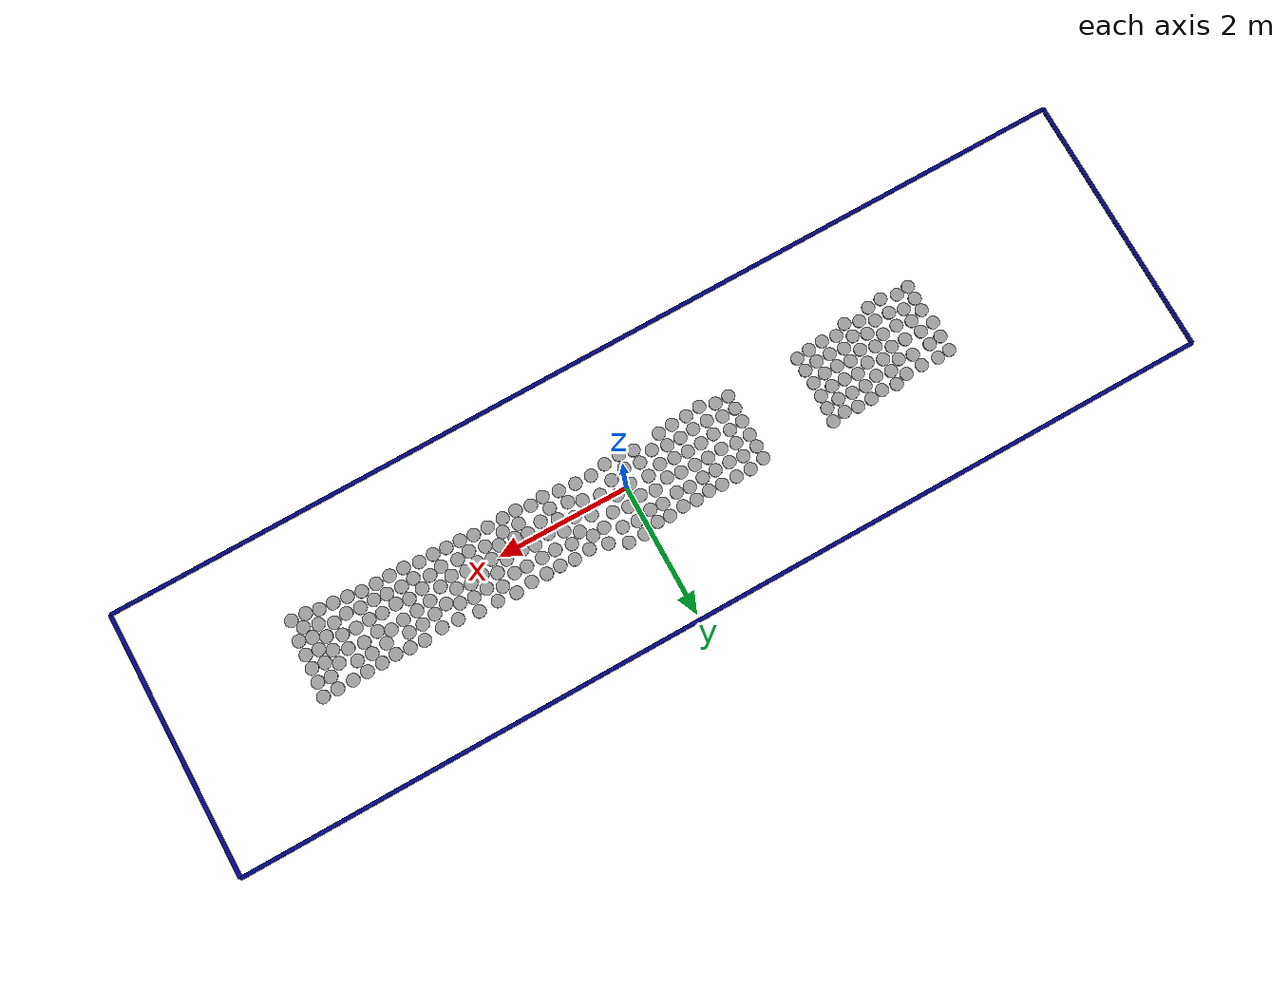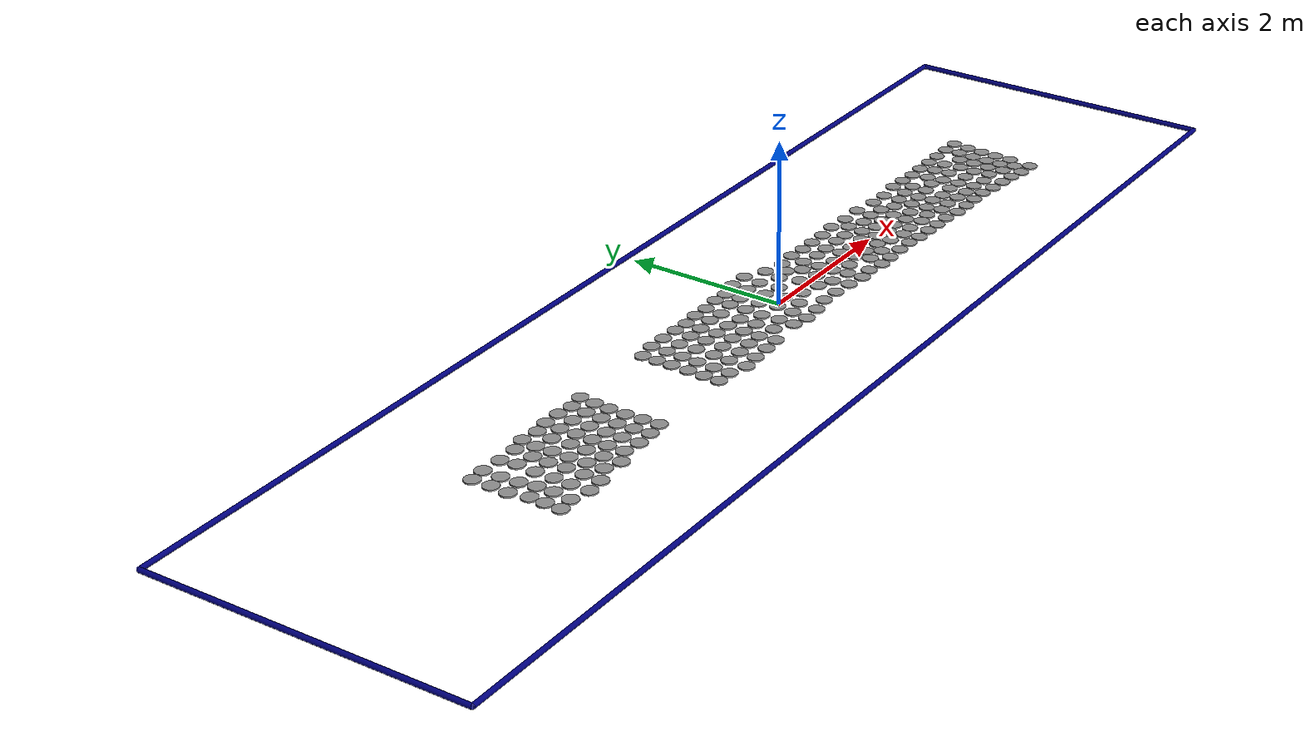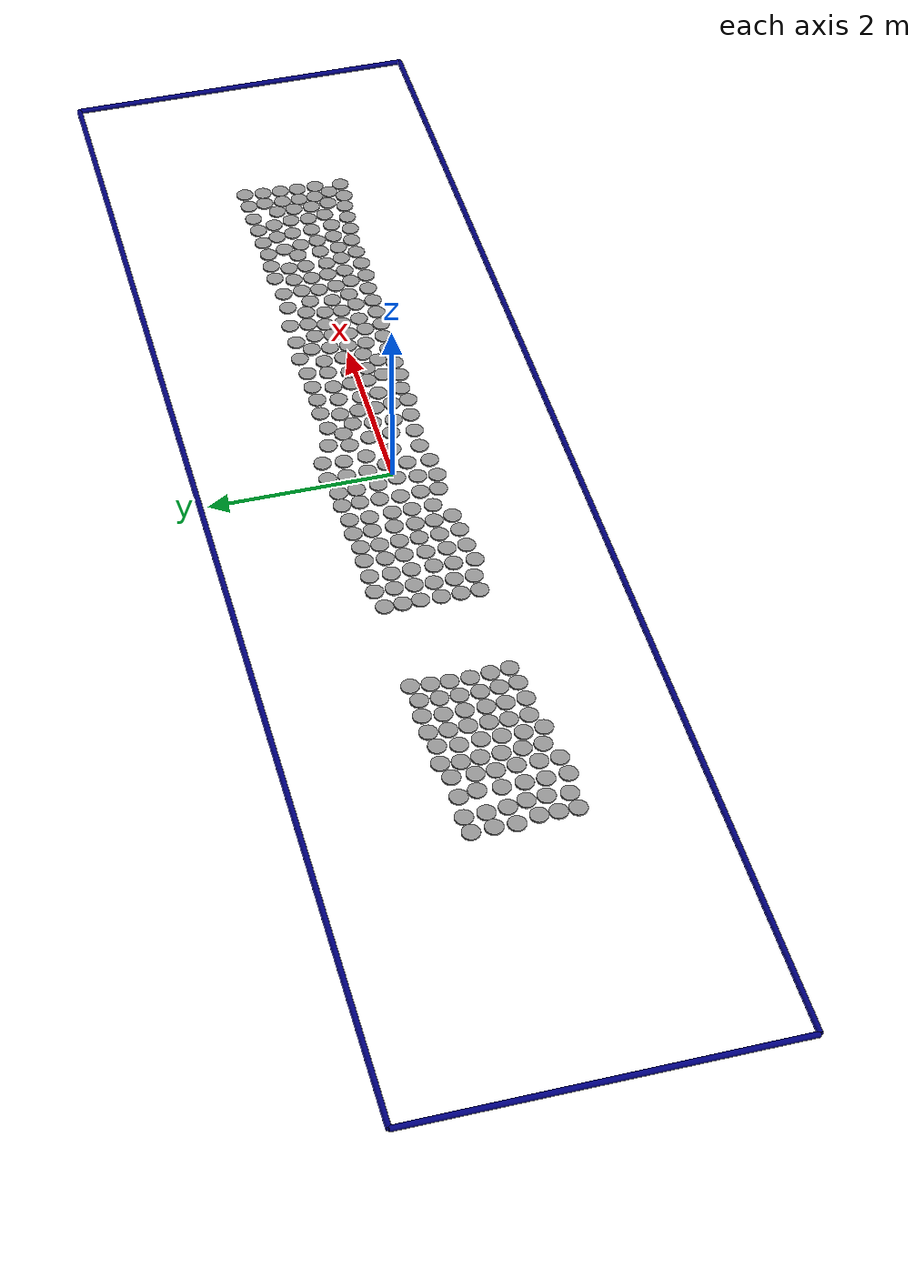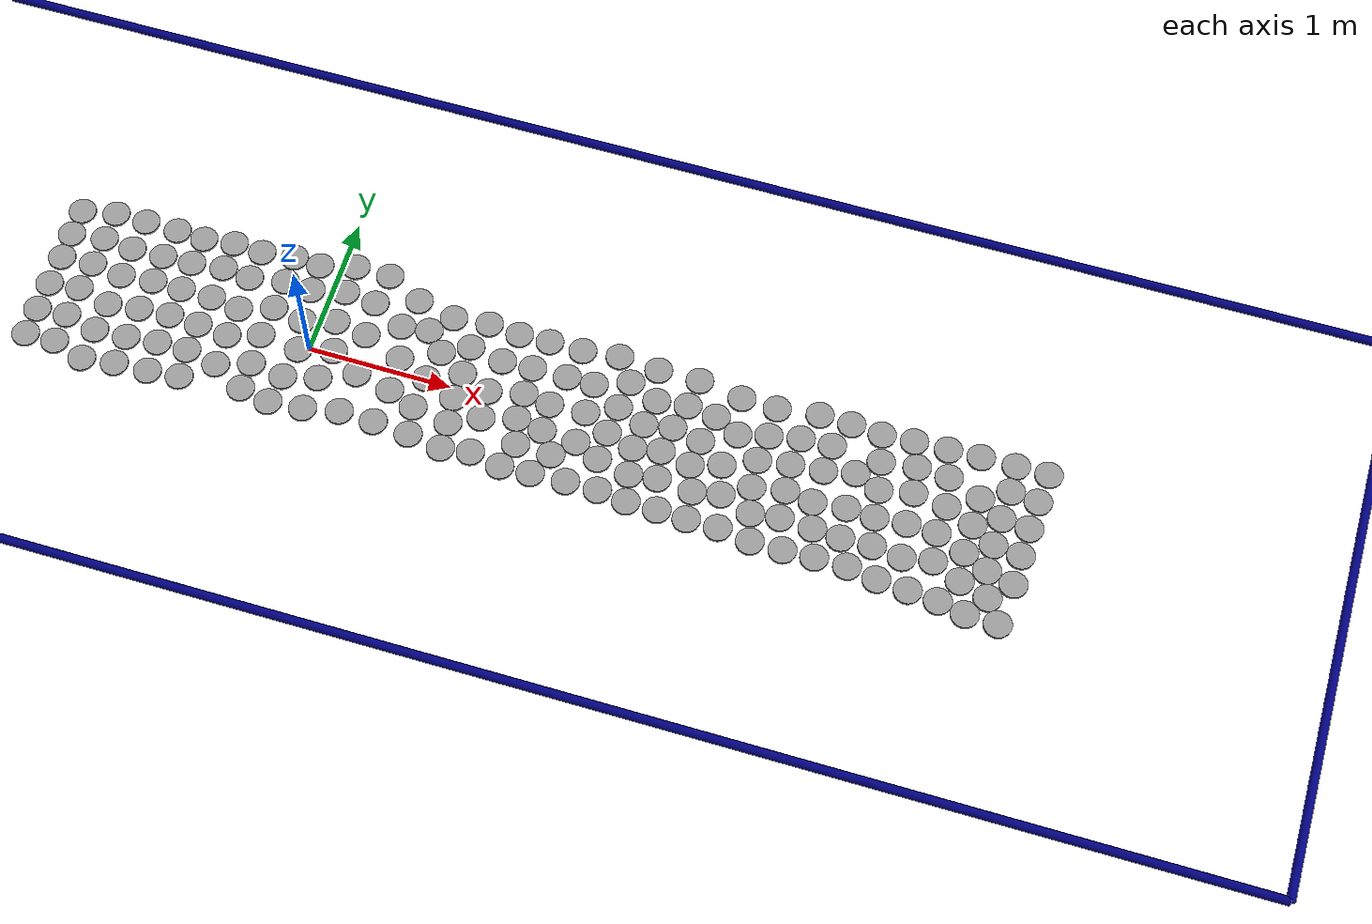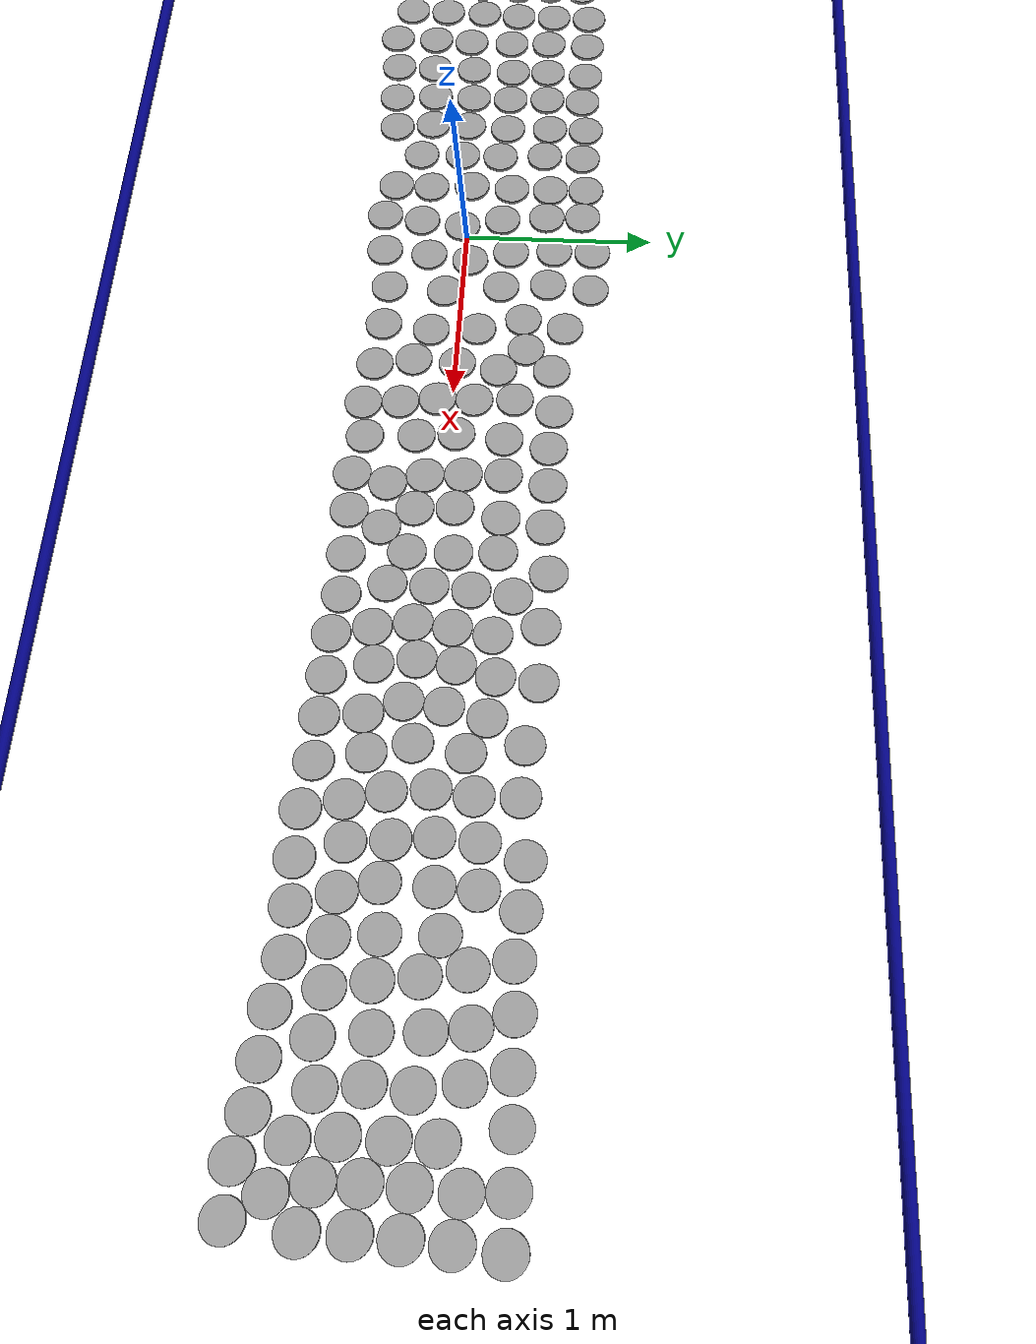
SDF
<sdf version="1.6">
 <world name="default">
  <light name="sun" type="directional">
   <pose>0 0 10 0 -0 0</pose>
   <diffuse>0.8 0.8 0.8 1</diffuse>
   <specular>0.1 0.1 0.1 1</specular>
   <attenuation>
    <range>1000</range>
    <constant>0.9</constant>
    <linear>0.01</linear>
    <quadratic>0.001</quadratic>
   </attenuation>
   <direction>-0.5 0.5 -1</direction>
  </light>
  <gravity>0 0 -9.8</gravity>
  <magnetic_field>6e-06 2.3e-05 -4.2e-05</magnetic_field>
  <atmosphere type="adiabatic"/>
  <physics name="default_physics" default="0" type="ode">
   <max_step_size>0.001</max_step_size>
   <real_time_factor>1</real_time_factor>
   <real_time_update_rate>1000</real_time_update_rate>
  </physics>
  <scene><ambient>0.4 0.4 0.4 1</ambient><background>0.7 0.7 0.7 1</background><shadows>1</shadows></scene>
  <spherical_coordinates>
   <surface_model>EARTH_WGS84</surface_model>
   <latitude_deg>0</latitude_deg>
   <longitude_deg>0</longitude_deg>
   <elevation>0</elevation>
   <heading_deg>0</heading_deg>
  </spherical_coordinates>
  <light name="user_point_light_0" type="point">
   <pose>-40.2877 36.9378 1 0 -0 0</pose>
   <diffuse>0.5 0.5 0.5 1</diffuse>
   <specular>0.1 0.1 0.1 1</specular>
   <attenuation>
    <range>20</range>
    <constant>0.5</constant>
    <linear>0.01</linear>
    <quadratic>0.001</quadratic>
   </attenuation>
   <cast_shadows>0</cast_shadows>
   <direction>0 0 -1</direction>
  </light>
  <light name="user_point_light_0_clone" type="point">
   <pose>-43.3445 16.5003 10 0 -0 0</pose>
   <diffuse>1 1 1 1</diffuse>
   <specular>1 1 1 1</specular>
   <direction>0 0 -1</direction>
   <attenuation>
    <range>100000</range>
    <constant>0.5</constant>
    <linear>0.01</linear>
    <quadratic>0.001</quadratic>
   </attenuation>
  </light>
  <light name="user_point_light_0_clone_0" type="point">
   <pose>-41.8744 -4.62896 10 0 -0 0</pose>
   <diffuse>1 1 1 1</diffuse>
   <specular>1 1 1 1</specular>
   <direction>0 0 -1</direction>
   <attenuation>
    <range>100000</range>
    <constant>0.5</constant>
    <linear>0.01</linear>
    <quadratic>0.001</quadratic>
   </attenuation>
  </light>
  <light name="user_point_light_0_clone_1" type="point">
   <pose>-45.3384 -27.6087 10 0 -0 0</pose>
   <diffuse>1 1 1 1</diffuse>
   <specular>1 1 1 1</specular>
   <direction>0 0 -1</direction>
   <attenuation>
    <range>100000</range>
    <constant>0.5</constant>
    <linear>0.01</linear>
    <quadratic>0.001</quadratic>
   </attenuation>
  </light>
  <light name="user_point_light_0_clone_2" type="point">
   <pose>-41.0308 -51.4934 10 0 -0 0</pose>
   <diffuse>1 1 1 1</diffuse>
   <specular>1 1 1 1</specular>
   <direction>0 0 -1</direction>
   <attenuation>
    <range>100000</range>
    <constant>0.5</constant>
    <linear>0.01</linear>
    <quadratic>0.001</quadratic>
   </attenuation>
  </light>
  <light name="user_point_light_0_clone_3" type="point">
   <pose>-13.091 -48.6057 10 0 -0 0</pose>
   <diffuse>1 1 1 1</diffuse>
   <specular>1 1 1 1</specular>
   <direction>0 0 -1</direction>
   <attenuation>
    <range>100000</range>
    <constant>0.5</constant>
    <linear>0.01</linear>
    <quadratic>0.001</quadratic>
   </attenuation>
  </light>
  <light name="user_point_light_0_clone_4" type="point">
   <pose>17.8273 -50.2126 10 0 -0 0</pose>
   <diffuse>1 1 1 1</diffuse>
   <specular>1 1 1 1</specular>
   <direction>0 0 -1</direction>
   <attenuation>
    <range>100000</range>
    <constant>0.5</constant>
    <linear>0.01</linear>
    <quadratic>0.001</quadratic>
   </attenuation>
  </light>
  <light name="user_point_light_0_clone_5" type="point">
   <pose>43.0105 -50.5018 10 0 -0 0</pose>
   <diffuse>1 1 1 1</diffuse>
   <specular>1 1 1 1</specular>
   <direction>0 0 -1</direction>
   <attenuation>
    <range>100000</range>
    <constant>0.5</constant>
    <linear>0.01</linear>
    <quadratic>0.001</quadratic>
   </attenuation>
  </light>
  <light name="user_point_light_0_clone_6" type="point">
   <pose>-30.8096 43.6215 10 0 -0 0</pose>
   <diffuse>1 1 1 1</diffuse>
   <specular>1 1 1 1</specular>
   <direction>0 0 -1</direction>
   <attenuation>
    <range>100000</range>
    <constant>0.5</constant>
    <linear>0.01</linear>
    <quadratic>0.001</quadratic>
   </attenuation>
  </light>
  <light name="user_point_light_0_clone_7" type="point">
   <pose>-6.06965 44.6895 10 0 -0 0</pose>
   <diffuse>1 1 1 1</diffuse>
   <specular>1 1 1 1</specular>
   <direction>0 0 -1</direction>
   <attenuation>
    <range>100000</range>
    <constant>0.5</constant>
    <linear>0.01</linear>
    <quadratic>0.001</quadratic>
   </attenuation>
  </light>
  <light name="user_point_light_0_clone_8" type="point">
   <pose>12.7263 46.5664 10 0 -0 0</pose>
   <diffuse>1 1 1 1</diffuse>
   <specular>1 1 1 1</specular>
   <direction>0 0 -1</direction>
   <attenuation>
    <range>100000</range>
    <constant>0.5</constant>
    <linear>0.01</linear>
    <quadratic>0.001</quadratic>
   </attenuation>
  </light>
  <light name="user_point_light_0_clone_9" type="point">
   <pose>31.1126 44.5953 10 0 -0 0</pose>
   <diffuse>1 1 1 1</diffuse>
   <specular>1 1 1 1</specular>
   <direction>0 0 -1</direction>
   <attenuation>
    <range>100000</range>
    <constant>0.5</constant>
    <linear>0.01</linear>
    <quadratic>0.001</quadratic>
   </attenuation>
  </light>
  <light name="user_point_light_0_clone_10" type="point">
   <pose>48.6896 31.6 10 0 -0 0</pose>
   <diffuse>1 1 1 1</diffuse>
   <specular>1 1 1 1</specular>
   <direction>0 0 -1</direction>
   <attenuation>
    <range>100000</range>
    <constant>0.5</constant>
    <linear>0.01</linear>
    <quadratic>0.001</quadratic>
   </attenuation>
  </light>
  <light name="user_point_light_0_clone_11" type="point">
   <pose>54.0783 8.97523 10 0 -0 0</pose>
   <diffuse>1 1 1 1</diffuse>
   <specular>1 1 1 1</specular>
   <direction>0 0 -1</direction>
   <attenuation>
    <range>100000</range>
    <constant>0.5</constant>
    <linear>0.01</linear>
    <quadratic>0.001</quadratic>
   </attenuation>
  </light>
  <light name="user_point_light_0_clone_12" type="point">
   <pose>59.1715 -20.1842 10 0 -0 0</pose>
   <diffuse>1 1 1 1</diffuse>
   <specular>1 1 1 1</specular>
   <direction>0 0 -1</direction>
   <attenuation>
    <range>100000</range>
    <constant>0.5</constant>
    <linear>0.01</linear>
    <quadratic>0.001</quadratic>
   </attenuation>
  </light>
  <light name="user_point_light_0_clone_13" type="point">
   <pose>56.6391 -41.8663 10 0 -0 0</pose>
   <diffuse>1 1 1 1</diffuse>
   <specular>1 1 1 1</specular>
   <direction>0 0 -1</direction>
   <attenuation>
    <range>100000</range>
    <constant>0.5</constant>
    <linear>0.01</linear>
    <quadratic>0.001</quadratic>
   </attenuation>
  </light>
  <model name="single-I">
   <static>0</static>
   <link name="left_side">
    <pose>0 0 0 0 1.5707 0</pose>
    <collision name="collision">
     <geometry><cylinder><radius>0.03</radius><length>15</length></cylinder></geometry>
    </collision>
    <visual name="lvisual">
     <geometry><cylinder><radius>0.03</radius><length>15</length></cylinder></geometry>
     <material>
      <ambient>0 0 0.5 1</ambient>
      <diffuse>0 0 0.5 1</diffuse>
      <specular>0 0 0.5 1</specular>
      <emissive>0 0 0.5 1</emissive>
     </material>
    </visual>
    <inertial>
     <inertia><ixx>1</ixx><ixy>0</ixy><ixz>0</ixz><iyy>1</iyy><iyz>0</iyz><izz>1</izz></inertia>
     <mass>1</mass>
    </inertial>
   </link>
   <link name="right_side">
    <pose>0 4 0 0 1.5707 0</pose>
    <collision name="rcollision">
     <geometry><cylinder><radius>0.03</radius><length>15</length></cylinder></geometry>
    </collision>
    <visual name="rvisual">
     <geometry><cylinder><radius>0.03</radius><length>15</length></cylinder></geometry>
     <material>
      <ambient>0 0 0.5 1</ambient>
      <diffuse>0 0 0.5 1</diffuse>
      <specular>0 0 0.5 1</specular>
      <emissive>0 0 0.5 1</emissive>
     </material>
    </visual>
    <inertial>
     <inertia><ixx>1</ixx><ixy>0</ixy><ixz>0</ixz><iyy>1</iyy><iyz>0</iyz><izz>1</izz></inertia>
     <mass>1</mass>
    </inertial>
   </link>
   <link name="garage_side">
    <pose>7.5 2 0 -0 1.5707 1.5707</pose>
    <collision name="gcollision">
     <geometry><cylinder><radius>0.03</radius><length>15</length></cylinder></geometry>
    </collision>
    <visual name="gvisual">
     <geometry><cylinder><radius>0.03</radius><length>4</length></cylinder></geometry>
     <material>
      <ambient>0 0 0.5 1</ambient>
      <diffuse>0 0 0.5 1</diffuse>
      <specular>0 0 0.5 1</specular>
      <emissive>0 0 0.5 1</emissive>
     </material>
    </visual>
    <inertial>
     <inertia><ixx>1</ixx><ixy>0</ixy><ixz>0</ixz><iyy>1</iyy><iyz>0</iyz><izz>1</izz></inertia>
     <mass>1</mass>
    </inertial>
   </link>
   <link name="manuevering_side">
    <pose>-7.5 2 0 -0 1.5707 1.5707</pose>
    <collision name="mcollision">
     <geometry><cylinder><radius>0.03</radius><length>15</length></cylinder></geometry>
    </collision>
    <visual name="mvisual">
     <geometry><cylinder><radius>0.03</radius><length>4</length></cylinder></geometry>
     <material>
      <ambient>0 0 0.5 1</ambient>
      <diffuse>0 0 0.5 1</diffuse>
      <specular>0 0 0.5 1</specular>
      <emissive>0 0 0.5 1</emissive>
     </material>
    </visual>
    <inertial>
     <inertia><ixx>1</ixx><ixy>0</ixy><ixz>0</ixz><iyy>1</iyy><iyz>0</iyz><izz>1</izz></inertia>
     <mass>1</mass>
    </inertial>
   </link>
   <joint name="gr" type="fixed"><child>right_side</child><parent>garage_side</parent></joint>
   <joint name="gl" type="fixed"><child>left_side</child><parent>garage_side</parent></joint>
   <joint name="mr" type="fixed"><child>right_side</child><parent>manuevering_side</parent></joint>
   <joint name="ml" type="fixed"><child>manuevering_side</child><parent>left_side</parent></joint>
   <pose>-0.465032 -1.9092 0.030503 -0.000121 6.3e-05 0.005487</pose>
  </model>
  <model name="unit_cylinder_clone">
   <pose>-4.92824 0.244346 0.008114 0 0 -0.669076</pose>
   <link name="link">
    <inertial>
     <mass>1</mass>
     <inertia><ixx>0.145833</ixx><ixy>0</ixy><ixz>0</ixz><iyy>0.145833</iyy><iyz>0</iyz><izz>0.125</izz></inertia>
    </inertial>
    <collision name="collision">
     <geometry><cylinder><radius>0.0950718</radius><length>0.0162339</length></cylinder></geometry>
    </collision>
    <visual name="visual">
     <geometry><cylinder><radius>0.0950718</radius><length>0.0162339</length></cylinder></geometry>
     <material>
      <script><name>Gazebo/Grey</name><uri>file://media/materials/scripts/gazebo.material</uri></script>
     </material>
    </visual>
   </link>
  </model>
  <model name="unit_cylinder_clone_clone">
   <pose>-4.94005 0.019823 0.008108 0 -0 0.098454</pose>
   <link name="link">
    <inertial>
     <mass>1</mass>
     <inertia><ixx>0.145833</ixx><ixy>0</ixy><ixz>0</ixz><iyy>0.145833</iyy><iyz>0</iyz><izz>0.125</izz></inertia>
    </inertial>
    <collision name="collision">
     <geometry><cylinder><radius>0.0950718</radius><length>0.0162339</length></cylinder></geometry>
    </collision>
    <visual name="visual">
     <geometry><cylinder><radius>0.0950718</radius><length>0.0162339</length></cylinder></geometry>
     <material>
      <script><name>Gazebo/Grey</name><uri>file://media/materials/scripts/gazebo.material</uri></script>
     </material>
    </visual>
   </link>
  </model>
  <model name="unit_cylinder_clone_clone_1">
   <pose>-4.88991 -0.213171 0.008116 0 -0 0.00121</pose>
   <link name="link">
    <inertial>
     <mass>1</mass>
     <inertia><ixx>0.145833</ixx><ixy>0</ixy><ixz>0</ixz><iyy>0.145833</iyy><iyz>0</iyz><izz>0.125</izz></inertia>
    </inertial>
    <collision name="collision">
     <geometry><cylinder><radius>0.0950718</radius><length>0.0162339</length></cylinder></geometry>
    </collision>
    <visual name="visual">
     <geometry><cylinder><radius>0.0950718</radius><length>0.0162339</length></cylinder></geometry>
     <material>
      <script><name>Gazebo/Grey</name><uri>file://media/materials/scripts/gazebo.material</uri></script>
     </material>
    </visual>
   </link>
  </model>
  <model name="unit_cylinder_clone_clone_2">
   <pose>-4.89151 -0.407672 0.008113 5e-06 -0 0</pose>
   <link name="link">
    <inertial>
     <mass>1</mass>
     <inertia><ixx>0.145833</ixx><ixy>0</ixy><ixz>0</ixz><iyy>0.145833</iyy><iyz>0</iyz><izz>0.125</izz></inertia>
    </inertial>
    <collision name="collision">
     <geometry><cylinder><radius>0.0950718</radius><length>0.0162339</length></cylinder></geometry>
    </collision>
    <visual name="visual">
     <geometry><cylinder><radius>0.0950718</radius><length>0.0162339</length></cylinder></geometry>
     <material>
      <script><name>Gazebo/Grey</name><uri>file://media/materials/scripts/gazebo.material</uri></script>
     </material>
    </visual>
   </link>
  </model>
  <model name="unit_cylinder_clone_clone_3">
   <pose>-4.89624 -0.604172 0.008113 5e-06 -0 0</pose>
   <link name="link">
    <inertial>
     <mass>1</mass>
     <inertia><ixx>0.145833</ixx><ixy>0</ixy><ixz>0</ixz><iyy>0.145833</iyy><iyz>0</iyz><izz>0.125</izz></inertia>
    </inertial>
    <collision name="collision">
     <geometry><cylinder><radius>0.0950718</radius><length>0.0162339</length></cylinder></geometry>
    </collision>
    <visual name="visual">
     <geometry><cylinder><radius>0.0950718</radius><length>0.0162339</length></cylinder></geometry>
     <material>
      <script><name>Gazebo/Grey</name><uri>file://media/materials/scripts/gazebo.material</uri></script>
     </material>
    </visual>
   </link>
  </model>
  <model name="unit_cylinder_clone_clone_4">
   <pose>-4.74309 0.493456 0.008111 -0 6e-06 -1.60408</pose>
   <link name="link">
    <inertial>
     <mass>1</mass>
     <inertia><ixx>0.145833</ixx><ixy>0</ixy><ixz>0</ixz><iyy>0.145833</iyy><iyz>0</iyz><izz>0.125</izz></inertia>
    </inertial>
    <collision name="collision">
     <geometry><cylinder><radius>0.0950718</radius><length>0.0162339</length></cylinder></geometry>
    </collision>
    <visual name="visual">
     <geometry><cylinder><radius>0.0950718</radius><length>0.0162339</length></cylinder></geometry>
     <material>
      <script><name>Gazebo/Grey</name><uri>file://media/materials/scripts/gazebo.material</uri></script>
     </material>
    </visual>
   </link>
  </model>
  <model name="unit_cylinder_clone_clone_5">
   <pose>-4.93657 0.475133 0.008114 0 0 -0.035931</pose>
   <link name="link">
    <inertial>
     <mass>1</mass>
     <inertia><ixx>0.145833</ixx><ixy>0</ixy><ixz>0</ixz><iyy>0.145833</iyy><iyz>0</iyz><izz>0.125</izz></inertia>
    </inertial>
    <collision name="collision">
     <geometry><cylinder><radius>0.0950718</radius><length>0.0162339</length></cylinder></geometry>
    </collision>
    <visual name="visual">
     <geometry><cylinder><radius>0.0950718</radius><length>0.0162339</length></cylinder></geometry>
     <material>
      <script><name>Gazebo/Grey</name><uri>file://media/materials/scripts/gazebo.material</uri></script>
     </material>
    </visual>
   </link>
  </model>
  <model name="unit_cylinder_clone_clone_7">
   <pose>-4.72333 0.050462 0.008117 0 -0 0.000482</pose>
   <link name="link">
    <inertial>
     <mass>1</mass>
     <inertia><ixx>0.145833</ixx><ixy>0</ixy><ixz>0</ixz><iyy>0.145833</iyy><iyz>0</iyz><izz>0.125</izz></inertia>
    </inertial>
    <collision name="collision">
     <geometry><cylinder><radius>0.0950718</radius><length>0.0162339</length></cylinder></geometry>
    </collision>
    <visual name="visual">
     <geometry><cylinder><radius>0.0950718</radius><length>0.0162339</length></cylinder></geometry>
     <material>
      <script><name>Gazebo/Grey</name><uri>file://media/materials/scripts/gazebo.material</uri></script>
     </material>
    </visual>
   </link>
  </model>
  <model name="unit_cylinder_clone_clone_8">
   <pose>-4.68614 -0.145367 0.008108 0 -0 0.000518</pose>
   <link name="link">
    <inertial>
     <mass>1</mass>
     <inertia><ixx>0.145833</ixx><ixy>0</ixy><ixz>0</ixz><iyy>0.145833</iyy><iyz>0</iyz><izz>0.125</izz></inertia>
    </inertial>
    <collision name="collision">
     <geometry><cylinder><radius>0.0950718</radius><length>0.0162339</length></cylinder></geometry>
    </collision>
    <visual name="visual">
     <geometry><cylinder><radius>0.0950718</radius><length>0.0162339</length></cylinder></geometry>
     <material>
      <script><name>Gazebo/Grey</name><uri>file://media/materials/scripts/gazebo.material</uri></script>
     </material>
    </visual>
   </link>
  </model>
  <model name="unit_cylinder_clone_clone_9">
   <pose>-4.67778 -0.349152 0.008111 0 -0 0</pose>
   <link name="link">
    <inertial>
     <mass>1</mass>
     <inertia><ixx>0.145833</ixx><ixy>0</ixy><ixz>0</ixz><iyy>0.145833</iyy><iyz>0</iyz><izz>0.125</izz></inertia>
    </inertial>
    <collision name="collision">
     <geometry><cylinder><radius>0.0950718</radius><length>0.0162339</length></cylinder></geometry>
    </collision>
    <visual name="visual">
     <geometry><cylinder><radius>0.0950718</radius><length>0.0162339</length></cylinder></geometry>
     <material>
      <script><name>Gazebo/Grey</name><uri>file://media/materials/scripts/gazebo.material</uri></script>
     </material>
    </visual>
   </link>
  </model>
  <model name="unit_cylinder_clone_clone_10">
   <pose>-4.70032 -0.577507 0.008108 0 -0 0</pose>
   <link name="link">
    <inertial>
     <mass>1</mass>
     <inertia><ixx>0.145833</ixx><ixy>0</ixy><ixz>0</ixz><iyy>0.145833</iyy><iyz>0</iyz><izz>0.125</izz></inertia>
    </inertial>
    <collision name="collision">
     <geometry><cylinder><radius>0.0950718</radius><length>0.0162339</length></cylinder></geometry>
    </collision>
    <visual name="visual">
     <geometry><cylinder><radius>0.0950718</radius><length>0.0162339</length></cylinder></geometry>
     <material>
      <script><name>Gazebo/Grey</name><uri>file://media/materials/scripts/gazebo.material</uri></script>
     </material>
    </visual>
   </link>
  </model>
  <model name="unit_cylinder_clone_clone_11">
   <pose>-4.73967 0.268855 0.008112 0 0 -0.462715</pose>
   <link name="link">
    <inertial>
     <mass>1</mass>
     <inertia><ixx>0.145833</ixx><ixy>0</ixy><ixz>0</ixz><iyy>0.145833</iyy><iyz>0</iyz><izz>0.125</izz></inertia>
    </inertial>
    <collision name="collision">
     <geometry><cylinder><radius>0.0950718</radius><length>0.0162339</length></cylinder></geometry>
    </collision>
    <visual name="visual">
     <geometry><cylinder><radius>0.0950718</radius><length>0.0162339</length></cylinder></geometry>
     <material>
      <script><name>Gazebo/Grey</name><uri>file://media/materials/scripts/gazebo.material</uri></script>
     </material>
    </visual>
   </link>
  </model>
  <model name="unit_cylinder_clone_clone_12">
   <pose>-4.48597 0.47576 0.008484 -0.001635 0.003501 -0.231539</pose>
   <link name="link">
    <inertial>
     <mass>1</mass>
     <inertia><ixx>0.145833</ixx><ixy>0</ixy><ixz>0</ixz><iyy>0.145833</iyy><iyz>0</iyz><izz>0.125</izz></inertia>
    </inertial>
    <collision name="collision">
     <geometry><cylinder><radius>0.0950718</radius><length>0.0162339</length></cylinder></geometry>
    </collision>
    <visual name="visual">
     <geometry><cylinder><radius>0.0950718</radius><length>0.0162339</length></cylinder></geometry>
     <material>
      <script><name>Gazebo/Grey</name><uri>file://media/materials/scripts/gazebo.material</uri></script>
     </material>
    </visual>
   </link>
  </model>
  <model name="unit_cylinder_clone_clone_13">
   <pose>-4.45178 0.283309 0.008113 0 0 -0.013302</pose>
   <link name="link">
    <inertial>
     <mass>1</mass>
     <inertia><ixx>0.145833</ixx><ixy>0</ixy><ixz>0</ixz><iyy>0.145833</iyy><iyz>0</iyz><izz>0.125</izz></inertia>
    </inertial>
    <collision name="collision">
     <geometry><cylinder><radius>0.0950718</radius><length>0.0162339</length></cylinder></geometry>
    </collision>
    <visual name="visual">
     <geometry><cylinder><radius>0.0950718</radius><length>0.0162339</length></cylinder></geometry>
     <material>
      <script><name>Gazebo/Grey</name><uri>file://media/materials/scripts/gazebo.material</uri></script>
     </material>
    </visual>
   </link>
  </model>
  <model name="unit_cylinder_clone_clone_14">
   <pose>-4.46934 0.039984 0.008108 0 -0 0</pose>
   <link name="link">
    <inertial>
     <mass>1</mass>
     <inertia><ixx>0.145833</ixx><ixy>0</ixy><ixz>0</ixz><iyy>0.145833</iyy><iyz>0</iyz><izz>0.125</izz></inertia>
    </inertial>
    <collision name="collision">
     <geometry><cylinder><radius>0.0950718</radius><length>0.0162339</length></cylinder></geometry>
    </collision>
    <visual name="visual">
     <geometry><cylinder><radius>0.0950718</radius><length>0.0162339</length></cylinder></geometry>
     <material>
      <script><name>Gazebo/Grey</name><uri>file://media/materials/scripts/gazebo.material</uri></script>
     </material>
    </visual>
   </link>
  </model>
  <model name="unit_cylinder_clone_clone_15">
   <pose>-4.46416 -0.191836 0.008113 0 -0 0</pose>
   <link name="link">
    <inertial>
     <mass>1</mass>
     <inertia><ixx>0.145833</ixx><ixy>0</ixy><ixz>0</ixz><iyy>0.145833</iyy><iyz>0</iyz><izz>0.125</izz></inertia>
    </inertial>
    <collision name="collision">
     <geometry><cylinder><radius>0.0950718</radius><length>0.0162339</length></cylinder></geometry>
    </collision>
    <visual name="visual">
     <geometry><cylinder><radius>0.0950718</radius><length>0.0162339</length></cylinder></geometry>
     <material>
      <script><name>Gazebo/Grey</name><uri>file://media/materials/scripts/gazebo.material</uri></script>
     </material>
    </visual>
   </link>
  </model>
  <model name="unit_cylinder_clone_clone_16">
   <pose>-4.46665 -0.405888 0.008117 0 -0 0</pose>
   <link name="link">
    <inertial>
     <mass>1</mass>
     <inertia><ixx>0.145833</ixx><ixy>0</ixy><ixz>0</ixz><iyy>0.145833</iyy><iyz>0</iyz><izz>0.125</izz></inertia>
    </inertial>
    <collision name="collision">
     <geometry><cylinder><radius>0.0950718</radius><length>0.0162339</length></cylinder></geometry>
    </collision>
    <visual name="visual">
     <geometry><cylinder><radius>0.0950718</radius><length>0.0162339</length></cylinder></geometry>
     <material>
      <script><name>Gazebo/Grey</name><uri>file://media/materials/scripts/gazebo.material</uri></script>
     </material>
    </visual>
   </link>
  </model>
  <model name="unit_cylinder_clone_clone_17">
   <pose>-4.46064 -0.635367 0.008111 0 -0 0</pose>
   <link name="link">
    <inertial>
     <mass>1</mass>
     <inertia><ixx>0.145833</ixx><ixy>0</ixy><ixz>0</ixz><iyy>0.145833</iyy><iyz>0</iyz><izz>0.125</izz></inertia>
    </inertial>
    <collision name="collision">
     <geometry><cylinder><radius>0.0950718</radius><length>0.0162339</length></cylinder></geometry>
    </collision>
    <visual name="visual">
     <geometry><cylinder><radius>0.0950718</radius><length>0.0162339</length></cylinder></geometry>
     <material>
      <script><name>Gazebo/Grey</name><uri>file://media/materials/scripts/gazebo.material</uri></script>
     </material>
    </visual>
   </link>
  </model>
  <model name="unit_cylinder_clone_clone_18">
   <pose>-4.24417 -0.611687 0.008108 0 -0 0</pose>
   <link name="link">
    <inertial>
     <mass>1</mass>
     <inertia><ixx>0.145833</ixx><ixy>0</ixy><ixz>0</ixz><iyy>0.145833</iyy><iyz>0</iyz><izz>0.125</izz></inertia>
    </inertial>
    <collision name="collision">
     <geometry><cylinder><radius>0.0950718</radius><length>0.0162339</length></cylinder></geometry>
    </collision>
    <visual name="visual">
     <geometry><cylinder><radius>0.0950718</radius><length>0.0162339</length></cylinder></geometry>
     <material>
      <script><name>Gazebo/Grey</name><uri>file://media/materials/scripts/gazebo.material</uri></script>
     </material>
    </visual>
   </link>
  </model>
  <model name="unit_cylinder_clone_clone_19">
   <pose>-4.23882 -0.40217 0.008108 0 -0 0</pose>
   <link name="link">
    <inertial>
     <mass>1</mass>
     <inertia><ixx>0.145833</ixx><ixy>0</ixy><ixz>0</ixz><iyy>0.145833</iyy><iyz>0</iyz><izz>0.125</izz></inertia>
    </inertial>
    <collision name="collision">
     <geometry><cylinder><radius>0.0950718</radius><length>0.0162339</length></cylinder></geometry>
    </collision>
    <visual name="visual">
     <geometry><cylinder><radius>0.0950718</radius><length>0.0162339</length></cylinder></geometry>
     <material>
      <script><name>Gazebo/Grey</name><uri>file://media/materials/scripts/gazebo.material</uri></script>
     </material>
    </visual>
   </link>
  </model>
  <model name="unit_cylinder_clone_clone_20">
   <pose>-4.23553 -0.175422 0.008113 5e-06 -0 0</pose>
   <link name="link">
    <inertial>
     <mass>1</mass>
     <inertia><ixx>0.145833</ixx><ixy>0</ixy><ixz>0</ixz><iyy>0.145833</iyy><iyz>0</iyz><izz>0.125</izz></inertia>
    </inertial>
    <collision name="collision">
     <geometry><cylinder><radius>0.0950718</radius><length>0.0162339</length></cylinder></geometry>
    </collision>
    <visual name="visual">
     <geometry><cylinder><radius>0.0950718</radius><length>0.0162339</length></cylinder></geometry>
     <material>
      <script><name>Gazebo/Grey</name><uri>file://media/materials/scripts/gazebo.material</uri></script>
     </material>
    </visual>
   </link>
  </model>
  <model name="unit_cylinder_clone_clone_21">
   <pose>-4.25035 0.039573 0.008108 0 -0 0</pose>
   <link name="link">
    <inertial>
     <mass>1</mass>
     <inertia><ixx>0.145833</ixx><ixy>0</ixy><ixz>0</ixz><iyy>0.145833</iyy><iyz>0</iyz><izz>0.125</izz></inertia>
    </inertial>
    <collision name="collision">
     <geometry><cylinder><radius>0.0950718</radius><length>0.0162339</length></cylinder></geometry>
    </collision>
    <visual name="visual">
     <geometry><cylinder><radius>0.0950718</radius><length>0.0162339</length></cylinder></geometry>
     <material>
      <script><name>Gazebo/Grey</name><uri>file://media/materials/scripts/gazebo.material</uri></script>
     </material>
    </visual>
   </link>
  </model>
  <model name="unit_cylinder_clone_clone_22">
   <pose>-4.24467 0.2429 0.008108 0 -0 0.001298</pose>
   <link name="link">
    <inertial>
     <mass>1</mass>
     <inertia><ixx>0.145833</ixx><ixy>0</ixy><ixz>0</ixz><iyy>0.145833</iyy><iyz>0</iyz><izz>0.125</izz></inertia>
    </inertial>
    <collision name="collision">
     <geometry><cylinder><radius>0.0950718</radius><length>0.0162339</length></cylinder></geometry>
    </collision>
    <visual name="visual">
     <geometry><cylinder><radius>0.0950718</radius><length>0.0162339</length></cylinder></geometry>
     <material>
      <script><name>Gazebo/Grey</name><uri>file://media/materials/scripts/gazebo.material</uri></script>
     </material>
    </visual>
   </link>
  </model>
  <model name="unit_cylinder_clone_clone_23">
   <pose>-4.2309 0.480876 0.008107 0 0 -0.001963</pose>
   <link name="link">
    <inertial>
     <mass>1</mass>
     <inertia><ixx>0.145833</ixx><ixy>0</ixy><ixz>0</ixz><iyy>0.145833</iyy><iyz>0</iyz><izz>0.125</izz></inertia>
    </inertial>
    <collision name="collision">
     <geometry><cylinder><radius>0.0950718</radius><length>0.0162339</length></cylinder></geometry>
    </collision>
    <visual name="visual">
     <geometry><cylinder><radius>0.0950718</radius><length>0.0162339</length></cylinder></geometry>
     <material>
      <script><name>Gazebo/Grey</name><uri>file://media/materials/scripts/gazebo.material</uri></script>
     </material>
    </visual>
   </link>
  </model>
  <model name="unit_cylinder_clone_clone_24">
   <pose>-4.03583 0.541954 0.008108 0 -0 0</pose>
   <link name="link">
    <inertial>
     <mass>1</mass>
     <inertia><ixx>0.145833</ixx><ixy>0</ixy><ixz>0</ixz><iyy>0.145833</iyy><iyz>0</iyz><izz>0.125</izz></inertia>
    </inertial>
    <collision name="collision">
     <geometry><cylinder><radius>0.0950718</radius><length>0.0162339</length></cylinder></geometry>
    </collision>
    <visual name="visual">
     <geometry><cylinder><radius>0.0950718</radius><length>0.0162339</length></cylinder></geometry>
     <material>
      <script><name>Gazebo/Grey</name><uri>file://media/materials/scripts/gazebo.material</uri></script>
     </material>
    </visual>
   </link>
  </model>
  <model name="unit_cylinder_clone_clone_25">
   <pose>-4.06381 0.341531 0.008113 5e-06 -0 0</pose>
   <link name="link">
    <inertial>
     <mass>1</mass>
     <inertia><ixx>0.145833</ixx><ixy>0</ixy><ixz>0</ixz><iyy>0.145833</iyy><iyz>0</iyz><izz>0.125</izz></inertia>
    </inertial>
    <collision name="collision">
     <geometry><cylinder><radius>0.0950718</radius><length>0.0162339</length></cylinder></geometry>
    </collision>
    <visual name="visual">
     <geometry><cylinder><radius>0.0950718</radius><length>0.0162339</length></cylinder></geometry>
     <material>
      <script><name>Gazebo/Grey</name><uri>file://media/materials/scripts/gazebo.material</uri></script>
     </material>
    </visual>
   </link>
  </model>
  <model name="unit_cylinder_clone_clone_26">
   <pose>-4.05114 0.140238 0.008108 0 -0 0</pose>
   <link name="link">
    <inertial>
     <mass>1</mass>
     <inertia><ixx>0.145833</ixx><ixy>0</ixy><ixz>0</ixz><iyy>0.145833</iyy><iyz>0</iyz><izz>0.125</izz></inertia>
    </inertial>
    <collision name="collision">
     <geometry><cylinder><radius>0.0950718</radius><length>0.0162339</length></cylinder></geometry>
    </collision>
    <visual name="visual">
     <geometry><cylinder><radius>0.0950718</radius><length>0.0162339</length></cylinder></geometry>
     <material>
      <script><name>Gazebo/Grey</name><uri>file://media/materials/scripts/gazebo.material</uri></script>
     </material>
    </visual>
   </link>
  </model>
  <model name="unit_cylinder_clone_clone_27">
   <pose>-4.05025 -0.072851 0.008108 0 -0 0</pose>
   <link name="link">
    <inertial>
     <mass>1</mass>
     <inertia><ixx>0.145833</ixx><ixy>0</ixy><ixz>0</ixz><iyy>0.145833</iyy><iyz>0</iyz><izz>0.125</izz></inertia>
    </inertial>
    <collision name="collision">
     <geometry><cylinder><radius>0.0950718</radius><length>0.0162339</length></cylinder></geometry>
    </collision>
    <visual name="visual">
     <geometry><cylinder><radius>0.0950718</radius><length>0.0162339</length></cylinder></geometry>
     <material>
      <script><name>Gazebo/Grey</name><uri>file://media/materials/scripts/gazebo.material</uri></script>
     </material>
    </visual>
   </link>
  </model>
  <model name="unit_cylinder_clone_clone_28">
   <pose>-4.04202 -0.290432 0.008113 5e-06 -0 0</pose>
   <link name="link">
    <inertial>
     <mass>1</mass>
     <inertia><ixx>0.145833</ixx><ixy>0</ixy><ixz>0</ixz><iyy>0.145833</iyy><iyz>0</iyz><izz>0.125</izz></inertia>
    </inertial>
    <collision name="collision">
     <geometry><cylinder><radius>0.0950718</radius><length>0.0162339</length></cylinder></geometry>
    </collision>
    <visual name="visual">
     <geometry><cylinder><radius>0.0950718</radius><length>0.0162339</length></cylinder></geometry>
     <material>
      <script><name>Gazebo/Grey</name><uri>file://media/materials/scripts/gazebo.material</uri></script>
     </material>
    </visual>
   </link>
  </model>
  <model name="unit_cylinder_clone_clone_29">
   <pose>-4.03468 -0.501989 0.008108 0 -0 0</pose>
   <link name="link">
    <inertial>
     <mass>1</mass>
     <inertia><ixx>0.145833</ixx><ixy>0</ixy><ixz>0</ixz><iyy>0.145833</iyy><iyz>0</iyz><izz>0.125</izz></inertia>
    </inertial>
    <collision name="collision">
     <geometry><cylinder><radius>0.0950718</radius><length>0.0162339</length></cylinder></geometry>
    </collision>
    <visual name="visual">
     <geometry><cylinder><radius>0.0950718</radius><length>0.0162339</length></cylinder></geometry>
     <material>
      <script><name>Gazebo/Grey</name><uri>file://media/materials/scripts/gazebo.material</uri></script>
     </material>
    </visual>
   </link>
  </model>
  <model name="unit_cylinder_clone_clone_30">
   <pose>-3.83027 -0.570426 0.008113 5e-06 -0 0</pose>
   <link name="link">
    <inertial>
     <mass>1</mass>
     <inertia><ixx>0.145833</ixx><ixy>0</ixy><ixz>0</ixz><iyy>0.145833</iyy><iyz>0</iyz><izz>0.125</izz></inertia>
    </inertial>
    <collision name="collision">
     <geometry><cylinder><radius>0.0950718</radius><length>0.0162339</length></cylinder></geometry>
    </collision>
    <visual name="visual">
     <geometry><cylinder><radius>0.0950718</radius><length>0.0162339</length></cylinder></geometry>
     <material>
      <script><name>Gazebo/Grey</name><uri>file://media/materials/scripts/gazebo.material</uri></script>
     </material>
    </visual>
   </link>
  </model>
  <model name="unit_cylinder_clone_clone_31">
   <pose>-3.84434 -0.357022 0.008113 5e-06 -0 0</pose>
   <link name="link">
    <inertial>
     <mass>1</mass>
     <inertia><ixx>0.145833</ixx><ixy>0</ixy><ixz>0</ixz><iyy>0.145833</iyy><iyz>0</iyz><izz>0.125</izz></inertia>
    </inertial>
    <collision name="collision">
     <geometry><cylinder><radius>0.0950718</radius><length>0.0162339</length></cylinder></geometry>
    </collision>
    <visual name="visual">
     <geometry><cylinder><radius>0.0950718</radius><length>0.0162339</length></cylinder></geometry>
     <material>
      <script><name>Gazebo/Grey</name><uri>file://media/materials/scripts/gazebo.material</uri></script>
     </material>
    </visual>
   </link>
  </model>
  <model name="unit_cylinder_clone_clone_32">
   <pose>-3.83894 -0.136252 0.008108 0 -0 0</pose>
   <link name="link">
    <inertial>
     <mass>1</mass>
     <inertia><ixx>0.145833</ixx><ixy>0</ixy><ixz>0</ixz><iyy>0.145833</iyy><iyz>0</iyz><izz>0.125</izz></inertia>
    </inertial>
    <collision name="collision">
     <geometry><cylinder><radius>0.0950718</radius><length>0.0162339</length></cylinder></geometry>
    </collision>
    <visual name="visual">
     <geometry><cylinder><radius>0.0950718</radius><length>0.0162339</length></cylinder></geometry>
     <material>
      <script><name>Gazebo/Grey</name><uri>file://media/materials/scripts/gazebo.material</uri></script>
     </material>
    </visual>
   </link>
  </model>
  <model name="unit_cylinder_clone_clone_33">
   <pose>-3.83188 0.07411 0.008113 5e-06 -0 0</pose>
   <link name="link">
    <inertial>
     <mass>1</mass>
     <inertia><ixx>0.145833</ixx><ixy>0</ixy><ixz>0</ixz><iyy>0.145833</iyy><iyz>0</iyz><izz>0.125</izz></inertia>
    </inertial>
    <collision name="collision">
     <geometry><cylinder><radius>0.0950718</radius><length>0.0162339</length></cylinder></geometry>
    </collision>
    <visual name="visual">
     <geometry><cylinder><radius>0.0950718</radius><length>0.0162339</length></cylinder></geometry>
     <material>
      <script><name>Gazebo/Grey</name><uri>file://media/materials/scripts/gazebo.material</uri></script>
     </material>
    </visual>
   </link>
  </model>
  <model name="unit_cylinder_clone_clone_34">
   <pose>-3.84755 0.300225 0.008108 0 -0 0</pose>
   <link name="link">
    <inertial>
     <mass>1</mass>
     <inertia><ixx>0.145833</ixx><ixy>0</ixy><ixz>0</ixz><iyy>0.145833</iyy><iyz>0</iyz><izz>0.125</izz></inertia>
    </inertial>
    <collision name="collision">
     <geometry><cylinder><radius>0.0950718</radius><length>0.0162339</length></cylinder></geometry>
    </collision>
    <visual name="visual">
     <geometry><cylinder><radius>0.0950718</radius><length>0.0162339</length></cylinder></geometry>
     <material>
      <script><name>Gazebo/Grey</name><uri>file://media/materials/scripts/gazebo.material</uri></script>
     </material>
    </visual>
   </link>
  </model>
  <model name="unit_cylinder_clone_clone_35">
   <pose>-3.81316 0.514902 0.008108 0 -0 0</pose>
   <link name="link">
    <inertial>
     <mass>1</mass>
     <inertia><ixx>0.145833</ixx><ixy>0</ixy><ixz>0</ixz><iyy>0.145833</iyy><iyz>0</iyz><izz>0.125</izz></inertia>
    </inertial>
    <collision name="collision">
     <geometry><cylinder><radius>0.0950718</radius><length>0.0162339</length></cylinder></geometry>
    </collision>
    <visual name="visual">
     <geometry><cylinder><radius>0.0950718</radius><length>0.0162339</length></cylinder></geometry>
     <material>
      <script><name>Gazebo/Grey</name><uri>file://media/materials/scripts/gazebo.material</uri></script>
     </material>
    </visual>
   </link>
  </model>
  <model name="unit_cylinder_clone_clone_36">
   <pose>4.90435 -0.604437 0.008116 0 0 -0.001466</pose>
   <link name="link">
    <inertial>
     <mass>1</mass>
     <inertia><ixx>0.145833</ixx><ixy>0</ixy><ixz>0</ixz><iyy>0.145833</iyy><iyz>0</iyz><izz>0.125</izz></inertia>
    </inertial>
    <collision name="collision">
     <geometry><cylinder><radius>0.0950718</radius><length>0.0162339</length></cylinder></geometry>
    </collision>
    <visual name="visual">
     <geometry><cylinder><radius>0.0950718</radius><length>0.0162339</length></cylinder></geometry>
     <material>
      <script><name>Gazebo/Grey</name><uri>file://media/materials/scripts/gazebo.material</uri></script>
     </material>
    </visual>
   </link>
  </model>
  <model name="unit_cylinder_clone_clone_37">
   <pose>-3.61968 0.55251 0.008114 5e-06 -0 0</pose>
   <link name="link">
    <inertial>
     <mass>1</mass>
     <inertia><ixx>0.145833</ixx><ixy>0</ixy><ixz>0</ixz><iyy>0.145833</iyy><iyz>0</iyz><izz>0.125</izz></inertia>
    </inertial>
    <collision name="collision">
     <geometry><cylinder><radius>0.0950718</radius><length>0.0162339</length></cylinder></geometry>
    </collision>
    <visual name="visual">
     <geometry><cylinder><radius>0.0950718</radius><length>0.0162339</length></cylinder></geometry>
     <material>
      <script><name>Gazebo/Grey</name><uri>file://media/materials/scripts/gazebo.material</uri></script>
     </material>
    </visual>
   </link>
  </model>
  <model name="unit_cylinder_clone_clone_38">
   <pose>-3.63795 0.351457 0.008108 0 -0 0</pose>
   <link name="link">
    <inertial>
     <mass>1</mass>
     <inertia><ixx>0.145833</ixx><ixy>0</ixy><ixz>0</ixz><iyy>0.145833</iyy><iyz>0</iyz><izz>0.125</izz></inertia>
    </inertial>
    <collision name="collision">
     <geometry><cylinder><radius>0.0950718</radius><length>0.0162339</length></cylinder></geometry>
    </collision>
    <visual name="visual">
     <geometry><cylinder><radius>0.0950718</radius><length>0.0162339</length></cylinder></geometry>
     <material>
      <script><name>Gazebo/Grey</name><uri>file://media/materials/scripts/gazebo.material</uri></script>
     </material>
    </visual>
   </link>
  </model>
  <model name="unit_cylinder_clone_clone_39">
   <pose>-3.63286 0.149399 0.008108 0 -0 0</pose>
   <link name="link">
    <inertial>
     <mass>1</mass>
     <inertia><ixx>0.145833</ixx><ixy>0</ixy><ixz>0</ixz><iyy>0.145833</iyy><iyz>0</iyz><izz>0.125</izz></inertia>
    </inertial>
    <collision name="collision">
     <geometry><cylinder><radius>0.0950718</radius><length>0.0162339</length></cylinder></geometry>
    </collision>
    <visual name="visual">
     <geometry><cylinder><radius>0.0950718</radius><length>0.0162339</length></cylinder></geometry>
     <material>
      <script><name>Gazebo/Grey</name><uri>file://media/materials/scripts/gazebo.material</uri></script>
     </material>
    </visual>
   </link>
  </model>
  <model name="unit_cylinder_clone_clone_40">
   <pose>-3.63599 -0.060996 0.008114 5e-06 -0 0</pose>
   <link name="link">
    <inertial>
     <mass>1</mass>
     <inertia><ixx>0.145833</ixx><ixy>0</ixy><ixz>0</ixz><iyy>0.145833</iyy><iyz>0</iyz><izz>0.125</izz></inertia>
    </inertial>
    <collision name="collision">
     <geometry><cylinder><radius>0.0950718</radius><length>0.0162339</length></cylinder></geometry>
    </collision>
    <visual name="visual">
     <geometry><cylinder><radius>0.0950718</radius><length>0.0162339</length></cylinder></geometry>
     <material>
      <script><name>Gazebo/Grey</name><uri>file://media/materials/scripts/gazebo.material</uri></script>
     </material>
    </visual>
   </link>
  </model>
  <model name="unit_cylinder_clone_clone_41">
   <pose>-3.64706 -0.261955 0.008108 0 -0 0</pose>
   <link name="link">
    <inertial>
     <mass>1</mass>
     <inertia><ixx>0.145833</ixx><ixy>0</ixy><ixz>0</ixz><iyy>0.145833</iyy><iyz>0</iyz><izz>0.125</izz></inertia>
    </inertial>
    <collision name="collision">
     <geometry><cylinder><radius>0.0950718</radius><length>0.0162339</length></cylinder></geometry>
    </collision>
    <visual name="visual">
     <geometry><cylinder><radius>0.0950718</radius><length>0.0162339</length></cylinder></geometry>
     <material>
      <script><name>Gazebo/Grey</name><uri>file://media/materials/scripts/gazebo.material</uri></script>
     </material>
    </visual>
   </link>
  </model>
  <model name="unit_cylinder_clone_clone_42">
   <pose>-3.6421 -0.471575 0.008108 0 -0 0</pose>
   <link name="link">
    <inertial>
     <mass>1</mass>
     <inertia><ixx>0.145833</ixx><ixy>0</ixy><ixz>0</ixz><iyy>0.145833</iyy><iyz>0</iyz><izz>0.125</izz></inertia>
    </inertial>
    <collision name="collision">
     <geometry><cylinder><radius>0.0950718</radius><length>0.0162339</length></cylinder></geometry>
    </collision>
    <visual name="visual">
     <geometry><cylinder><radius>0.0950718</radius><length>0.0162339</length></cylinder></geometry>
     <material>
      <script><name>Gazebo/Grey</name><uri>file://media/materials/scripts/gazebo.material</uri></script>
     </material>
    </visual>
   </link>
  </model>
  <model name="unit_cylinder_clone_clone_43">
   <pose>-3.42331 -0.501574 0.008108 0 -0 0</pose>
   <link name="link">
    <inertial>
     <mass>1</mass>
     <inertia><ixx>0.145833</ixx><ixy>0</ixy><ixz>0</ixz><iyy>0.145833</iyy><iyz>0</iyz><izz>0.125</izz></inertia>
    </inertial>
    <collision name="collision">
     <geometry><cylinder><radius>0.0950718</radius><length>0.0162339</length></cylinder></geometry>
    </collision>
    <visual name="visual">
     <geometry><cylinder><radius>0.0950718</radius><length>0.0162339</length></cylinder></geometry>
     <material>
      <script><name>Gazebo/Grey</name><uri>file://media/materials/scripts/gazebo.material</uri></script>
     </material>
    </visual>
   </link>
  </model>
  <model name="unit_cylinder_clone_clone_44">
   <pose>-3.42832 -0.291028 0.008108 0 -0 0</pose>
   <link name="link">
    <inertial>
     <mass>1</mass>
     <inertia><ixx>0.145833</ixx><ixy>0</ixy><ixz>0</ixz><iyy>0.145833</iyy><iyz>0</iyz><izz>0.125</izz></inertia>
    </inertial>
    <collision name="collision">
     <geometry><cylinder><radius>0.0950718</radius><length>0.0162339</length></cylinder></geometry>
    </collision>
    <visual name="visual">
     <geometry><cylinder><radius>0.0950718</radius><length>0.0162339</length></cylinder></geometry>
     <material>
      <script><name>Gazebo/Grey</name><uri>file://media/materials/scripts/gazebo.material</uri></script>
     </material>
    </visual>
   </link>
  </model>
  <model name="unit_cylinder_clone_clone_45">
   <pose>-3.43348 -0.088963 0.008108 0 -0 0</pose>
   <link name="link">
    <inertial>
     <mass>1</mass>
     <inertia><ixx>0.145833</ixx><ixy>0</ixy><ixz>0</ixz><iyy>0.145833</iyy><iyz>0</iyz><izz>0.125</izz></inertia>
    </inertial>
    <collision name="collision">
     <geometry><cylinder><radius>0.0950718</radius><length>0.0162339</length></cylinder></geometry>
    </collision>
    <visual name="visual">
     <geometry><cylinder><radius>0.0950718</radius><length>0.0162339</length></cylinder></geometry>
     <material>
      <script><name>Gazebo/Grey</name><uri>file://media/materials/scripts/gazebo.material</uri></script>
     </material>
    </visual>
   </link>
  </model>
  <model name="unit_cylinder_clone_clone_46">
   <pose>-3.42932 0.128822 0.008114 5e-06 -0 0</pose>
   <link name="link">
    <inertial>
     <mass>1</mass>
     <inertia><ixx>0.145833</ixx><ixy>0</ixy><ixz>0</ixz><iyy>0.145833</iyy><iyz>0</iyz><izz>0.125</izz></inertia>
    </inertial>
    <collision name="collision">
     <geometry><cylinder><radius>0.0950718</radius><length>0.0162339</length></cylinder></geometry>
    </collision>
    <visual name="visual">
     <geometry><cylinder><radius>0.0950718</radius><length>0.0162339</length></cylinder></geometry>
     <material>
      <script><name>Gazebo/Grey</name><uri>file://media/materials/scripts/gazebo.material</uri></script>
     </material>
    </visual>
   </link>
  </model>
  <model name="unit_cylinder_clone_clone_47">
   <pose>-3.42606 0.347572 0.008108 0 -0 0</pose>
   <link name="link">
    <inertial>
     <mass>1</mass>
     <inertia><ixx>0.145833</ixx><ixy>0</ixy><ixz>0</ixz><iyy>0.145833</iyy><iyz>0</iyz><izz>0.125</izz></inertia>
    </inertial>
    <collision name="collision">
     <geometry><cylinder><radius>0.0950718</radius><length>0.0162339</length></cylinder></geometry>
    </collision>
    <visual name="visual">
     <geometry><cylinder><radius>0.0950718</radius><length>0.0162339</length></cylinder></geometry>
     <material>
      <script><name>Gazebo/Grey</name><uri>file://media/materials/scripts/gazebo.material</uri></script>
     </material>
    </visual>
   </link>
  </model>
  <model name="unit_cylinder_clone_clone_48">
   <pose>-3.39848 0.557881 0.008108 0 -0 0</pose>
   <link name="link">
    <inertial>
     <mass>1</mass>
     <inertia><ixx>0.145833</ixx><ixy>0</ixy><ixz>0</ixz><iyy>0.145833</iyy><iyz>0</iyz><izz>0.125</izz></inertia>
    </inertial>
    <collision name="collision">
     <geometry><cylinder><radius>0.0950718</radius><length>0.0162339</length></cylinder></geometry>
    </collision>
    <visual name="visual">
     <geometry><cylinder><radius>0.0950718</radius><length>0.0162339</length></cylinder></geometry>
     <material>
      <script><name>Gazebo/Grey</name><uri>file://media/materials/scripts/gazebo.material</uri></script>
     </material>
    </visual>
   </link>
  </model>
  <model name="unit_cylinder_clone_clone_49">
   <pose>-3.19401 0.53228 0.008108 0 -0 0</pose>
   <link name="link">
    <inertial>
     <mass>1</mass>
     <inertia><ixx>0.145833</ixx><ixy>0</ixy><ixz>0</ixz><iyy>0.145833</iyy><iyz>0</iyz><izz>0.125</izz></inertia>
    </inertial>
    <collision name="collision">
     <geometry><cylinder><radius>0.0950718</radius><length>0.0162339</length></cylinder></geometry>
    </collision>
    <visual name="visual">
     <geometry><cylinder><radius>0.0950718</radius><length>0.0162339</length></cylinder></geometry>
     <material>
      <script><name>Gazebo/Grey</name><uri>file://media/materials/scripts/gazebo.material</uri></script>
     </material>
    </visual>
   </link>
  </model>
  <model name="unit_cylinder_clone_clone_50">
   <pose>-3.2135 0.32953 0.008114 5e-06 -0 0</pose>
   <link name="link">
    <inertial>
     <mass>1</mass>
     <inertia><ixx>0.145833</ixx><ixy>0</ixy><ixz>0</ixz><iyy>0.145833</iyy><iyz>0</iyz><izz>0.125</izz></inertia>
    </inertial>
    <collision name="collision">
     <geometry><cylinder><radius>0.0950718</radius><length>0.0162339</length></cylinder></geometry>
    </collision>
    <visual name="visual">
     <geometry><cylinder><radius>0.0950718</radius><length>0.0162339</length></cylinder></geometry>
     <material>
      <script><name>Gazebo/Grey</name><uri>file://media/materials/scripts/gazebo.material</uri></script>
     </material>
    </visual>
   </link>
  </model>
  <model name="unit_cylinder_clone_clone_51">
   <pose>-3.22473 0.126832 0.008114 5e-06 -0 0</pose>
   <link name="link">
    <inertial>
     <mass>1</mass>
     <inertia><ixx>0.145833</ixx><ixy>0</ixy><ixz>0</ixz><iyy>0.145833</iyy><iyz>0</iyz><izz>0.125</izz></inertia>
    </inertial>
    <collision name="collision">
     <geometry><cylinder><radius>0.0950718</radius><length>0.0162339</length></cylinder></geometry>
    </collision>
    <visual name="visual">
     <geometry><cylinder><radius>0.0950718</radius><length>0.0162339</length></cylinder></geometry>
     <material>
      <script><name>Gazebo/Grey</name><uri>file://media/materials/scripts/gazebo.material</uri></script>
     </material>
    </visual>
   </link>
  </model>
  <model name="unit_cylinder_clone_clone_52">
   <pose>-3.22784 -0.084363 0.008114 5e-06 -0 0</pose>
   <link name="link">
    <inertial>
     <mass>1</mass>
     <inertia><ixx>0.145833</ixx><ixy>0</ixy><ixz>0</ixz><iyy>0.145833</iyy><iyz>0</iyz><izz>0.125</izz></inertia>
    </inertial>
    <collision name="collision">
     <geometry><cylinder><radius>0.0950718</radius><length>0.0162339</length></cylinder></geometry>
    </collision>
    <visual name="visual">
     <geometry><cylinder><radius>0.0950718</radius><length>0.0162339</length></cylinder></geometry>
     <material>
      <script><name>Gazebo/Grey</name><uri>file://media/materials/scripts/gazebo.material</uri></script>
     </material>
    </visual>
   </link>
  </model>
  <model name="unit_cylinder_clone_clone_53">
   <pose>-3.21444 -0.287407 0.008114 5e-06 -0 0</pose>
   <link name="link">
    <inertial>
     <mass>1</mass>
     <inertia><ixx>0.145833</ixx><ixy>0</ixy><ixz>0</ixz><iyy>0.145833</iyy><iyz>0</iyz><izz>0.125</izz></inertia>
    </inertial>
    <collision name="collision">
     <geometry><cylinder><radius>0.0950718</radius><length>0.0162339</length></cylinder></geometry>
    </collision>
    <visual name="visual">
     <geometry><cylinder><radius>0.0950718</radius><length>0.0162339</length></cylinder></geometry>
     <material>
      <script><name>Gazebo/Grey</name><uri>file://media/materials/scripts/gazebo.material</uri></script>
     </material>
    </visual>
   </link>
  </model>
  <model name="unit_cylinder_clone_clone_54">
   <pose>-3.2028 -0.483075 0.008111 0 -0 0</pose>
   <link name="link">
    <inertial>
     <mass>1</mass>
     <inertia><ixx>0.145833</ixx><ixy>0</ixy><ixz>0</ixz><iyy>0.145833</iyy><iyz>0</iyz><izz>0.125</izz></inertia>
    </inertial>
    <collision name="collision">
     <geometry><cylinder><radius>0.0950718</radius><length>0.0162339</length></cylinder></geometry>
    </collision>
    <visual name="visual">
     <geometry><cylinder><radius>0.0950718</radius><length>0.0162339</length></cylinder></geometry>
     <material>
      <script><name>Gazebo/Grey</name><uri>file://media/materials/scripts/gazebo.material</uri></script>
     </material>
    </visual>
   </link>
  </model>
  <model name="unit_cylinder_clone_clone_55">
   <pose>-2.99588 -0.453667 0.008111 0 -0 0</pose>
   <link name="link">
    <inertial>
     <mass>1</mass>
     <inertia><ixx>0.145833</ixx><ixy>0</ixy><ixz>0</ixz><iyy>0.145833</iyy><iyz>0</iyz><izz>0.125</izz></inertia>
    </inertial>
    <collision name="collision">
     <geometry><cylinder><radius>0.0950718</radius><length>0.0162339</length></cylinder></geometry>
    </collision>
    <visual name="visual">
     <geometry><cylinder><radius>0.0950718</radius><length>0.0162339</length></cylinder></geometry>
     <material>
      <script><name>Gazebo/Grey</name><uri>file://media/materials/scripts/gazebo.material</uri></script>
     </material>
    </visual>
   </link>
  </model>
  <model name="unit_cylinder_clone_clone_56">
   <pose>-3.00941 -0.249676 0.008111 0 -0 0</pose>
   <link name="link">
    <inertial>
     <mass>1</mass>
     <inertia><ixx>0.145833</ixx><ixy>0</ixy><ixz>0</ixz><iyy>0.145833</iyy><iyz>0</iyz><izz>0.125</izz></inertia>
    </inertial>
    <collision name="collision">
     <geometry><cylinder><radius>0.0950718</radius><length>0.0162339</length></cylinder></geometry>
    </collision>
    <visual name="visual">
     <geometry><cylinder><radius>0.0950718</radius><length>0.0162339</length></cylinder></geometry>
     <material>
      <script><name>Gazebo/Grey</name><uri>file://media/materials/scripts/gazebo.material</uri></script>
     </material>
    </visual>
   </link>
  </model>
  <model name="unit_cylinder_clone_clone_57">
   <pose>-3.02284 -0.037339 0.008111 0 -0 0</pose>
   <link name="link">
    <inertial>
     <mass>1</mass>
     <inertia><ixx>0.145833</ixx><ixy>0</ixy><ixz>0</ixz><iyy>0.145833</iyy><iyz>0</iyz><izz>0.125</izz></inertia>
    </inertial>
    <collision name="collision">
     <geometry><cylinder><radius>0.0950718</radius><length>0.0162339</length></cylinder></geometry>
    </collision>
    <visual name="visual">
     <geometry><cylinder><radius>0.0950718</radius><length>0.0162339</length></cylinder></geometry>
     <material>
      <script><name>Gazebo/Grey</name><uri>file://media/materials/scripts/gazebo.material</uri></script>
     </material>
    </visual>
   </link>
  </model>
  <model name="unit_cylinder_clone_clone_58">
   <pose>-3.01969 0.17471 0.008111 0 -0 0</pose>
   <link name="link">
    <inertial>
     <mass>1</mass>
     <inertia><ixx>0.145833</ixx><ixy>0</ixy><ixz>0</ixz><iyy>0.145833</iyy><iyz>0</iyz><izz>0.125</izz></inertia>
    </inertial>
    <collision name="collision">
     <geometry><cylinder><radius>0.0950718</radius><length>0.0162339</length></cylinder></geometry>
    </collision>
    <visual name="visual">
     <geometry><cylinder><radius>0.0950718</radius><length>0.0162339</length></cylinder></geometry>
     <material>
      <script><name>Gazebo/Grey</name><uri>file://media/materials/scripts/gazebo.material</uri></script>
     </material>
    </visual>
   </link>
  </model>
  <model name="unit_cylinder_clone_clone_59">
   <pose>-3.0085 0.369752 0.008111 0 -0 0</pose>
   <link name="link">
    <inertial>
     <mass>1</mass>
     <inertia><ixx>0.145833</ixx><ixy>0</ixy><ixz>0</ixz><iyy>0.145833</iyy><iyz>0</iyz><izz>0.125</izz></inertia>
    </inertial>
    <collision name="collision">
     <geometry><cylinder><radius>0.0950718</radius><length>0.0162339</length></cylinder></geometry>
    </collision>
    <visual name="visual">
     <geometry><cylinder><radius>0.0950718</radius><length>0.0162339</length></cylinder></geometry>
     <material>
      <script><name>Gazebo/Grey</name><uri>file://media/materials/scripts/gazebo.material</uri></script>
     </material>
    </visual>
   </link>
  </model>
  <model name="unit_cylinder_clone_clone_60">
   <pose>-2.9889 0.57334 0.008111 0 -0 0</pose>
   <link name="link">
    <inertial>
     <mass>1</mass>
     <inertia><ixx>0.145833</ixx><ixy>0</ixy><ixz>0</ixz><iyy>0.145833</iyy><iyz>0</iyz><izz>0.125</izz></inertia>
    </inertial>
    <collision name="collision">
     <geometry><cylinder><radius>0.0950718</radius><length>0.0162339</length></cylinder></geometry>
    </collision>
    <visual name="visual">
     <geometry><cylinder><radius>0.0950718</radius><length>0.0162339</length></cylinder></geometry>
     <material>
      <script><name>Gazebo/Grey</name><uri>file://media/materials/scripts/gazebo.material</uri></script>
     </material>
    </visual>
   </link>
  </model>
  <model name="unit_cylinder_clone_clone_61">
   <pose>-1.8706 0.55485 0.008111 0 -0 0</pose>
   <link name="link">
    <inertial>
     <mass>1</mass>
     <inertia><ixx>0.145833</ixx><ixy>0</ixy><ixz>0</ixz><iyy>0.145833</iyy><iyz>0</iyz><izz>0.125</izz></inertia>
    </inertial>
    <collision name="collision">
     <geometry><cylinder><radius>0.0950718</radius><length>0.0162339</length></cylinder></geometry>
    </collision>
    <visual name="visual">
     <geometry><cylinder><radius>0.0950718</radius><length>0.0162339</length></cylinder></geometry>
     <material>
      <script><name>Gazebo/Grey</name><uri>file://media/materials/scripts/gazebo.material</uri></script>
     </material>
    </visual>
   </link>
  </model>
  <model name="unit_cylinder_clone_clone_62">
   <pose>-1.87343 0.364026 0.008111 0 -0 0</pose>
   <link name="link">
    <inertial>
     <mass>1</mass>
     <inertia><ixx>0.145833</ixx><ixy>0</ixy><ixz>0</ixz><iyy>0.145833</iyy><iyz>0</iyz><izz>0.125</izz></inertia>
    </inertial>
    <collision name="collision">
     <geometry><cylinder><radius>0.0950718</radius><length>0.0162339</length></cylinder></geometry>
    </collision>
    <visual name="visual">
     <geometry><cylinder><radius>0.0950718</radius><length>0.0162339</length></cylinder></geometry>
     <material>
      <script><name>Gazebo/Grey</name><uri>file://media/materials/scripts/gazebo.material</uri></script>
     </material>
    </visual>
   </link>
  </model>
  <model name="unit_cylinder_clone_clone_63">
   <pose>-1.86758 0.173126 0.008111 0 -0 0</pose>
   <link name="link">
    <inertial>
     <mass>1</mass>
     <inertia><ixx>0.145833</ixx><ixy>0</ixy><ixz>0</ixz><iyy>0.145833</iyy><iyz>0</iyz><izz>0.125</izz></inertia>
    </inertial>
    <collision name="collision">
     <geometry><cylinder><radius>0.0950718</radius><length>0.0162339</length></cylinder></geometry>
    </collision>
    <visual name="visual">
     <geometry><cylinder><radius>0.0950718</radius><length>0.0162339</length></cylinder></geometry>
     <material>
      <script><name>Gazebo/Grey</name><uri>file://media/materials/scripts/gazebo.material</uri></script>
     </material>
    </visual>
   </link>
  </model>
  <model name="unit_cylinder_clone_clone_64">
   <pose>-1.87083 -0.043755 0.008111 0 -0 0</pose>
   <link name="link">
    <inertial>
     <mass>1</mass>
     <inertia><ixx>0.145833</ixx><ixy>0</ixy><ixz>0</ixz><iyy>0.145833</iyy><iyz>0</iyz><izz>0.125</izz></inertia>
    </inertial>
    <collision name="collision">
     <geometry><cylinder><radius>0.0950718</radius><length>0.0162339</length></cylinder></geometry>
    </collision>
    <visual name="visual">
     <geometry><cylinder><radius>0.0950718</radius><length>0.0162339</length></cylinder></geometry>
     <material>
      <script><name>Gazebo/Grey</name><uri>file://media/materials/scripts/gazebo.material</uri></script>
     </material>
    </visual>
   </link>
  </model>
  <model name="unit_cylinder_clone_clone_65">
   <pose>-1.87391 -0.251961 0.008111 0 -0 0</pose>
   <link name="link">
    <inertial>
     <mass>1</mass>
     <inertia><ixx>0.145833</ixx><ixy>0</ixy><ixz>0</ixz><iyy>0.145833</iyy><iyz>0</iyz><izz>0.125</izz></inertia>
    </inertial>
    <collision name="collision">
     <geometry><cylinder><radius>0.0950718</radius><length>0.0162339</length></cylinder></geometry>
    </collision>
    <visual name="visual">
     <geometry><cylinder><radius>0.0950718</radius><length>0.0162339</length></cylinder></geometry>
     <material>
      <script><name>Gazebo/Grey</name><uri>file://media/materials/scripts/gazebo.material</uri></script>
     </material>
    </visual>
   </link>
  </model>
  <model name="unit_cylinder_clone_clone_66">
   <pose>-1.87685 -0.451494 0.008111 0 -0 0</pose>
   <link name="link">
    <inertial>
     <mass>1</mass>
     <inertia><ixx>0.145833</ixx><ixy>0</ixy><ixz>0</ixz><iyy>0.145833</iyy><iyz>0</iyz><izz>0.125</izz></inertia>
    </inertial>
    <collision name="collision">
     <geometry><cylinder><radius>0.0950718</radius><length>0.0162339</length></cylinder></geometry>
    </collision>
    <visual name="visual">
     <geometry><cylinder><radius>0.0950718</radius><length>0.0162339</length></cylinder></geometry>
     <material>
      <script><name>Gazebo/Grey</name><uri>file://media/materials/scripts/gazebo.material</uri></script>
     </material>
    </visual>
   </link>
  </model>
  <model name="unit_cylinder_clone_clone_67">
   <pose>-1.66803 -0.447128 0.008111 0 -0 0</pose>
   <link name="link">
    <inertial>
     <mass>1</mass>
     <inertia><ixx>0.145833</ixx><ixy>0</ixy><ixz>0</ixz><iyy>0.145833</iyy><iyz>0</iyz><izz>0.125</izz></inertia>
    </inertial>
    <collision name="collision">
     <geometry><cylinder><radius>0.0950718</radius><length>0.0162339</length></cylinder></geometry>
    </collision>
    <visual name="visual">
     <geometry><cylinder><radius>0.0950718</radius><length>0.0162339</length></cylinder></geometry>
     <material>
      <script><name>Gazebo/Grey</name><uri>file://media/materials/scripts/gazebo.material</uri></script>
     </material>
    </visual>
   </link>
  </model>
  <model name="unit_cylinder_clone_clone_68">
   <pose>-1.66491 -0.238083 0.008111 0 -0 0</pose>
   <link name="link">
    <inertial>
     <mass>1</mass>
     <inertia><ixx>0.145833</ixx><ixy>0</ixy><ixz>0</ixz><iyy>0.145833</iyy><iyz>0</iyz><izz>0.125</izz></inertia>
    </inertial>
    <collision name="collision">
     <geometry><cylinder><radius>0.0950718</radius><length>0.0162339</length></cylinder></geometry>
    </collision>
    <visual name="visual">
     <geometry><cylinder><radius>0.0950718</radius><length>0.0162339</length></cylinder></geometry>
     <material>
      <script><name>Gazebo/Grey</name><uri>file://media/materials/scripts/gazebo.material</uri></script>
     </material>
    </visual>
   </link>
  </model>
  <model name="unit_cylinder_clone_clone_69">
   <pose>-1.66167 -0.020323 0.008111 0 -0 0</pose>
   <link name="link">
    <inertial>
     <mass>1</mass>
     <inertia><ixx>0.145833</ixx><ixy>0</ixy><ixz>0</ixz><iyy>0.145833</iyy><iyz>0</iyz><izz>0.125</izz></inertia>
    </inertial>
    <collision name="collision">
     <geometry><cylinder><radius>0.0950718</radius><length>0.0162339</length></cylinder></geometry>
    </collision>
    <visual name="visual">
     <geometry><cylinder><radius>0.0950718</radius><length>0.0162339</length></cylinder></geometry>
     <material>
      <script><name>Gazebo/Grey</name><uri>file://media/materials/scripts/gazebo.material</uri></script>
     </material>
    </visual>
   </link>
  </model>
  <model name="unit_cylinder_clone_clone_70">
   <pose>-1.64574 0.184811 0.008111 0 -0 0</pose>
   <link name="link">
    <inertial>
     <mass>1</mass>
     <inertia><ixx>0.145833</ixx><ixy>0</ixy><ixz>0</ixz><iyy>0.145833</iyy><iyz>0</iyz><izz>0.125</izz></inertia>
    </inertial>
    <collision name="collision">
     <geometry><cylinder><radius>0.0950718</radius><length>0.0162339</length></cylinder></geometry>
    </collision>
    <visual name="visual">
     <geometry><cylinder><radius>0.0950718</radius><length>0.0162339</length></cylinder></geometry>
     <material>
      <script><name>Gazebo/Grey</name><uri>file://media/materials/scripts/gazebo.material</uri></script>
     </material>
    </visual>
   </link>
  </model>
  <model name="unit_cylinder_clone_clone_71">
   <pose>-1.64263 0.393913 0.008111 0 -0 0</pose>
   <link name="link">
    <inertial>
     <mass>1</mass>
     <inertia><ixx>0.145833</ixx><ixy>0</ixy><ixz>0</ixz><iyy>0.145833</iyy><iyz>0</iyz><izz>0.125</izz></inertia>
    </inertial>
    <collision name="collision">
     <geometry><cylinder><radius>0.0950718</radius><length>0.0162339</length></cylinder></geometry>
    </collision>
    <visual name="visual">
     <geometry><cylinder><radius>0.0950718</radius><length>0.0162339</length></cylinder></geometry>
     <material>
      <script><name>Gazebo/Grey</name><uri>file://media/materials/scripts/gazebo.material</uri></script>
     </material>
    </visual>
   </link>
  </model>
  <model name="unit_cylinder_clone_clone_72">
   <pose>-1.63952 0.603015 0.008111 0 -0 0</pose>
   <link name="link">
    <inertial>
     <mass>1</mass>
     <inertia><ixx>0.145833</ixx><ixy>0</ixy><ixz>0</ixz><iyy>0.145833</iyy><iyz>0</iyz><izz>0.125</izz></inertia>
    </inertial>
    <collision name="collision">
     <geometry><cylinder><radius>0.0950718</radius><length>0.0162339</length></cylinder></geometry>
    </collision>
    <visual name="visual">
     <geometry><cylinder><radius>0.0950718</radius><length>0.0162339</length></cylinder></geometry>
     <material>
      <script><name>Gazebo/Grey</name><uri>file://media/materials/scripts/gazebo.material</uri></script>
     </material>
    </visual>
   </link>
  </model>
  <model name="unit_cylinder_clone_clone_73">
   <pose>-1.41758 0.602079 0.008111 0 -0 0</pose>
   <link name="link">
    <inertial>
     <mass>1</mass>
     <inertia><ixx>0.145833</ixx><ixy>0</ixy><ixz>0</ixz><iyy>0.145833</iyy><iyz>0</iyz><izz>0.125</izz></inertia>
    </inertial>
    <collision name="collision">
     <geometry><cylinder><radius>0.0950718</radius><length>0.0162339</length></cylinder></geometry>
    </collision>
    <visual name="visual">
     <geometry><cylinder><radius>0.0950718</radius><length>0.0162339</length></cylinder></geometry>
     <material>
      <script><name>Gazebo/Grey</name><uri>file://media/materials/scripts/gazebo.material</uri></script>
     </material>
    </visual>
   </link>
  </model>
  <model name="unit_cylinder_clone_clone_74">
   <pose>-1.42955 0.374661 0.008111 0 -0 0</pose>
   <link name="link">
    <inertial>
     <mass>1</mass>
     <inertia><ixx>0.145833</ixx><ixy>0</ixy><ixz>0</ixz><iyy>0.145833</iyy><iyz>0</iyz><izz>0.125</izz></inertia>
    </inertial>
    <collision name="collision">
     <geometry><cylinder><radius>0.0950718</radius><length>0.0162339</length></cylinder></geometry>
    </collision>
    <visual name="visual">
     <geometry><cylinder><radius>0.0950718</radius><length>0.0162339</length></cylinder></geometry>
     <material>
      <script><name>Gazebo/Grey</name><uri>file://media/materials/scripts/gazebo.material</uri></script>
     </material>
    </visual>
   </link>
  </model>
  <model name="unit_cylinder_clone_clone_75">
   <pose>-1.42423 0.15584 0.008111 0 -0 0</pose>
   <link name="link">
    <inertial>
     <mass>1</mass>
     <inertia><ixx>0.145833</ixx><ixy>0</ixy><ixz>0</ixz><iyy>0.145833</iyy><iyz>0</iyz><izz>0.125</izz></inertia>
    </inertial>
    <collision name="collision">
     <geometry><cylinder><radius>0.0950718</radius><length>0.0162339</length></cylinder></geometry>
    </collision>
    <visual name="visual">
     <geometry><cylinder><radius>0.0950718</radius><length>0.0162339</length></cylinder></geometry>
     <material>
      <script><name>Gazebo/Grey</name><uri>file://media/materials/scripts/gazebo.material</uri></script>
     </material>
    </visual>
   </link>
  </model>
  <model name="unit_cylinder_clone_clone_76">
   <pose>-1.42773 -0.080404 0.008111 0 -0 0</pose>
   <link name="link">
    <inertial>
     <mass>1</mass>
     <inertia><ixx>0.145833</ixx><ixy>0</ixy><ixz>0</ixz><iyy>0.145833</iyy><iyz>0</iyz><izz>0.125</izz></inertia>
    </inertial>
    <collision name="collision">
     <geometry><cylinder><radius>0.0950718</radius><length>0.0162339</length></cylinder></geometry>
    </collision>
    <visual name="visual">
     <geometry><cylinder><radius>0.0950718</radius><length>0.0162339</length></cylinder></geometry>
     <material>
      <script><name>Gazebo/Grey</name><uri>file://media/materials/scripts/gazebo.material</uri></script>
     </material>
    </visual>
   </link>
  </model>
  <model name="unit_cylinder_clone_clone_77">
   <pose>-1.43944 -0.290217 0.008111 0 -0 0</pose>
   <link name="link">
    <inertial>
     <mass>1</mass>
     <inertia><ixx>0.145833</ixx><ixy>0</ixy><ixz>0</ixz><iyy>0.145833</iyy><iyz>0</iyz><izz>0.125</izz></inertia>
    </inertial>
    <collision name="collision">
     <geometry><cylinder><radius>0.0950718</radius><length>0.0162339</length></cylinder></geometry>
    </collision>
    <visual name="visual">
     <geometry><cylinder><radius>0.0950718</radius><length>0.0162339</length></cylinder></geometry>
     <material>
      <script><name>Gazebo/Grey</name><uri>file://media/materials/scripts/gazebo.material</uri></script>
     </material>
    </visual>
   </link>
  </model>
  <model name="unit_cylinder_clone_clone_78">
   <pose>-1.4428 -0.517677 0.008111 0 -0 0</pose>
   <link name="link">
    <inertial>
     <mass>1</mass>
     <inertia><ixx>0.145833</ixx><ixy>0</ixy><ixz>0</ixz><iyy>0.145833</iyy><iyz>0</iyz><izz>0.125</izz></inertia>
    </inertial>
    <collision name="collision">
     <geometry><cylinder><radius>0.0950718</radius><length>0.0162339</length></cylinder></geometry>
    </collision>
    <visual name="visual">
     <geometry><cylinder><radius>0.0950718</radius><length>0.0162339</length></cylinder></geometry>
     <material>
      <script><name>Gazebo/Grey</name><uri>file://media/materials/scripts/gazebo.material</uri></script>
     </material>
    </visual>
   </link>
  </model>
  <model name="unit_cylinder_clone_clone_79">
   <pose>-1.21861 -0.488277 0.008108 0 -0 0</pose>
   <link name="link">
    <inertial>
     <mass>1</mass>
     <inertia><ixx>0.145833</ixx><ixy>0</ixy><ixz>0</ixz><iyy>0.145833</iyy><iyz>0</iyz><izz>0.125</izz></inertia>
    </inertial>
    <collision name="collision">
     <geometry><cylinder><radius>0.0950718</radius><length>0.0162339</length></cylinder></geometry>
    </collision>
    <visual name="visual">
     <geometry><cylinder><radius>0.0950718</radius><length>0.0162339</length></cylinder></geometry>
     <material>
      <script><name>Gazebo/Grey</name><uri>file://media/materials/scripts/gazebo.material</uri></script>
     </material>
    </visual>
   </link>
  </model>
  <model name="unit_cylinder_clone_clone_80">
   <pose>-1.21549 -0.27874 0.008109 0 -0 0</pose>
   <link name="link">
    <inertial>
     <mass>1</mass>
     <inertia><ixx>0.145833</ixx><ixy>0</ixy><ixz>0</ixz><iyy>0.145833</iyy><iyz>0</iyz><izz>0.125</izz></inertia>
    </inertial>
    <collision name="collision">
     <geometry><cylinder><radius>0.0950718</radius><length>0.0162339</length></cylinder></geometry>
    </collision>
    <visual name="visual">
     <geometry><cylinder><radius>0.0950718</radius><length>0.0162339</length></cylinder></geometry>
     <material>
      <script><name>Gazebo/Grey</name><uri>file://media/materials/scripts/gazebo.material</uri></script>
     </material>
    </visual>
   </link>
  </model>
  <model name="unit_cylinder_clone_clone_81">
   <pose>-1.21208 -0.050307 0.008114 4e-06 -0 0</pose>
   <link name="link">
    <inertial>
     <mass>1</mass>
     <inertia><ixx>0.145833</ixx><ixy>0</ixy><ixz>0</ixz><iyy>0.145833</iyy><iyz>0</iyz><izz>0.125</izz></inertia>
    </inertial>
    <collision name="collision">
     <geometry><cylinder><radius>0.0950718</radius><length>0.0162339</length></cylinder></geometry>
    </collision>
    <visual name="visual">
     <geometry><cylinder><radius>0.0950718</radius><length>0.0162339</length></cylinder></geometry>
     <material>
      <script><name>Gazebo/Grey</name><uri>file://media/materials/scripts/gazebo.material</uri></script>
     </material>
    </visual>
   </link>
  </model>
  <model name="unit_cylinder_clone_clone_82">
   <pose>-1.20006 0.17802 0.008114 4e-06 -0 0</pose>
   <link name="link">
    <inertial>
     <mass>1</mass>
     <inertia><ixx>0.145833</ixx><ixy>0</ixy><ixz>0</ixz><iyy>0.145833</iyy><iyz>0</iyz><izz>0.125</izz></inertia>
    </inertial>
    <collision name="collision">
     <geometry><cylinder><radius>0.0950718</radius><length>0.0162339</length></cylinder></geometry>
    </collision>
    <visual name="visual">
     <geometry><cylinder><radius>0.0950718</radius><length>0.0162339</length></cylinder></geometry>
     <material>
      <script><name>Gazebo/Grey</name><uri>file://media/materials/scripts/gazebo.material</uri></script>
     </material>
    </visual>
   </link>
  </model>
  <model name="unit_cylinder_clone_clone_83">
   <pose>-1.20565 0.380203 0.008114 4e-06 -0 0</pose>
   <link name="link">
    <inertial>
     <mass>1</mass>
     <inertia><ixx>0.145833</ixx><ixy>0</ixy><ixz>0</ixz><iyy>0.145833</iyy><iyz>0</iyz><izz>0.125</izz></inertia>
    </inertial>
    <collision name="collision">
     <geometry><cylinder><radius>0.0950718</radius><length>0.0162339</length></cylinder></geometry>
    </collision>
    <visual name="visual">
     <geometry><cylinder><radius>0.0950718</radius><length>0.0162339</length></cylinder></geometry>
     <material>
      <script><name>Gazebo/Grey</name><uri>file://media/materials/scripts/gazebo.material</uri></script>
     </material>
    </visual>
   </link>
  </model>
  <model name="unit_cylinder_clone_clone_84">
   <pose>-1.18514 0.599773 0.008117 0 -0 0</pose>
   <link name="link">
    <inertial>
     <mass>1</mass>
     <inertia><ixx>0.145833</ixx><ixy>0</ixy><ixz>0</ixz><iyy>0.145833</iyy><iyz>0</iyz><izz>0.125</izz></inertia>
    </inertial>
    <collision name="collision">
     <geometry><cylinder><radius>0.0950718</radius><length>0.0162339</length></cylinder></geometry>
    </collision>
    <visual name="visual">
     <geometry><cylinder><radius>0.0950718</radius><length>0.0162339</length></cylinder></geometry>
     <material>
      <script><name>Gazebo/Grey</name><uri>file://media/materials/scripts/gazebo.material</uri></script>
     </material>
    </visual>
   </link>
  </model>
  <model name="unit_cylinder_clone_clone_85">
   <pose>-0.985606 0.590075 0.008108 0 -0 0</pose>
   <link name="link">
    <inertial>
     <mass>1</mass>
     <inertia><ixx>0.145833</ixx><ixy>0</ixy><ixz>0</ixz><iyy>0.145833</iyy><iyz>0</iyz><izz>0.125</izz></inertia>
    </inertial>
    <collision name="collision">
     <geometry><cylinder><radius>0.0950718</radius><length>0.0162339</length></cylinder></geometry>
    </collision>
    <visual name="visual">
     <geometry><cylinder><radius>0.0950718</radius><length>0.0162339</length></cylinder></geometry>
     <material>
      <script><name>Gazebo/Grey</name><uri>file://media/materials/scripts/gazebo.material</uri></script>
     </material>
    </visual>
   </link>
  </model>
  <model name="unit_cylinder_clone_clone_86">
   <pose>-0.997312 0.387239 0.008117 0 -0 0</pose>
   <link name="link">
    <inertial>
     <mass>1</mass>
     <inertia><ixx>0.145833</ixx><ixy>0</ixy><ixz>0</ixz><iyy>0.145833</iyy><iyz>0</iyz><izz>0.125</izz></inertia>
    </inertial>
    <collision name="collision">
     <geometry><cylinder><radius>0.0950718</radius><length>0.0162339</length></cylinder></geometry>
    </collision>
    <visual name="visual">
     <geometry><cylinder><radius>0.0950718</radius><length>0.0162339</length></cylinder></geometry>
     <material>
      <script><name>Gazebo/Grey</name><uri>file://media/materials/scripts/gazebo.material</uri></script>
     </material>
    </visual>
   </link>
  </model>
  <model name="unit_cylinder_clone_clone_87">
   <pose>-0.991771 0.17543 0.008108 0 -0 0</pose>
   <link name="link">
    <inertial>
     <mass>1</mass>
     <inertia><ixx>0.145833</ixx><ixy>0</ixy><ixz>0</ixz><iyy>0.145833</iyy><iyz>0</iyz><izz>0.125</izz></inertia>
    </inertial>
    <collision name="collision">
     <geometry><cylinder><radius>0.0950718</radius><length>0.0162339</length></cylinder></geometry>
    </collision>
    <visual name="visual">
     <geometry><cylinder><radius>0.0950718</radius><length>0.0162339</length></cylinder></geometry>
     <material>
      <script><name>Gazebo/Grey</name><uri>file://media/materials/scripts/gazebo.material</uri></script>
     </material>
    </visual>
   </link>
  </model>
  <model name="unit_cylinder_clone_clone_88">
   <pose>-0.994917 -0.036304 0.008108 0 -0 0</pose>
   <link name="link">
    <inertial>
     <mass>1</mass>
     <inertia><ixx>0.145833</ixx><ixy>0</ixy><ixz>0</ixz><iyy>0.145833</iyy><iyz>0</iyz><izz>0.125</izz></inertia>
    </inertial>
    <collision name="collision">
     <geometry><cylinder><radius>0.0950718</radius><length>0.0162339</length></cylinder></geometry>
    </collision>
    <visual name="visual">
     <geometry><cylinder><radius>0.0950718</radius><length>0.0162339</length></cylinder></geometry>
     <material>
      <script><name>Gazebo/Grey</name><uri>file://media/materials/scripts/gazebo.material</uri></script>
     </material>
    </visual>
   </link>
  </model>
  <model name="unit_cylinder_clone_clone_89">
   <pose>-0.998206 -0.256859 0.008117 0 -0 0</pose>
   <link name="link">
    <inertial>
     <mass>1</mass>
     <inertia><ixx>0.145833</ixx><ixy>0</ixy><ixz>0</ixz><iyy>0.145833</iyy><iyz>0</iyz><izz>0.125</izz></inertia>
    </inertial>
    <collision name="collision">
     <geometry><cylinder><radius>0.0950718</radius><length>0.0162339</length></cylinder></geometry>
    </collision>
    <visual name="visual">
     <geometry><cylinder><radius>0.0950718</radius><length>0.0162339</length></cylinder></geometry>
     <material>
      <script><name>Gazebo/Grey</name><uri>file://media/materials/scripts/gazebo.material</uri></script>
     </material>
    </visual>
   </link>
  </model>
  <model name="unit_cylinder_clone_clone_90">
   <pose>-0.98403 -0.477852 0.008108 0 -0 0</pose>
   <link name="link">
    <inertial>
     <mass>1</mass>
     <inertia><ixx>0.145833</ixx><ixy>0</ixy><ixz>0</ixz><iyy>0.145833</iyy><iyz>0</iyz><izz>0.125</izz></inertia>
    </inertial>
    <collision name="collision">
     <geometry><cylinder><radius>0.0950718</radius><length>0.0162339</length></cylinder></geometry>
    </collision>
    <visual name="visual">
     <geometry><cylinder><radius>0.0950718</radius><length>0.0162339</length></cylinder></geometry>
     <material>
      <script><name>Gazebo/Grey</name><uri>file://media/materials/scripts/gazebo.material</uri></script>
     </material>
    </visual>
   </link>
  </model>
  <model name="unit_cylinder_clone_clone_91">
   <pose>-0.764783 -0.456706 0.008108 0 -0 0</pose>
   <link name="link">
    <inertial>
     <mass>1</mass>
     <inertia><ixx>0.145833</ixx><ixy>0</ixy><ixz>0</ixz><iyy>0.145833</iyy><iyz>0</iyz><izz>0.125</izz></inertia>
    </inertial>
    <collision name="collision">
     <geometry><cylinder><radius>0.0950718</radius><length>0.0162339</length></cylinder></geometry>
    </collision>
    <visual name="visual">
     <geometry><cylinder><radius>0.0950718</radius><length>0.0162339</length></cylinder></geometry>
     <material>
      <script><name>Gazebo/Grey</name><uri>file://media/materials/scripts/gazebo.material</uri></script>
     </material>
    </visual>
   </link>
  </model>
  <model name="unit_cylinder_clone_clone_92">
   <pose>-0.788122 -0.252339 0.008108 0 -0 0</pose>
   <link name="link">
    <inertial>
     <mass>1</mass>
     <inertia><ixx>0.145833</ixx><ixy>0</ixy><ixz>0</ixz><iyy>0.145833</iyy><iyz>0</iyz><izz>0.125</izz></inertia>
    </inertial>
    <collision name="collision">
     <geometry><cylinder><radius>0.0950718</radius><length>0.0162339</length></cylinder></geometry>
    </collision>
    <visual name="visual">
     <geometry><cylinder><radius>0.0950718</radius><length>0.0162339</length></cylinder></geometry>
     <material>
      <script><name>Gazebo/Grey</name><uri>file://media/materials/scripts/gazebo.material</uri></script>
     </material>
    </visual>
   </link>
  </model>
  <model name="unit_cylinder_clone_clone_93">
   <pose>-0.785106 -0.048617 0.008108 0 -0 0</pose>
   <link name="link">
    <inertial>
     <mass>1</mass>
     <inertia><ixx>0.145833</ixx><ixy>0</ixy><ixz>0</ixz><iyy>0.145833</iyy><iyz>0</iyz><izz>0.125</izz></inertia>
    </inertial>
    <collision name="collision">
     <geometry><cylinder><radius>0.0950718</radius><length>0.0162339</length></cylinder></geometry>
    </collision>
    <visual name="visual">
     <geometry><cylinder><radius>0.0950718</radius><length>0.0162339</length></cylinder></geometry>
     <material>
      <script><name>Gazebo/Grey</name><uri>file://media/materials/scripts/gazebo.material</uri></script>
     </material>
    </visual>
   </link>
  </model>
  <model name="unit_cylinder_clone_clone_94">
   <pose>-0.770914 0.174165 0.008108 0 -0 0</pose>
   <link name="link">
    <inertial>
     <mass>1</mass>
     <inertia><ixx>0.145833</ixx><ixy>0</ixy><ixz>0</ixz><iyy>0.145833</iyy><iyz>0</iyz><izz>0.125</izz></inertia>
    </inertial>
    <collision name="collision">
     <geometry><cylinder><radius>0.0950718</radius><length>0.0162339</length></cylinder></geometry>
    </collision>
    <visual name="visual">
     <geometry><cylinder><radius>0.0950718</radius><length>0.0162339</length></cylinder></geometry>
     <material>
      <script><name>Gazebo/Grey</name><uri>file://media/materials/scripts/gazebo.material</uri></script>
     </material>
    </visual>
   </link>
  </model>
  <model name="unit_cylinder_clone_clone_95">
   <pose>-0.775935 0.413442 0.008108 0 -0 0</pose>
   <link name="link">
    <inertial>
     <mass>1</mass>
     <inertia><ixx>0.145833</ixx><ixy>0</ixy><ixz>0</ixz><iyy>0.145833</iyy><iyz>0</iyz><izz>0.125</izz></inertia>
    </inertial>
    <collision name="collision">
     <geometry><cylinder><radius>0.0950718</radius><length>0.0162339</length></cylinder></geometry>
    </collision>
    <visual name="visual">
     <geometry><cylinder><radius>0.0950718</radius><length>0.0162339</length></cylinder></geometry>
     <material>
      <script><name>Gazebo/Grey</name><uri>file://media/materials/scripts/gazebo.material</uri></script>
     </material>
    </visual>
   </link>
  </model>
  <model name="unit_cylinder_clone_clone_96">
   <pose>-0.772911 0.617174 0.008108 0 -0 0</pose>
   <link name="link">
    <inertial>
     <mass>1</mass>
     <inertia><ixx>0.145833</ixx><ixy>0</ixy><ixz>0</ixz><iyy>0.145833</iyy><iyz>0</iyz><izz>0.125</izz></inertia>
    </inertial>
    <collision name="collision">
     <geometry><cylinder><radius>0.0950718</radius><length>0.0162339</length></cylinder></geometry>
    </collision>
    <visual name="visual">
     <geometry><cylinder><radius>0.0950718</radius><length>0.0162339</length></cylinder></geometry>
     <material>
      <script><name>Gazebo/Grey</name><uri>file://media/materials/scripts/gazebo.material</uri></script>
     </material>
    </visual>
   </link>
  </model>
  <model name="unit_cylinder_clone_clone_97">
   <pose>-0.566477 0.607276 0.008108 0 -0 0</pose>
   <link name="link">
    <inertial>
     <mass>1</mass>
     <inertia><ixx>0.145833</ixx><ixy>0</ixy><ixz>0</ixz><iyy>0.145833</iyy><iyz>0</iyz><izz>0.125</izz></inertia>
    </inertial>
    <collision name="collision">
     <geometry><cylinder><radius>0.0950718</radius><length>0.0162339</length></cylinder></geometry>
    </collision>
    <visual name="visual">
     <geometry><cylinder><radius>0.0950718</radius><length>0.0162339</length></cylinder></geometry>
     <material>
      <script><name>Gazebo/Grey</name><uri>file://media/materials/scripts/gazebo.material</uri></script>
     </material>
    </visual>
   </link>
  </model>
  <model name="unit_cylinder_clone_clone_98">
   <pose>-0.578284 0.393931 0.008108 0 -0 0</pose>
   <link name="link">
    <inertial>
     <mass>1</mass>
     <inertia><ixx>0.145833</ixx><ixy>0</ixy><ixz>0</ixz><iyy>0.145833</iyy><iyz>0</iyz><izz>0.125</izz></inertia>
    </inertial>
    <collision name="collision">
     <geometry><cylinder><radius>0.0950718</radius><length>0.0162339</length></cylinder></geometry>
    </collision>
    <visual name="visual">
     <geometry><cylinder><radius>0.0950718</radius><length>0.0162339</length></cylinder></geometry>
     <material>
      <script><name>Gazebo/Grey</name><uri>file://media/materials/scripts/gazebo.material</uri></script>
     </material>
    </visual>
   </link>
  </model>
  <model name="unit_cylinder_clone_clone_99">
   <pose>-0.564709 0.14474 0.008108 0 -0 0</pose>
   <link name="link">
    <inertial>
     <mass>1</mass>
     <inertia><ixx>0.145833</ixx><ixy>0</ixy><ixz>0</ixz><iyy>0.145833</iyy><iyz>0</iyz><izz>0.125</izz></inertia>
    </inertial>
    <collision name="collision">
     <geometry><cylinder><radius>0.0950718</radius><length>0.0162339</length></cylinder></geometry>
    </collision>
    <visual name="visual">
     <geometry><cylinder><radius>0.0950718</radius><length>0.0162339</length></cylinder></geometry>
     <material>
      <script><name>Gazebo/Grey</name><uri>file://media/materials/scripts/gazebo.material</uri></script>
     </material>
    </visual>
   </link>
  </model>
  <model name="unit_cylinder_clone_clone_100">
   <pose>-0.567878 -0.068715 0.008108 0 -0 0</pose>
   <link name="link">
    <inertial>
     <mass>1</mass>
     <inertia><ixx>0.145833</ixx><ixy>0</ixy><ixz>0</ixz><iyy>0.145833</iyy><iyz>0</iyz><izz>0.125</izz></inertia>
    </inertial>
    <collision name="collision">
     <geometry><cylinder><radius>0.0950718</radius><length>0.0162339</length></cylinder></geometry>
    </collision>
    <visual name="visual">
     <geometry><cylinder><radius>0.0950718</radius><length>0.0162339</length></cylinder></geometry>
     <material>
      <script><name>Gazebo/Grey</name><uri>file://media/materials/scripts/gazebo.material</uri></script>
     </material>
    </visual>
   </link>
  </model>
  <model name="unit_cylinder_clone_clone_101">
   <pose>-0.562654 -0.298719 0.008108 0 -0 0</pose>
   <link name="link">
    <inertial>
     <mass>1</mass>
     <inertia><ixx>0.145833</ixx><ixy>0</ixy><ixz>0</ixz><iyy>0.145833</iyy><iyz>0</iyz><izz>0.125</izz></inertia>
    </inertial>
    <collision name="collision">
     <geometry><cylinder><radius>0.0950718</radius><length>0.0162339</length></cylinder></geometry>
    </collision>
    <visual name="visual">
     <geometry><cylinder><radius>0.0950718</radius><length>0.0162339</length></cylinder></geometry>
     <material>
      <script><name>Gazebo/Grey</name><uri>file://media/materials/scripts/gazebo.material</uri></script>
     </material>
    </visual>
   </link>
  </model>
  <model name="unit_cylinder_clone_clone_102">
   <pose>-0.338681 -0.419821 0.008108 0 -0 0</pose>
   <link name="link">
    <inertial>
     <mass>1</mass>
     <inertia><ixx>0.145833</ixx><ixy>0</ixy><ixz>0</ixz><iyy>0.145833</iyy><iyz>0</iyz><izz>0.125</izz></inertia>
    </inertial>
    <collision name="collision">
     <geometry><cylinder><radius>0.0950718</radius><length>0.0162339</length></cylinder></geometry>
    </collision>
    <visual name="visual">
     <geometry><cylinder><radius>0.0950718</radius><length>0.0162339</length></cylinder></geometry>
     <material>
      <script><name>Gazebo/Grey</name><uri>file://media/materials/scripts/gazebo.material</uri></script>
     </material>
    </visual>
   </link>
  </model>
  <model name="unit_cylinder_clone_clone_103">
   <pose>-0.335762 -0.223285 0.008117 0 -0 0</pose>
   <link name="link">
    <inertial>
     <mass>1</mass>
     <inertia><ixx>0.145833</ixx><ixy>0</ixy><ixz>0</ixz><iyy>0.145833</iyy><iyz>0</iyz><izz>0.125</izz></inertia>
    </inertial>
    <collision name="collision">
     <geometry><cylinder><radius>0.0950718</radius><length>0.0162339</length></cylinder></geometry>
    </collision>
    <visual name="visual">
     <geometry><cylinder><radius>0.0950718</radius><length>0.0162339</length></cylinder></geometry>
     <material>
      <script><name>Gazebo/Grey</name><uri>file://media/materials/scripts/gazebo.material</uri></script>
     </material>
    </visual>
   </link>
  </model>
  <model name="unit_cylinder_clone_clone_104">
   <pose>-0.349869 0.000335 0.008108 0 -0 0</pose>
   <link name="link">
    <inertial>
     <mass>1</mass>
     <inertia><ixx>0.145833</ixx><ixy>0</ixy><ixz>0</ixz><iyy>0.145833</iyy><iyz>0</iyz><izz>0.125</izz></inertia>
    </inertial>
    <collision name="collision">
     <geometry><cylinder><radius>0.0950718</radius><length>0.0162339</length></cylinder></geometry>
    </collision>
    <visual name="visual">
     <geometry><cylinder><radius>0.0950718</radius><length>0.0162339</length></cylinder></geometry>
     <material>
      <script><name>Gazebo/Grey</name><uri>file://media/materials/scripts/gazebo.material</uri></script>
     </material>
    </visual>
   </link>
  </model>
  <model name="unit_cylinder_clone_clone_105">
   <pose>-0.337838 0.22349 0.008108 0 -0 0</pose>
   <link name="link">
    <inertial>
     <mass>1</mass>
     <inertia><ixx>0.145833</ixx><ixy>0</ixy><ixz>0</ixz><iyy>0.145833</iyy><iyz>0</iyz><izz>0.125</izz></inertia>
    </inertial>
    <collision name="collision">
     <geometry><cylinder><radius>0.0950718</radius><length>0.0162339</length></cylinder></geometry>
    </collision>
    <visual name="visual">
     <geometry><cylinder><radius>0.0950718</radius><length>0.0162339</length></cylinder></geometry>
     <material>
      <script><name>Gazebo/Grey</name><uri>file://media/materials/scripts/gazebo.material</uri></script>
     </material>
    </visual>
   </link>
  </model>
  <model name="unit_cylinder_clone_clone_106">
   <pose>-0.334652 0.437857 0.008107 0 -0 0</pose>
   <link name="link">
    <inertial>
     <mass>1</mass>
     <inertia><ixx>0.145833</ixx><ixy>0</ixy><ixz>0</ixz><iyy>0.145833</iyy><iyz>0</iyz><izz>0.125</izz></inertia>
    </inertial>
    <collision name="collision">
     <geometry><cylinder><radius>0.0950718</radius><length>0.0162339</length></cylinder></geometry>
    </collision>
    <visual name="visual">
     <geometry><cylinder><radius>0.0950718</radius><length>0.0162339</length></cylinder></geometry>
     <material>
      <script><name>Gazebo/Grey</name><uri>file://media/materials/scripts/gazebo.material</uri></script>
     </material>
    </visual>
   </link>
  </model>
  <model name="unit_cylinder_clone_clone_107">
   <pose>-0.339262 0.634799 0.008111 0 -0 1.5e-05</pose>
   <link name="link">
    <inertial>
     <mass>1</mass>
     <inertia><ixx>0.145833</ixx><ixy>0</ixy><ixz>0</ixz><iyy>0.145833</iyy><iyz>0</iyz><izz>0.125</izz></inertia>
    </inertial>
    <collision name="collision">
     <geometry><cylinder><radius>0.0950718</radius><length>0.0162339</length></cylinder></geometry>
    </collision>
    <visual name="visual">
     <geometry><cylinder><radius>0.0950718</radius><length>0.0162339</length></cylinder></geometry>
     <material>
      <script><name>Gazebo/Grey</name><uri>file://media/materials/scripts/gazebo.material</uri></script>
     </material>
    </visual>
   </link>
  </model>
  <model name="unit_cylinder_clone_clone_108">
   <pose>-0.149414 0.624192 0.008111 0 -0 1.5e-05</pose>
   <link name="link">
    <inertial>
     <mass>1</mass>
     <inertia><ixx>0.145833</ixx><ixy>0</ixy><ixz>0</ixz><iyy>0.145833</iyy><iyz>0</iyz><izz>0.125</izz></inertia>
    </inertial>
    <collision name="collision">
     <geometry><cylinder><radius>0.0950718</radius><length>0.0162339</length></cylinder></geometry>
    </collision>
    <visual name="visual">
     <geometry><cylinder><radius>0.0950718</radius><length>0.0162339</length></cylinder></geometry>
     <material>
      <script><name>Gazebo/Grey</name><uri>file://media/materials/scripts/gazebo.material</uri></script>
     </material>
    </visual>
   </link>
  </model>
  <model name="unit_cylinder_clone_clone_109">
   <pose>-0.14232 0.427341 0.008111 0 -0 0</pose>
   <link name="link">
    <inertial>
     <mass>1</mass>
     <inertia><ixx>0.145833</ixx><ixy>0</ixy><ixz>0</ixz><iyy>0.145833</iyy><iyz>0</iyz><izz>0.125</izz></inertia>
    </inertial>
    <collision name="collision">
     <geometry><cylinder><radius>0.0950718</radius><length>0.0162339</length></cylinder></geometry>
    </collision>
    <visual name="visual">
     <geometry><cylinder><radius>0.0950718</radius><length>0.0162339</length></cylinder></geometry>
     <material>
      <script><name>Gazebo/Grey</name><uri>file://media/materials/scripts/gazebo.material</uri></script>
     </material>
    </visual>
   </link>
  </model>
  <model name="unit_cylinder_clone_clone_110">
   <pose>-0.119571 0.18497 0.008114 5e-06 -0 0</pose>
   <link name="link">
    <inertial>
     <mass>1</mass>
     <inertia><ixx>0.145833</ixx><ixy>0</ixy><ixz>0</ixz><iyy>0.145833</iyy><iyz>0</iyz><izz>0.125</izz></inertia>
    </inertial>
    <collision name="collision">
     <geometry><cylinder><radius>0.0950718</radius><length>0.0162339</length></cylinder></geometry>
    </collision>
    <visual name="visual">
     <geometry><cylinder><radius>0.0950718</radius><length>0.0162339</length></cylinder></geometry>
     <material>
      <script><name>Gazebo/Grey</name><uri>file://media/materials/scripts/gazebo.material</uri></script>
     </material>
    </visual>
   </link>
  </model>
  <model name="unit_cylinder_clone_clone_111">
   <pose>-0.069987 -0.031164 0.008117 0 -0 0</pose>
   <link name="link">
    <inertial>
     <mass>1</mass>
     <inertia><ixx>0.145833</ixx><ixy>0</ixy><ixz>0</ixz><iyy>0.145833</iyy><iyz>0</iyz><izz>0.125</izz></inertia>
    </inertial>
    <collision name="collision">
     <geometry><cylinder><radius>0.0950718</radius><length>0.0162339</length></cylinder></geometry>
    </collision>
    <visual name="visual">
     <geometry><cylinder><radius>0.0950718</radius><length>0.0162339</length></cylinder></geometry>
     <material>
      <script><name>Gazebo/Grey</name><uri>file://media/materials/scripts/gazebo.material</uri></script>
     </material>
    </visual>
   </link>
  </model>
  <model name="unit_cylinder_clone_clone_112">
   <pose>-0.099726 -0.255048 0.008115 0 -0 0</pose>
   <link name="link">
    <inertial>
     <mass>1</mass>
     <inertia><ixx>0.145833</ixx><ixy>0</ixy><ixz>0</ixz><iyy>0.145833</iyy><iyz>0</iyz><izz>0.125</izz></inertia>
    </inertial>
    <collision name="collision">
     <geometry><cylinder><radius>0.0950718</radius><length>0.0162339</length></cylinder></geometry>
    </collision>
    <visual name="visual">
     <geometry><cylinder><radius>0.0950718</radius><length>0.0162339</length></cylinder></geometry>
     <material>
      <script><name>Gazebo/Grey</name><uri>file://media/materials/scripts/gazebo.material</uri></script>
     </material>
    </visual>
   </link>
  </model>
  <model name="unit_cylinder_clone_clone_113">
   <pose>-0.129171 -0.460773 0.008117 0 -0 0</pose>
   <link name="link">
    <inertial>
     <mass>1</mass>
     <inertia><ixx>0.145833</ixx><ixy>0</ixy><ixz>0</ixz><iyy>0.145833</iyy><iyz>0</iyz><izz>0.125</izz></inertia>
    </inertial>
    <collision name="collision">
     <geometry><cylinder><radius>0.0950718</radius><length>0.0162339</length></cylinder></geometry>
    </collision>
    <visual name="visual">
     <geometry><cylinder><radius>0.0950718</radius><length>0.0162339</length></cylinder></geometry>
     <material>
      <script><name>Gazebo/Grey</name><uri>file://media/materials/scripts/gazebo.material</uri></script>
     </material>
    </visual>
   </link>
  </model>
  <model name="unit_cylinder_clone_clone_114">
   <pose>0.10952 -0.439668 0.008115 0 -0 0</pose>
   <link name="link">
    <inertial>
     <mass>1</mass>
     <inertia><ixx>0.145833</ixx><ixy>0</ixy><ixz>0</ixz><iyy>0.145833</iyy><iyz>0</iyz><izz>0.125</izz></inertia>
    </inertial>
    <collision name="collision">
     <geometry><cylinder><radius>0.0950718</radius><length>0.0162339</length></cylinder></geometry>
    </collision>
    <visual name="visual">
     <geometry><cylinder><radius>0.0950718</radius><length>0.0162339</length></cylinder></geometry>
     <material>
      <script><name>Gazebo/Grey</name><uri>file://media/materials/scripts/gazebo.material</uri></script>
     </material>
    </visual>
   </link>
  </model>
  <model name="unit_cylinder_clone_clone_115">
   <pose>0.13088 -0.196789 0.008115 0 -0 0</pose>
   <link name="link">
    <inertial>
     <mass>1</mass>
     <inertia><ixx>0.145833</ixx><ixy>0</ixy><ixz>0</ixz><iyy>0.145833</iyy><iyz>0</iyz><izz>0.125</izz></inertia>
    </inertial>
    <collision name="collision">
     <geometry><cylinder><radius>0.0950718</radius><length>0.0162339</length></cylinder></geometry>
    </collision>
    <visual name="visual">
     <geometry><cylinder><radius>0.0950718</radius><length>0.0162339</length></cylinder></geometry>
     <material>
      <script><name>Gazebo/Grey</name><uri>file://media/materials/scripts/gazebo.material</uri></script>
     </material>
    </visual>
   </link>
  </model>
  <model name="unit_cylinder_clone_clone_116">
   <pose>0.160856 0.028087 0.008115 0 -0 0</pose>
   <link name="link">
    <inertial>
     <mass>1</mass>
     <inertia><ixx>0.145833</ixx><ixy>0</ixy><ixz>0</ixz><iyy>0.145833</iyy><iyz>0</iyz><izz>0.125</izz></inertia>
    </inertial>
    <collision name="collision">
     <geometry><cylinder><radius>0.0950718</radius><length>0.0162339</length></cylinder></geometry>
    </collision>
    <visual name="visual">
     <geometry><cylinder><radius>0.0950718</radius><length>0.0162339</length></cylinder></geometry>
     <material>
      <script><name>Gazebo/Grey</name><uri>file://media/materials/scripts/gazebo.material</uri></script>
     </material>
    </visual>
   </link>
  </model>
  <model name="unit_cylinder_clone_clone_117">
   <pose>0.101976 0.245193 0.008111 0 -0 0</pose>
   <link name="link">
    <inertial>
     <mass>1</mass>
     <inertia><ixx>0.145833</ixx><ixy>0</ixy><ixz>0</ixz><iyy>0.145833</iyy><iyz>0</iyz><izz>0.125</izz></inertia>
    </inertial>
    <collision name="collision">
     <geometry><cylinder><radius>0.0950718</radius><length>0.0162339</length></cylinder></geometry>
    </collision>
    <visual name="visual">
     <geometry><cylinder><radius>0.0950718</radius><length>0.0162339</length></cylinder></geometry>
     <material>
      <script><name>Gazebo/Grey</name><uri>file://media/materials/scripts/gazebo.material</uri></script>
     </material>
    </visual>
   </link>
  </model>
  <model name="unit_cylinder_clone_clone_118">
   <pose>0.087731 0.479465 0.008108 0 -0 0</pose>
   <link name="link">
    <inertial>
     <mass>1</mass>
     <inertia><ixx>0.145833</ixx><ixy>0</ixy><ixz>0</ixz><iyy>0.145833</iyy><iyz>0</iyz><izz>0.125</izz></inertia>
    </inertial>
    <collision name="collision">
     <geometry><cylinder><radius>0.0950718</radius><length>0.0162339</length></cylinder></geometry>
    </collision>
    <visual name="visual">
     <geometry><cylinder><radius>0.0950718</radius><length>0.0162339</length></cylinder></geometry>
     <material>
      <script><name>Gazebo/Grey</name><uri>file://media/materials/scripts/gazebo.material</uri></script>
     </material>
    </visual>
   </link>
  </model>
  <model name="unit_cylinder_clone_clone_119">
   <pose>0.090811 0.686528 0.008108 0 -0 0</pose>
   <link name="link">
    <inertial>
     <mass>1</mass>
     <inertia><ixx>0.145833</ixx><ixy>0</ixy><ixz>0</ixz><iyy>0.145833</iyy><iyz>0</iyz><izz>0.125</izz></inertia>
    </inertial>
    <collision name="collision">
     <geometry><cylinder><radius>0.0950718</radius><length>0.0162339</length></cylinder></geometry>
    </collision>
    <visual name="visual">
     <geometry><cylinder><radius>0.0950718</radius><length>0.0162339</length></cylinder></geometry>
     <material>
      <script><name>Gazebo/Grey</name><uri>file://media/materials/scripts/gazebo.material</uri></script>
     </material>
    </visual>
   </link>
  </model>
  <model name="unit_cylinder_clone_clone_120">
   <pose>0.336682 0.685836 0.008108 0 -0 0</pose>
   <link name="link">
    <inertial>
     <mass>1</mass>
     <inertia><ixx>0.145833</ixx><ixy>0</ixy><ixz>0</ixz><iyy>0.145833</iyy><iyz>0</iyz><izz>0.125</izz></inertia>
    </inertial>
    <collision name="collision">
     <geometry><cylinder><radius>0.0950718</radius><length>0.0162339</length></cylinder></geometry>
    </collision>
    <visual name="visual">
     <geometry><cylinder><radius>0.0950718</radius><length>0.0162339</length></cylinder></geometry>
     <material>
      <script><name>Gazebo/Grey</name><uri>file://media/materials/scripts/gazebo.material</uri></script>
     </material>
    </visual>
   </link>
  </model>
  <model name="unit_cylinder_clone_clone_121">
   <pose>0.309413 0.456981 0.008117 0 -0 0</pose>
   <link name="link">
    <inertial>
     <mass>1</mass>
     <inertia><ixx>0.145833</ixx><ixy>0</ixy><ixz>0</ixz><iyy>0.145833</iyy><iyz>0</iyz><izz>0.125</izz></inertia>
    </inertial>
    <collision name="collision">
     <geometry><cylinder><radius>0.0950718</radius><length>0.0162339</length></cylinder></geometry>
    </collision>
    <visual name="visual">
     <geometry><cylinder><radius>0.0950718</radius><length>0.0162339</length></cylinder></geometry>
     <material>
      <script><name>Gazebo/Grey</name><uri>file://media/materials/scripts/gazebo.material</uri></script>
     </material>
    </visual>
   </link>
  </model>
  <model name="unit_cylinder_clone_clone_122">
   <pose>0.330731 0.206135 0.008111 0 -0 0</pose>
   <link name="link">
    <inertial>
     <mass>1</mass>
     <inertia><ixx>0.145833</ixx><ixy>0</ixy><ixz>0</ixz><iyy>0.145833</iyy><iyz>0</iyz><izz>0.125</izz></inertia>
    </inertial>
    <collision name="collision">
     <geometry><cylinder><radius>0.0950718</radius><length>0.0162339</length></cylinder></geometry>
    </collision>
    <visual name="visual">
     <geometry><cylinder><radius>0.0950718</radius><length>0.0162339</length></cylinder></geometry>
     <material>
      <script><name>Gazebo/Grey</name><uri>file://media/materials/scripts/gazebo.material</uri></script>
     </material>
    </visual>
   </link>
  </model>
  <model name="unit_cylinder_clone_clone_123">
   <pose>0.369188 -0.09185 0.008108 0 -0 0</pose>
   <link name="link">
    <inertial>
     <mass>1</mass>
     <inertia><ixx>0.145833</ixx><ixy>0</ixy><ixz>0</ixz><iyy>0.145833</iyy><iyz>0</iyz><izz>0.125</izz></inertia>
    </inertial>
    <collision name="collision">
     <geometry><cylinder><radius>0.0950718</radius><length>0.0162339</length></cylinder></geometry>
    </collision>
    <visual name="visual">
     <geometry><cylinder><radius>0.0950718</radius><length>0.0162339</length></cylinder></geometry>
     <material>
      <script><name>Gazebo/Grey</name><uri>file://media/materials/scripts/gazebo.material</uri></script>
     </material>
    </visual>
   </link>
  </model>
  <model name="unit_cylinder_clone_clone_124">
   <pose>0.351408 -0.391127 0.008111 0 -0 0</pose>
   <link name="link">
    <inertial>
     <mass>1</mass>
     <inertia><ixx>0.145833</ixx><ixy>0</ixy><ixz>0</ixz><iyy>0.145833</iyy><iyz>0</iyz><izz>0.125</izz></inertia>
    </inertial>
    <collision name="collision">
     <geometry><cylinder><radius>0.0950718</radius><length>0.0162339</length></cylinder></geometry>
    </collision>
    <visual name="visual">
     <geometry><cylinder><radius>0.0950718</radius><length>0.0162339</length></cylinder></geometry>
     <material>
      <script><name>Gazebo/Grey</name><uri>file://media/materials/scripts/gazebo.material</uri></script>
     </material>
    </visual>
   </link>
  </model>
  <model name="unit_cylinder_clone_clone_125">
   <pose>0.594038 -0.397589 0.008111 0 -0 0</pose>
   <link name="link">
    <inertial>
     <mass>1</mass>
     <inertia><ixx>0.145833</ixx><ixy>0</ixy><ixz>0</ixz><iyy>0.145833</iyy><iyz>0</iyz><izz>0.125</izz></inertia>
    </inertial>
    <collision name="collision">
     <geometry><cylinder><radius>0.0950718</radius><length>0.0162339</length></cylinder></geometry>
    </collision>
    <visual name="visual">
     <geometry><cylinder><radius>0.0950718</radius><length>0.0162339</length></cylinder></geometry>
     <material>
      <script><name>Gazebo/Grey</name><uri>file://media/materials/scripts/gazebo.material</uri></script>
     </material>
    </visual>
   </link>
  </model>
  <model name="unit_cylinder_clone_clone_126">
   <pose>0.621231 -0.144033 0.008107 0 -0 0</pose>
   <link name="link">
    <inertial>
     <mass>1</mass>
     <inertia><ixx>0.145833</ixx><ixy>0</ixy><ixz>0</ixz><iyy>0.145833</iyy><iyz>0</iyz><izz>0.125</izz></inertia>
    </inertial>
    <collision name="collision">
     <geometry><cylinder><radius>0.0950718</radius><length>0.0162339</length></cylinder></geometry>
    </collision>
    <visual name="visual">
     <geometry><cylinder><radius>0.0950718</radius><length>0.0162339</length></cylinder></geometry>
     <material>
      <script><name>Gazebo/Grey</name><uri>file://media/materials/scripts/gazebo.material</uri></script>
     </material>
    </visual>
   </link>
  </model>
  <model name="unit_cylinder_clone_clone_127">
   <pose>0.607874 0.101254 0.008111 0 -0 0</pose>
   <link name="link">
    <inertial>
     <mass>1</mass>
     <inertia><ixx>0.145833</ixx><ixy>0</ixy><ixz>0</ixz><iyy>0.145833</iyy><iyz>0</iyz><izz>0.125</izz></inertia>
    </inertial>
    <collision name="collision">
     <geometry><cylinder><radius>0.0950718</radius><length>0.0162339</length></cylinder></geometry>
    </collision>
    <visual name="visual">
     <geometry><cylinder><radius>0.0950718</radius><length>0.0162339</length></cylinder></geometry>
     <material>
      <script><name>Gazebo/Grey</name><uri>file://media/materials/scripts/gazebo.material</uri></script>
     </material>
    </visual>
   </link>
  </model>
  <model name="unit_cylinder_clone_clone_128">
   <pose>0.540658 0.337848 0.008116 0 -0 0.003136</pose>
   <link name="link">
    <inertial>
     <mass>1</mass>
     <inertia><ixx>0.145833</ixx><ixy>0</ixy><ixz>0</ixz><iyy>0.145833</iyy><iyz>0</iyz><izz>0.125</izz></inertia>
    </inertial>
    <collision name="collision">
     <geometry><cylinder><radius>0.0950718</radius><length>0.0162339</length></cylinder></geometry>
    </collision>
    <visual name="visual">
     <geometry><cylinder><radius>0.0950718</radius><length>0.0162339</length></cylinder></geometry>
     <material>
      <script><name>Gazebo/Grey</name><uri>file://media/materials/scripts/gazebo.material</uri></script>
     </material>
    </visual>
   </link>
  </model>
  <model name="unit_cylinder_clone_clone_129">
   <pose>0.590064 0.560114 0.008115 0 -0 0</pose>
   <link name="link">
    <inertial>
     <mass>1</mass>
     <inertia><ixx>0.145833</ixx><ixy>0</ixy><ixz>0</ixz><iyy>0.145833</iyy><iyz>0</iyz><izz>0.125</izz></inertia>
    </inertial>
    <collision name="collision">
     <geometry><cylinder><radius>0.0950718</radius><length>0.0162339</length></cylinder></geometry>
    </collision>
    <visual name="visual">
     <geometry><cylinder><radius>0.0950718</radius><length>0.0162339</length></cylinder></geometry>
     <material>
      <script><name>Gazebo/Grey</name><uri>file://media/materials/scripts/gazebo.material</uri></script>
     </material>
    </visual>
   </link>
  </model>
  <model name="unit_cylinder_clone_clone_130">
   <pose>0.857851 0.502889 0.008112 -5e-06 0 -0.000519</pose>
   <link name="link">
    <inertial>
     <mass>1</mass>
     <inertia><ixx>0.145833</ixx><ixy>0</ixy><ixz>0</ixz><iyy>0.145833</iyy><iyz>0</iyz><izz>0.125</izz></inertia>
    </inertial>
    <collision name="collision">
     <geometry><cylinder><radius>0.0950718</radius><length>0.0162339</length></cylinder></geometry>
    </collision>
    <visual name="visual">
     <geometry><cylinder><radius>0.0950718</radius><length>0.0162339</length></cylinder></geometry>
     <material>
      <script><name>Gazebo/Grey</name><uri>file://media/materials/scripts/gazebo.material</uri></script>
     </material>
    </visual>
   </link>
  </model>
  <model name="unit_cylinder_clone_clone_131">
   <pose>1.10308 0.528807 0.008108 0 -0 0</pose>
   <link name="link">
    <inertial>
     <mass>1</mass>
     <inertia><ixx>0.145833</ixx><ixy>0</ixy><ixz>0</ixz><iyy>0.145833</iyy><iyz>0</iyz><izz>0.125</izz></inertia>
    </inertial>
    <collision name="collision">
     <geometry><cylinder><radius>0.0950718</radius><length>0.0162339</length></cylinder></geometry>
    </collision>
    <visual name="visual">
     <geometry><cylinder><radius>0.0950718</radius><length>0.0162339</length></cylinder></geometry>
     <material>
      <script><name>Gazebo/Grey</name><uri>file://media/materials/scripts/gazebo.material</uri></script>
     </material>
    </visual>
   </link>
  </model>
  <model name="unit_cylinder_clone_clone_132">
   <pose>1.32275 0.511495 0.008108 0 -0 0</pose>
   <link name="link">
    <inertial>
     <mass>1</mass>
     <inertia><ixx>0.145833</ixx><ixy>0</ixy><ixz>0</ixz><iyy>0.145833</iyy><iyz>0</iyz><izz>0.125</izz></inertia>
    </inertial>
    <collision name="collision">
     <geometry><cylinder><radius>0.0950718</radius><length>0.0162339</length></cylinder></geometry>
    </collision>
    <visual name="visual">
     <geometry><cylinder><radius>0.0950718</radius><length>0.0162339</length></cylinder></geometry>
     <material>
      <script><name>Gazebo/Grey</name><uri>file://media/materials/scripts/gazebo.material</uri></script>
     </material>
    </visual>
   </link>
  </model>
  <model name="unit_cylinder_clone_clone_133">
   <pose>1.53605 0.518092 0.008108 0 -0 0</pose>
   <link name="link">
    <inertial>
     <mass>1</mass>
     <inertia><ixx>0.145833</ixx><ixy>0</ixy><ixz>0</ixz><iyy>0.145833</iyy><iyz>0</iyz><izz>0.125</izz></inertia>
    </inertial>
    <collision name="collision">
     <geometry><cylinder><radius>0.0950718</radius><length>0.0162339</length></cylinder></geometry>
    </collision>
    <visual name="visual">
     <geometry><cylinder><radius>0.0950718</radius><length>0.0162339</length></cylinder></geometry>
     <material>
      <script><name>Gazebo/Grey</name><uri>file://media/materials/scripts/gazebo.material</uri></script>
     </material>
    </visual>
   </link>
  </model>
  <model name="unit_cylinder_clone_clone_134">
   <pose>1.76945 0.517124 0.008111 0 -0 0</pose>
   <link name="link">
    <inertial>
     <mass>1</mass>
     <inertia><ixx>0.145833</ixx><ixy>0</ixy><ixz>0</ixz><iyy>0.145833</iyy><iyz>0</iyz><izz>0.125</izz></inertia>
    </inertial>
    <collision name="collision">
     <geometry><cylinder><radius>0.0950718</radius><length>0.0162339</length></cylinder></geometry>
    </collision>
    <visual name="visual">
     <geometry><cylinder><radius>0.0950718</radius><length>0.0162339</length></cylinder></geometry>
     <material>
      <script><name>Gazebo/Grey</name><uri>file://media/materials/scripts/gazebo.material</uri></script>
     </material>
    </visual>
   </link>
  </model>
  <model name="unit_cylinder_clone_clone_135">
   <pose>2.02142 0.54671 0.008108 0 -0 0</pose>
   <link name="link">
    <inertial>
     <mass>1</mass>
     <inertia><ixx>0.145833</ixx><ixy>0</ixy><ixz>0</ixz><iyy>0.145833</iyy><iyz>0</iyz><izz>0.125</izz></inertia>
    </inertial>
    <collision name="collision">
     <geometry><cylinder><radius>0.0950718</radius><length>0.0162339</length></cylinder></geometry>
    </collision>
    <visual name="visual">
     <geometry><cylinder><radius>0.0950718</radius><length>0.0162339</length></cylinder></geometry>
     <material>
      <script><name>Gazebo/Grey</name><uri>file://media/materials/scripts/gazebo.material</uri></script>
     </material>
    </visual>
   </link>
  </model>
  <model name="unit_cylinder_clone_clone_136">
   <pose>2.30067 0.523798 0.008111 0 -0 0</pose>
   <link name="link">
    <inertial>
     <mass>1</mass>
     <inertia><ixx>0.145833</ixx><ixy>0</ixy><ixz>0</ixz><iyy>0.145833</iyy><iyz>0</iyz><izz>0.125</izz></inertia>
    </inertial>
    <collision name="collision">
     <geometry><cylinder><radius>0.0950718</radius><length>0.0162339</length></cylinder></geometry>
    </collision>
    <visual name="visual">
     <geometry><cylinder><radius>0.0950718</radius><length>0.0162339</length></cylinder></geometry>
     <material>
      <script><name>Gazebo/Grey</name><uri>file://media/materials/scripts/gazebo.material</uri></script>
     </material>
    </visual>
   </link>
  </model>
  <model name="unit_cylinder_clone_clone_137">
   <pose>2.5873 0.528408 0.008108 0 -0 0</pose>
   <link name="link">
    <inertial>
     <mass>1</mass>
     <inertia><ixx>0.145833</ixx><ixy>0</ixy><ixz>0</ixz><iyy>0.145833</iyy><iyz>0</iyz><izz>0.125</izz></inertia>
    </inertial>
    <collision name="collision">
     <geometry><cylinder><radius>0.0950718</radius><length>0.0162339</length></cylinder></geometry>
    </collision>
    <visual name="visual">
     <geometry><cylinder><radius>0.0950718</radius><length>0.0162339</length></cylinder></geometry>
     <material>
      <script><name>Gazebo/Grey</name><uri>file://media/materials/scripts/gazebo.material</uri></script>
     </material>
    </visual>
   </link>
  </model>
  <model name="unit_cylinder_clone_clone_138">
   <pose>2.89325 0.483274 0.008108 0 -0 0</pose>
   <link name="link">
    <inertial>
     <mass>1</mass>
     <inertia><ixx>0.145833</ixx><ixy>0</ixy><ixz>0</ixz><iyy>0.145833</iyy><iyz>0</iyz><izz>0.125</izz></inertia>
    </inertial>
    <collision name="collision">
     <geometry><cylinder><radius>0.0950718</radius><length>0.0162339</length></cylinder></geometry>
    </collision>
    <visual name="visual">
     <geometry><cylinder><radius>0.0950718</radius><length>0.0162339</length></cylinder></geometry>
     <material>
      <script><name>Gazebo/Grey</name><uri>file://media/materials/scripts/gazebo.material</uri></script>
     </material>
    </visual>
   </link>
  </model>
  <model name="unit_cylinder_clone_clone_139">
   <pose>3.13849 0.47754 0.008111 0 -0 0</pose>
   <link name="link">
    <inertial>
     <mass>1</mass>
     <inertia><ixx>0.145833</ixx><ixy>0</ixy><ixz>0</ixz><iyy>0.145833</iyy><iyz>0</iyz><izz>0.125</izz></inertia>
    </inertial>
    <collision name="collision">
     <geometry><cylinder><radius>0.0950718</radius><length>0.0162339</length></cylinder></geometry>
    </collision>
    <visual name="visual">
     <geometry><cylinder><radius>0.0950718</radius><length>0.0162339</length></cylinder></geometry>
     <material>
      <script><name>Gazebo/Grey</name><uri>file://media/materials/scripts/gazebo.material</uri></script>
     </material>
    </visual>
   </link>
  </model>
  <model name="unit_cylinder_clone_clone_140">
   <pose>3.42416 0.515828 0.008111 0 -0 0</pose>
   <link name="link">
    <inertial>
     <mass>1</mass>
     <inertia><ixx>0.145833</ixx><ixy>0</ixy><ixz>0</ixz><iyy>0.145833</iyy><iyz>0</iyz><izz>0.125</izz></inertia>
    </inertial>
    <collision name="collision">
     <geometry><cylinder><radius>0.0950718</radius><length>0.0162339</length></cylinder></geometry>
    </collision>
    <visual name="visual">
     <geometry><cylinder><radius>0.0950718</radius><length>0.0162339</length></cylinder></geometry>
     <material>
      <script><name>Gazebo/Grey</name><uri>file://media/materials/scripts/gazebo.material</uri></script>
     </material>
    </visual>
   </link>
  </model>
  <model name="unit_cylinder_clone_clone_141">
   <pose>3.64434 0.508946 0.008111 0 -0 0</pose>
   <link name="link">
    <inertial>
     <mass>1</mass>
     <inertia><ixx>0.145833</ixx><ixy>0</ixy><ixz>0</ixz><iyy>0.145833</iyy><iyz>0</iyz><izz>0.125</izz></inertia>
    </inertial>
    <collision name="collision">
     <geometry><cylinder><radius>0.0950718</radius><length>0.0162339</length></cylinder></geometry>
    </collision>
    <visual name="visual">
     <geometry><cylinder><radius>0.0950718</radius><length>0.0162339</length></cylinder></geometry>
     <material>
      <script><name>Gazebo/Grey</name><uri>file://media/materials/scripts/gazebo.material</uri></script>
     </material>
    </visual>
   </link>
  </model>
  <model name="unit_cylinder_clone_clone_142">
   <pose>3.85659 0.493248 0.008111 0 -0 0</pose>
   <link name="link">
    <inertial>
     <mass>1</mass>
     <inertia><ixx>0.145833</ixx><ixy>0</ixy><ixz>0</ixz><iyy>0.145833</iyy><iyz>0</iyz><izz>0.125</izz></inertia>
    </inertial>
    <collision name="collision">
     <geometry><cylinder><radius>0.0950718</radius><length>0.0162339</length></cylinder></geometry>
    </collision>
    <visual name="visual">
     <geometry><cylinder><radius>0.0950718</radius><length>0.0162339</length></cylinder></geometry>
     <material>
      <script><name>Gazebo/Grey</name><uri>file://media/materials/scripts/gazebo.material</uri></script>
     </material>
    </visual>
   </link>
  </model>
  <model name="unit_cylinder_clone_clone_143">
   <pose>4.07459 0.507915 0.008117 0 0 -5e-06</pose>
   <link name="link">
    <inertial>
     <mass>1</mass>
     <inertia><ixx>0.145833</ixx><ixy>0</ixy><ixz>0</ixz><iyy>0.145833</iyy><iyz>0</iyz><izz>0.125</izz></inertia>
    </inertial>
    <collision name="collision">
     <geometry><cylinder><radius>0.0950718</radius><length>0.0162339</length></cylinder></geometry>
    </collision>
    <visual name="visual">
     <geometry><cylinder><radius>0.0950718</radius><length>0.0162339</length></cylinder></geometry>
     <material>
      <script><name>Gazebo/Grey</name><uri>file://media/materials/scripts/gazebo.material</uri></script>
     </material>
    </visual>
   </link>
  </model>
  <model name="unit_cylinder_clone_clone_144">
   <pose>4.30448 0.513574 0.008108 0 -0 0</pose>
   <link name="link">
    <inertial>
     <mass>1</mass>
     <inertia><ixx>0.145833</ixx><ixy>0</ixy><ixz>0</ixz><iyy>0.145833</iyy><iyz>0</iyz><izz>0.125</izz></inertia>
    </inertial>
    <collision name="collision">
     <geometry><cylinder><radius>0.0950718</radius><length>0.0162339</length></cylinder></geometry>
    </collision>
    <visual name="visual">
     <geometry><cylinder><radius>0.0950718</radius><length>0.0162339</length></cylinder></geometry>
     <material>
      <script><name>Gazebo/Grey</name><uri>file://media/materials/scripts/gazebo.material</uri></script>
     </material>
    </visual>
   </link>
  </model>
  <model name="unit_cylinder_clone_clone_145">
   <pose>4.52438 0.523553 0.008108 0 -0 0</pose>
   <link name="link">
    <inertial>
     <mass>1</mass>
     <inertia><ixx>0.145833</ixx><ixy>0</ixy><ixz>0</ixz><iyy>0.145833</iyy><iyz>0</iyz><izz>0.125</izz></inertia>
    </inertial>
    <collision name="collision">
     <geometry><cylinder><radius>0.0950718</radius><length>0.0162339</length></cylinder></geometry>
    </collision>
    <visual name="visual">
     <geometry><cylinder><radius>0.0950718</radius><length>0.0162339</length></cylinder></geometry>
     <material>
      <script><name>Gazebo/Grey</name><uri>file://media/materials/scripts/gazebo.material</uri></script>
     </material>
    </visual>
   </link>
  </model>
  <model name="unit_cylinder_clone_clone_146">
   <pose>4.76123 0.526268 0.008108 0 0 -0.000323</pose>
   <link name="link">
    <inertial>
     <mass>1</mass>
     <inertia><ixx>0.145833</ixx><ixy>0</ixy><ixz>0</ixz><iyy>0.145833</iyy><iyz>0</iyz><izz>0.125</izz></inertia>
    </inertial>
    <collision name="collision">
     <geometry><cylinder><radius>0.0950718</radius><length>0.0162339</length></cylinder></geometry>
    </collision>
    <visual name="visual">
     <geometry><cylinder><radius>0.0950718</radius><length>0.0162339</length></cylinder></geometry>
     <material>
      <script><name>Gazebo/Grey</name><uri>file://media/materials/scripts/gazebo.material</uri></script>
     </material>
    </visual>
   </link>
  </model>
  <model name="unit_cylinder_clone_clone_147">
   <pose>4.98221 0.527416 0.008108 0 -0 0</pose>
   <link name="link">
    <inertial>
     <mass>1</mass>
     <inertia><ixx>0.145833</ixx><ixy>0</ixy><ixz>0</ixz><iyy>0.145833</iyy><iyz>0</iyz><izz>0.125</izz></inertia>
    </inertial>
    <collision name="collision">
     <geometry><cylinder><radius>0.0950718</radius><length>0.0162339</length></cylinder></geometry>
    </collision>
    <visual name="visual">
     <geometry><cylinder><radius>0.0950718</radius><length>0.0162339</length></cylinder></geometry>
     <material>
      <script><name>Gazebo/Grey</name><uri>file://media/materials/scripts/gazebo.material</uri></script>
     </material>
    </visual>
   </link>
  </model>
  <model name="unit_cylinder_clone_clone_148">
   <pose>4.95923 0.314601 0.00811 0 -0 0.000135</pose>
   <link name="link">
    <inertial>
     <mass>1</mass>
     <inertia><ixx>0.145833</ixx><ixy>0</ixy><ixz>0</ixz><iyy>0.145833</iyy><iyz>0</iyz><izz>0.125</izz></inertia>
    </inertial>
    <collision name="collision">
     <geometry><cylinder><radius>0.0950718</radius><length>0.0162339</length></cylinder></geometry>
    </collision>
    <visual name="visual">
     <geometry><cylinder><radius>0.0950718</radius><length>0.0162339</length></cylinder></geometry>
     <material>
      <script><name>Gazebo/Grey</name><uri>file://media/materials/scripts/gazebo.material</uri></script>
     </material>
    </visual>
   </link>
  </model>
  <model name="unit_cylinder_clone_clone_149">
   <pose>4.94638 0.109705 0.008113 0 0 -1.2e-05</pose>
   <link name="link">
    <inertial>
     <mass>1</mass>
     <inertia><ixx>0.145833</ixx><ixy>0</ixy><ixz>0</ixz><iyy>0.145833</iyy><iyz>0</iyz><izz>0.125</izz></inertia>
    </inertial>
    <collision name="collision">
     <geometry><cylinder><radius>0.0950718</radius><length>0.0162339</length></cylinder></geometry>
    </collision>
    <visual name="visual">
     <geometry><cylinder><radius>0.0950718</radius><length>0.0162339</length></cylinder></geometry>
     <material>
      <script><name>Gazebo/Grey</name><uri>file://media/materials/scripts/gazebo.material</uri></script>
     </material>
    </visual>
   </link>
  </model>
  <model name="unit_cylinder_clone_clone_150">
   <pose>4.93795 -0.093221 0.008114 0 0 -0.000881</pose>
   <link name="link">
    <inertial>
     <mass>1</mass>
     <inertia><ixx>0.145833</ixx><ixy>0</ixy><ixz>0</ixz><iyy>0.145833</iyy><iyz>0</iyz><izz>0.125</izz></inertia>
    </inertial>
    <collision name="collision">
     <geometry><cylinder><radius>0.0950718</radius><length>0.0162339</length></cylinder></geometry>
    </collision>
    <visual name="visual">
     <geometry><cylinder><radius>0.0950718</radius><length>0.0162339</length></cylinder></geometry>
     <material>
      <script><name>Gazebo/Grey</name><uri>file://media/materials/scripts/gazebo.material</uri></script>
     </material>
    </visual>
   </link>
  </model>
  <model name="unit_cylinder_clone_clone_151">
   <pose>4.93708 -0.305269 0.008111 0 -0 0.000422</pose>
   <link name="link">
    <inertial>
     <mass>1</mass>
     <inertia><ixx>0.145833</ixx><ixy>0</ixy><ixz>0</ixz><iyy>0.145833</iyy><iyz>0</iyz><izz>0.125</izz></inertia>
    </inertial>
    <collision name="collision">
     <geometry><cylinder><radius>0.0950718</radius><length>0.0162339</length></cylinder></geometry>
    </collision>
    <visual name="visual">
     <geometry><cylinder><radius>0.0950718</radius><length>0.0162339</length></cylinder></geometry>
     <material>
      <script><name>Gazebo/Grey</name><uri>file://media/materials/scripts/gazebo.material</uri></script>
     </material>
    </visual>
   </link>
  </model>
  <model name="unit_cylinder_clone_clone_152">
   <pose>4.68583 -0.598279 0.008111 0 0 -0.001353</pose>
   <link name="link">
    <inertial>
     <mass>1</mass>
     <inertia><ixx>0.145833</ixx><ixy>0</ixy><ixz>0</ixz><iyy>0.145833</iyy><iyz>0</iyz><izz>0.125</izz></inertia>
    </inertial>
    <collision name="collision">
     <geometry><cylinder><radius>0.0950718</radius><length>0.0162339</length></cylinder></geometry>
    </collision>
    <visual name="visual">
     <geometry><cylinder><radius>0.0950718</radius><length>0.0162339</length></cylinder></geometry>
     <material>
      <script><name>Gazebo/Grey</name><uri>file://media/materials/scripts/gazebo.material</uri></script>
     </material>
    </visual>
   </link>
  </model>
  <model name="unit_cylinder_clone_clone_153">
   <pose>4.49802 -0.560228 0.008108 0 -0 0</pose>
   <link name="link">
    <inertial>
     <mass>1</mass>
     <inertia><ixx>0.145833</ixx><ixy>0</ixy><ixz>0</ixz><iyy>0.145833</iyy><iyz>0</iyz><izz>0.125</izz></inertia>
    </inertial>
    <collision name="collision">
     <geometry><cylinder><radius>0.0950718</radius><length>0.0162339</length></cylinder></geometry>
    </collision>
    <visual name="visual">
     <geometry><cylinder><radius>0.0950718</radius><length>0.0162339</length></cylinder></geometry>
     <material>
      <script><name>Gazebo/Grey</name><uri>file://media/materials/scripts/gazebo.material</uri></script>
     </material>
    </visual>
   </link>
  </model>
  <model name="unit_cylinder_clone_clone_154">
   <pose>4.29389 -0.543893 0.008111 0 -0 0</pose>
   <link name="link">
    <inertial>
     <mass>1</mass>
     <inertia><ixx>0.145833</ixx><ixy>0</ixy><ixz>0</ixz><iyy>0.145833</iyy><iyz>0</iyz><izz>0.125</izz></inertia>
    </inertial>
    <collision name="collision">
     <geometry><cylinder><radius>0.0950718</radius><length>0.0162339</length></cylinder></geometry>
    </collision>
    <visual name="visual">
     <geometry><cylinder><radius>0.0950718</radius><length>0.0162339</length></cylinder></geometry>
     <material>
      <script><name>Gazebo/Grey</name><uri>file://media/materials/scripts/gazebo.material</uri></script>
     </material>
    </visual>
   </link>
  </model>
  <model name="unit_cylinder_clone_clone_155">
   <pose>4.08148 -0.527942 0.008111 0 -0 0</pose>
   <link name="link">
    <inertial>
     <mass>1</mass>
     <inertia><ixx>0.145833</ixx><ixy>0</ixy><ixz>0</ixz><iyy>0.145833</iyy><iyz>0</iyz><izz>0.125</izz></inertia>
    </inertial>
    <collision name="collision">
     <geometry><cylinder><radius>0.0950718</radius><length>0.0162339</length></cylinder></geometry>
    </collision>
    <visual name="visual">
     <geometry><cylinder><radius>0.0950718</radius><length>0.0162339</length></cylinder></geometry>
     <material>
      <script><name>Gazebo/Grey</name><uri>file://media/materials/scripts/gazebo.material</uri></script>
     </material>
    </visual>
   </link>
  </model>
  <model name="unit_cylinder_clone_clone_156">
   <pose>3.8768 -0.494769 0.008108 0 -0 0</pose>
   <link name="link">
    <inertial>
     <mass>1</mass>
     <inertia><ixx>0.145833</ixx><ixy>0</ixy><ixz>0</ixz><iyy>0.145833</iyy><iyz>0</iyz><izz>0.125</izz></inertia>
    </inertial>
    <collision name="collision">
     <geometry><cylinder><radius>0.0950718</radius><length>0.0162339</length></cylinder></geometry>
    </collision>
    <visual name="visual">
     <geometry><cylinder><radius>0.0950718</radius><length>0.0162339</length></cylinder></geometry>
     <material>
      <script><name>Gazebo/Grey</name><uri>file://media/materials/scripts/gazebo.material</uri></script>
     </material>
    </visual>
   </link>
  </model>
  <model name="unit_cylinder_clone_clone_157">
   <pose>3.65687 -0.496051 0.008108 0 -0 0</pose>
   <link name="link">
    <inertial>
     <mass>1</mass>
     <inertia><ixx>0.145833</ixx><ixy>0</ixy><ixz>0</ixz><iyy>0.145833</iyy><iyz>0</iyz><izz>0.125</izz></inertia>
    </inertial>
    <collision name="collision">
     <geometry><cylinder><radius>0.0950718</radius><length>0.0162339</length></cylinder></geometry>
    </collision>
    <visual name="visual">
     <geometry><cylinder><radius>0.0950718</radius><length>0.0162339</length></cylinder></geometry>
     <material>
      <script><name>Gazebo/Grey</name><uri>file://media/materials/scripts/gazebo.material</uri></script>
     </material>
    </visual>
   </link>
  </model>
  <model name="unit_cylinder_clone_clone_158">
   <pose>3.4459 -0.505387 0.008111 0 -0 0</pose>
   <link name="link">
    <inertial>
     <mass>1</mass>
     <inertia><ixx>0.145833</ixx><ixy>0</ixy><ixz>0</ixz><iyy>0.145833</iyy><iyz>0</iyz><izz>0.125</izz></inertia>
    </inertial>
    <collision name="collision">
     <geometry><cylinder><radius>0.0950718</radius><length>0.0162339</length></cylinder></geometry>
    </collision>
    <visual name="visual">
     <geometry><cylinder><radius>0.0950718</radius><length>0.0162339</length></cylinder></geometry>
     <material>
      <script><name>Gazebo/Grey</name><uri>file://media/materials/scripts/gazebo.material</uri></script>
     </material>
    </visual>
   </link>
  </model>
  <model name="unit_cylinder_clone_clone_159">
   <pose>3.22615 -0.506667 0.008108 0 -0 0</pose>
   <link name="link">
    <inertial>
     <mass>1</mass>
     <inertia><ixx>0.145833</ixx><ixy>0</ixy><ixz>0</ixz><iyy>0.145833</iyy><iyz>0</iyz><izz>0.125</izz></inertia>
    </inertial>
    <collision name="collision">
     <geometry><cylinder><radius>0.0950718</radius><length>0.0162339</length></cylinder></geometry>
    </collision>
    <visual name="visual">
     <geometry><cylinder><radius>0.0950718</radius><length>0.0162339</length></cylinder></geometry>
     <material>
      <script><name>Gazebo/Grey</name><uri>file://media/materials/scripts/gazebo.material</uri></script>
     </material>
    </visual>
   </link>
  </model>
  <model name="unit_cylinder_clone_clone_160">
   <pose>3 -0.474655 0.008108 0 -0 0</pose>
   <link name="link">
    <inertial>
     <mass>1</mass>
     <inertia><ixx>0.145833</ixx><ixy>0</ixy><ixz>0</ixz><iyy>0.145833</iyy><iyz>0</iyz><izz>0.125</izz></inertia>
    </inertial>
    <collision name="collision">
     <geometry><cylinder><radius>0.0950718</radius><length>0.0162339</length></cylinder></geometry>
    </collision>
    <visual name="visual">
     <geometry><cylinder><radius>0.0950718</radius><length>0.0162339</length></cylinder></geometry>
     <material>
      <script><name>Gazebo/Grey</name><uri>file://media/materials/scripts/gazebo.material</uri></script>
     </material>
    </visual>
   </link>
  </model>
  <model name="unit_cylinder_clone_clone_161">
   <pose>2.78554 -0.475572 0.008111 0 -0 0</pose>
   <link name="link">
    <inertial>
     <mass>1</mass>
     <inertia><ixx>0.145833</ixx><ixy>0</ixy><ixz>0</ixz><iyy>0.145833</iyy><iyz>0</iyz><izz>0.125</izz></inertia>
    </inertial>
    <collision name="collision">
     <geometry><cylinder><radius>0.0950718</radius><length>0.0162339</length></cylinder></geometry>
    </collision>
    <visual name="visual">
     <geometry><cylinder><radius>0.0950718</radius><length>0.0162339</length></cylinder></geometry>
     <material>
      <script><name>Gazebo/Grey</name><uri>file://media/materials/scripts/gazebo.material</uri></script>
     </material>
    </visual>
   </link>
  </model>
  <model name="unit_cylinder_clone_clone_162">
   <pose>2.58264 -0.467705 0.008108 0 -0 0</pose>
   <link name="link">
    <inertial>
     <mass>1</mass>
     <inertia><ixx>0.145833</ixx><ixy>0</ixy><ixz>0</ixz><iyy>0.145833</iyy><iyz>0</iyz><izz>0.125</izz></inertia>
    </inertial>
    <collision name="collision">
     <geometry><cylinder><radius>0.0950718</radius><length>0.0162339</length></cylinder></geometry>
    </collision>
    <visual name="visual">
     <geometry><cylinder><radius>0.0950718</radius><length>0.0162339</length></cylinder></geometry>
     <material>
      <script><name>Gazebo/Grey</name><uri>file://media/materials/scripts/gazebo.material</uri></script>
     </material>
    </visual>
   </link>
  </model>
  <model name="unit_cylinder_clone_clone_163">
   <pose>2.37176 -0.46862 0.008111 0 -0 0</pose>
   <link name="link">
    <inertial>
     <mass>1</mass>
     <inertia><ixx>0.145833</ixx><ixy>0</ixy><ixz>0</ixz><iyy>0.145833</iyy><iyz>0</iyz><izz>0.125</izz></inertia>
    </inertial>
    <collision name="collision">
     <geometry><cylinder><radius>0.0950718</radius><length>0.0162339</length></cylinder></geometry>
    </collision>
    <visual name="visual">
     <geometry><cylinder><radius>0.0950718</radius><length>0.0162339</length></cylinder></geometry>
     <material>
      <script><name>Gazebo/Grey</name><uri>file://media/materials/scripts/gazebo.material</uri></script>
     </material>
    </visual>
   </link>
  </model>
  <model name="unit_cylinder_clone_clone_164">
   <pose>2.16826 -0.44393 0.008108 0 -0 0</pose>
   <link name="link">
    <inertial>
     <mass>1</mass>
     <inertia><ixx>0.145833</ixx><ixy>0</ixy><ixz>0</ixz><iyy>0.145833</iyy><iyz>0</iyz><izz>0.125</izz></inertia>
    </inertial>
    <collision name="collision">
     <geometry><cylinder><radius>0.0950718</radius><length>0.0162339</length></cylinder></geometry>
    </collision>
    <visual name="visual">
     <geometry><cylinder><radius>0.0950718</radius><length>0.0162339</length></cylinder></geometry>
     <material>
      <script><name>Gazebo/Grey</name><uri>file://media/materials/scripts/gazebo.material</uri></script>
     </material>
    </visual>
   </link>
  </model>
  <model name="unit_cylinder_clone_clone_165">
   <pose>1.94921 -0.445227 0.008108 0 -0 0</pose>
   <link name="link">
    <inertial>
     <mass>1</mass>
     <inertia><ixx>0.145833</ixx><ixy>0</ixy><ixz>0</ixz><iyy>0.145833</iyy><iyz>0</iyz><izz>0.125</izz></inertia>
    </inertial>
    <collision name="collision">
     <geometry><cylinder><radius>0.0950718</radius><length>0.0162339</length></cylinder></geometry>
    </collision>
    <visual name="visual">
     <geometry><cylinder><radius>0.0950718</radius><length>0.0162339</length></cylinder></geometry>
     <material>
      <script><name>Gazebo/Grey</name><uri>file://media/materials/scripts/gazebo.material</uri></script>
     </material>
    </visual>
   </link>
  </model>
  <model name="unit_cylinder_clone_clone_166">
   <pose>1.70917 -0.456481 0.008116 0 0 -0.001132</pose>
   <link name="link">
    <inertial>
     <mass>1</mass>
     <inertia><ixx>0.145833</ixx><ixy>0</ixy><ixz>0</ixz><iyy>0.145833</iyy><iyz>0</iyz><izz>0.125</izz></inertia>
    </inertial>
    <collision name="collision">
     <geometry><cylinder><radius>0.0950718</radius><length>0.0162339</length></cylinder></geometry>
    </collision>
    <visual name="visual">
     <geometry><cylinder><radius>0.0950718</radius><length>0.0162339</length></cylinder></geometry>
     <material>
      <script><name>Gazebo/Grey</name><uri>file://media/materials/scripts/gazebo.material</uri></script>
     </material>
    </visual>
   </link>
  </model>
  <model name="unit_cylinder_clone_clone_167">
   <pose>1.50136 -0.465139 0.008107 0 0 -0.001371</pose>
   <link name="link">
    <inertial>
     <mass>1</mass>
     <inertia><ixx>0.145833</ixx><ixy>0</ixy><ixz>0</ixz><iyy>0.145833</iyy><iyz>0</iyz><izz>0.125</izz></inertia>
    </inertial>
    <collision name="collision">
     <geometry><cylinder><radius>0.0950718</radius><length>0.0162339</length></cylinder></geometry>
    </collision>
    <visual name="visual">
     <geometry><cylinder><radius>0.0950718</radius><length>0.0162339</length></cylinder></geometry>
     <material>
      <script><name>Gazebo/Grey</name><uri>file://media/materials/scripts/gazebo.material</uri></script>
     </material>
    </visual>
   </link>
  </model>
  <model name="unit_cylinder_clone_clone_168">
   <pose>1.28313 -0.424276 0.008111 0 -0 0</pose>
   <link name="link">
    <inertial>
     <mass>1</mass>
     <inertia><ixx>0.145833</ixx><ixy>0</ixy><ixz>0</ixz><iyy>0.145833</iyy><iyz>0</iyz><izz>0.125</izz></inertia>
    </inertial>
    <collision name="collision">
     <geometry><cylinder><radius>0.0950718</radius><length>0.0162339</length></cylinder></geometry>
    </collision>
    <visual name="visual">
     <geometry><cylinder><radius>0.0950718</radius><length>0.0162339</length></cylinder></geometry>
     <material>
      <script><name>Gazebo/Grey</name><uri>file://media/materials/scripts/gazebo.material</uri></script>
     </material>
    </visual>
   </link>
  </model>
  <model name="unit_cylinder_clone_clone_169">
   <pose>1.08345 -0.453173 0.008117 0 0 -0.000221</pose>
   <link name="link">
    <inertial>
     <mass>1</mass>
     <inertia><ixx>0.145833</ixx><ixy>0</ixy><ixz>0</ixz><iyy>0.145833</iyy><iyz>0</iyz><izz>0.125</izz></inertia>
    </inertial>
    <collision name="collision">
     <geometry><cylinder><radius>0.0950718</radius><length>0.0162339</length></cylinder></geometry>
    </collision>
    <visual name="visual">
     <geometry><cylinder><radius>0.0950718</radius><length>0.0162339</length></cylinder></geometry>
     <material>
      <script><name>Gazebo/Grey</name><uri>file://media/materials/scripts/gazebo.material</uri></script>
     </material>
    </visual>
   </link>
  </model>
  <model name="unit_cylinder_clone_clone_170">
   <pose>0.845585 -0.418486 0.008116 0 -0 0</pose>
   <link name="link">
    <inertial>
     <mass>1</mass>
     <inertia><ixx>0.145833</ixx><ixy>0</ixy><ixz>0</ixz><iyy>0.145833</iyy><iyz>0</iyz><izz>0.125</izz></inertia>
    </inertial>
    <collision name="collision">
     <geometry><cylinder><radius>0.0950718</radius><length>0.0162339</length></cylinder></geometry>
    </collision>
    <visual name="visual">
     <geometry><cylinder><radius>0.0950718</radius><length>0.0162339</length></cylinder></geometry>
     <material>
      <script><name>Gazebo/Grey</name><uri>file://media/materials/scripts/gazebo.material</uri></script>
     </material>
    </visual>
   </link>
  </model>
  <model name="unit_cylinder_clone_clone_171">
   <pose>0.81133 -0.218066 0.008116 0 -0 0</pose>
   <link name="link">
    <inertial>
     <mass>1</mass>
     <inertia><ixx>0.145833</ixx><ixy>0</ixy><ixz>0</ixz><iyy>0.145833</iyy><iyz>0</iyz><izz>0.125</izz></inertia>
    </inertial>
    <collision name="collision">
     <geometry><cylinder><radius>0.0950718</radius><length>0.0162339</length></cylinder></geometry>
    </collision>
    <visual name="visual">
     <geometry><cylinder><radius>0.0950718</radius><length>0.0162339</length></cylinder></geometry>
     <material>
      <script><name>Gazebo/Grey</name><uri>file://media/materials/scripts/gazebo.material</uri></script>
     </material>
    </visual>
   </link>
  </model>
  <model name="unit_cylinder_clone_clone_172">
   <pose>0.826242 0.00979 0.008116 0 -0 0</pose>
   <link name="link">
    <inertial>
     <mass>1</mass>
     <inertia><ixx>0.145833</ixx><ixy>0</ixy><ixz>0</ixz><iyy>0.145833</iyy><iyz>0</iyz><izz>0.125</izz></inertia>
    </inertial>
    <collision name="collision">
     <geometry><cylinder><radius>0.0950718</radius><length>0.0162339</length></cylinder></geometry>
    </collision>
    <visual name="visual">
     <geometry><cylinder><radius>0.0950718</radius><length>0.0162339</length></cylinder></geometry>
     <material>
      <script><name>Gazebo/Grey</name><uri>file://media/materials/scripts/gazebo.material</uri></script>
     </material>
    </visual>
   </link>
  </model>
  <model name="unit_cylinder_clone_clone_173">
   <pose>0.861834 0.226743 0.008117 0 0 -0.004425</pose>
   <link name="link">
    <inertial>
     <mass>1</mass>
     <inertia><ixx>0.145833</ixx><ixy>0</ixy><ixz>0</ixz><iyy>0.145833</iyy><iyz>0</iyz><izz>0.125</izz></inertia>
    </inertial>
    <collision name="collision">
     <geometry><cylinder><radius>0.0950718</radius><length>0.0162339</length></cylinder></geometry>
    </collision>
    <visual name="visual">
     <geometry><cylinder><radius>0.0950718</radius><length>0.0162339</length></cylinder></geometry>
     <material>
      <script><name>Gazebo/Grey</name><uri>file://media/materials/scripts/gazebo.material</uri></script>
     </material>
    </visual>
   </link>
  </model>
  <model name="unit_cylinder_clone_clone_174">
   <pose>1.03906 0.323316 0.008116 0 -0 0</pose>
   <link name="link">
    <inertial>
     <mass>1</mass>
     <inertia><ixx>0.145833</ixx><ixy>0</ixy><ixz>0</ixz><iyy>0.145833</iyy><iyz>0</iyz><izz>0.125</izz></inertia>
    </inertial>
    <collision name="collision">
     <geometry><cylinder><radius>0.0950718</radius><length>0.0162339</length></cylinder></geometry>
    </collision>
    <visual name="visual">
     <geometry><cylinder><radius>0.0950718</radius><length>0.0162339</length></cylinder></geometry>
     <material>
      <script><name>Gazebo/Grey</name><uri>file://media/materials/scripts/gazebo.material</uri></script>
     </material>
    </visual>
   </link>
  </model>
  <model name="unit_cylinder_clone_clone_175">
   <pose>1.04855 0.115366 0.008108 0 0 -9e-06</pose>
   <link name="link">
    <inertial>
     <mass>1</mass>
     <inertia><ixx>0.145833</ixx><ixy>0</ixy><ixz>0</ixz><iyy>0.145833</iyy><iyz>0</iyz><izz>0.125</izz></inertia>
    </inertial>
    <collision name="collision">
     <geometry><cylinder><radius>0.0950718</radius><length>0.0162339</length></cylinder></geometry>
    </collision>
    <visual name="visual">
     <geometry><cylinder><radius>0.0950718</radius><length>0.0162339</length></cylinder></geometry>
     <material>
      <script><name>Gazebo/Grey</name><uri>file://media/materials/scripts/gazebo.material</uri></script>
     </material>
    </visual>
   </link>
  </model>
  <model name="unit_cylinder_clone_clone_176">
   <pose>1.04769 -0.074795 0.008108 0 -0 0.000803</pose>
   <link name="link">
    <inertial>
     <mass>1</mass>
     <inertia><ixx>0.145833</ixx><ixy>0</ixy><ixz>0</ixz><iyy>0.145833</iyy><iyz>0</iyz><izz>0.125</izz></inertia>
    </inertial>
    <collision name="collision">
     <geometry><cylinder><radius>0.0950718</radius><length>0.0162339</length></cylinder></geometry>
    </collision>
    <visual name="visual">
     <geometry><cylinder><radius>0.0950718</radius><length>0.0162339</length></cylinder></geometry>
     <material>
      <script><name>Gazebo/Grey</name><uri>file://media/materials/scripts/gazebo.material</uri></script>
     </material>
    </visual>
   </link>
  </model>
  <model name="unit_cylinder_clone_clone_177">
   <pose>1.27129 -0.162874 0.008108 0 -0 0</pose>
   <link name="link">
    <inertial>
     <mass>1</mass>
     <inertia><ixx>0.145833</ixx><ixy>0</ixy><ixz>0</ixz><iyy>0.145833</iyy><iyz>0</iyz><izz>0.125</izz></inertia>
    </inertial>
    <collision name="collision">
     <geometry><cylinder><radius>0.0950718</radius><length>0.0162339</length></cylinder></geometry>
    </collision>
    <visual name="visual">
     <geometry><cylinder><radius>0.0950718</radius><length>0.0162339</length></cylinder></geometry>
     <material>
      <script><name>Gazebo/Grey</name><uri>file://media/materials/scripts/gazebo.material</uri></script>
     </material>
    </visual>
   </link>
  </model>
  <model name="unit_cylinder_clone_clone_178">
   <pose>1.25379 0.03839 0.008108 0 -0 0</pose>
   <link name="link">
    <inertial>
     <mass>1</mass>
     <inertia><ixx>0.145833</ixx><ixy>0</ixy><ixz>0</ixz><iyy>0.145833</iyy><iyz>0</iyz><izz>0.125</izz></inertia>
    </inertial>
    <collision name="collision">
     <geometry><cylinder><radius>0.0950718</radius><length>0.0162339</length></cylinder></geometry>
    </collision>
    <visual name="visual">
     <geometry><cylinder><radius>0.0950718</radius><length>0.0162339</length></cylinder></geometry>
     <material>
      <script><name>Gazebo/Grey</name><uri>file://media/materials/scripts/gazebo.material</uri></script>
     </material>
    </visual>
   </link>
  </model>
  <model name="unit_cylinder_clone_clone_179">
   <pose>1.27636 0.283558 0.008116 0 -0 0</pose>
   <link name="link">
    <inertial>
     <mass>1</mass>
     <inertia><ixx>0.145833</ixx><ixy>0</ixy><ixz>0</ixz><iyy>0.145833</iyy><iyz>0</iyz><izz>0.125</izz></inertia>
    </inertial>
    <collision name="collision">
     <geometry><cylinder><radius>0.0950718</radius><length>0.0162339</length></cylinder></geometry>
    </collision>
    <visual name="visual">
     <geometry><cylinder><radius>0.0950718</radius><length>0.0162339</length></cylinder></geometry>
     <material>
      <script><name>Gazebo/Grey</name><uri>file://media/materials/scripts/gazebo.material</uri></script>
     </material>
    </visual>
   </link>
  </model>
  <model name="unit_cylinder_clone_clone_180">
   <pose>1.48633 0.293061 0.008108 0 -0 0</pose>
   <link name="link">
    <inertial>
     <mass>1</mass>
     <inertia><ixx>0.145833</ixx><ixy>0</ixy><ixz>0</ixz><iyy>0.145833</iyy><iyz>0</iyz><izz>0.125</izz></inertia>
    </inertial>
    <collision name="collision">
     <geometry><cylinder><radius>0.0950718</radius><length>0.0162339</length></cylinder></geometry>
    </collision>
    <visual name="visual">
     <geometry><cylinder><radius>0.0950718</radius><length>0.0162339</length></cylinder></geometry>
     <material>
      <script><name>Gazebo/Grey</name><uri>file://media/materials/scripts/gazebo.material</uri></script>
     </material>
    </visual>
   </link>
  </model>
  <model name="unit_cylinder_clone_clone_181">
   <pose>1.49035 0.092091 0.008116 0 -0 1.4e-05</pose>
   <link name="link">
    <inertial>
     <mass>1</mass>
     <inertia><ixx>0.145833</ixx><ixy>0</ixy><ixz>0</ixz><iyy>0.145833</iyy><iyz>0</iyz><izz>0.125</izz></inertia>
    </inertial>
    <collision name="collision">
     <geometry><cylinder><radius>0.0950718</radius><length>0.0162339</length></cylinder></geometry>
    </collision>
    <visual name="visual">
     <geometry><cylinder><radius>0.0950718</radius><length>0.0162339</length></cylinder></geometry>
     <material>
      <script><name>Gazebo/Grey</name><uri>file://media/materials/scripts/gazebo.material</uri></script>
     </material>
    </visual>
   </link>
  </model>
  <model name="unit_cylinder_clone_clone_182">
   <pose>1.50081 -0.098441 0.008112 5e-06 -0 0.007148</pose>
   <link name="link">
    <inertial>
     <mass>1</mass>
     <inertia><ixx>0.145833</ixx><ixy>0</ixy><ixz>0</ixz><iyy>0.145833</iyy><iyz>0</iyz><izz>0.125</izz></inertia>
    </inertial>
    <collision name="collision">
     <geometry><cylinder><radius>0.0950718</radius><length>0.0162339</length></cylinder></geometry>
    </collision>
    <visual name="visual">
     <geometry><cylinder><radius>0.0950718</radius><length>0.0162339</length></cylinder></geometry>
     <material>
      <script><name>Gazebo/Grey</name><uri>file://media/materials/scripts/gazebo.material</uri></script>
     </material>
    </visual>
   </link>
  </model>
  <model name="unit_cylinder_clone_clone_183">
   <pose>1.68864 -0.132849 0.008108 0 -0 0.000348</pose>
   <link name="link">
    <inertial>
     <mass>1</mass>
     <inertia><ixx>0.145833</ixx><ixy>0</ixy><ixz>0</ixz><iyy>0.145833</iyy><iyz>0</iyz><izz>0.125</izz></inertia>
    </inertial>
    <collision name="collision">
     <geometry><cylinder><radius>0.0950718</radius><length>0.0162339</length></cylinder></geometry>
    </collision>
    <visual name="visual">
     <geometry><cylinder><radius>0.0950718</radius><length>0.0162339</length></cylinder></geometry>
     <material>
      <script><name>Gazebo/Grey</name><uri>file://media/materials/scripts/gazebo.material</uri></script>
     </material>
    </visual>
   </link>
  </model>
  <model name="unit_cylinder_clone_clone_184">
   <pose>1.67855 0.064912 0.008117 0 -0 2.7e-05</pose>
   <link name="link">
    <inertial>
     <mass>1</mass>
     <inertia><ixx>0.145833</ixx><ixy>0</ixy><ixz>0</ixz><iyy>0.145833</iyy><iyz>0</iyz><izz>0.125</izz></inertia>
    </inertial>
    <collision name="collision">
     <geometry><cylinder><radius>0.0950718</radius><length>0.0162339</length></cylinder></geometry>
    </collision>
    <visual name="visual">
     <geometry><cylinder><radius>0.0950718</radius><length>0.0162339</length></cylinder></geometry>
     <material>
      <script><name>Gazebo/Grey</name><uri>file://media/materials/scripts/gazebo.material</uri></script>
     </material>
    </visual>
   </link>
  </model>
  <model name="unit_cylinder_clone_clone_185">
   <pose>1.72801 0.296127 0.008116 0 -0 2.5e-05</pose>
   <link name="link">
    <inertial>
     <mass>1</mass>
     <inertia><ixx>0.145833</ixx><ixy>0</ixy><ixz>0</ixz><iyy>0.145833</iyy><iyz>0</iyz><izz>0.125</izz></inertia>
    </inertial>
    <collision name="collision">
     <geometry><cylinder><radius>0.0950718</radius><length>0.0162339</length></cylinder></geometry>
    </collision>
    <visual name="visual">
     <geometry><cylinder><radius>0.0950718</radius><length>0.0162339</length></cylinder></geometry>
     <material>
      <script><name>Gazebo/Grey</name><uri>file://media/materials/scripts/gazebo.material</uri></script>
     </material>
    </visual>
   </link>
  </model>
  <model name="unit_cylinder_clone_clone_186">
   <pose>1.91816 0.295163 0.008108 0 -0 3.7e-05</pose>
   <link name="link">
    <inertial>
     <mass>1</mass>
     <inertia><ixx>0.145833</ixx><ixy>0</ixy><ixz>0</ixz><iyy>0.145833</iyy><iyz>0</iyz><izz>0.125</izz></inertia>
    </inertial>
    <collision name="collision">
     <geometry><cylinder><radius>0.0950718</radius><length>0.0162339</length></cylinder></geometry>
    </collision>
    <visual name="visual">
     <geometry><cylinder><radius>0.0950718</radius><length>0.0162339</length></cylinder></geometry>
     <material>
      <script><name>Gazebo/Grey</name><uri>file://media/materials/scripts/gazebo.material</uri></script>
     </material>
    </visual>
   </link>
  </model>
  <model name="unit_cylinder_clone_clone_187">
   <pose>1.9256 0.077038 0.008116 0 -0 0</pose>
   <link name="link">
    <inertial>
     <mass>1</mass>
     <inertia><ixx>0.145833</ixx><ixy>0</ixy><ixz>0</ixz><iyy>0.145833</iyy><iyz>0</iyz><izz>0.125</izz></inertia>
    </inertial>
    <collision name="collision">
     <geometry><cylinder><radius>0.0950718</radius><length>0.0162339</length></cylinder></geometry>
    </collision>
    <visual name="visual">
     <geometry><cylinder><radius>0.0950718</radius><length>0.0162339</length></cylinder></geometry>
     <material>
      <script><name>Gazebo/Grey</name><uri>file://media/materials/scripts/gazebo.material</uri></script>
     </material>
    </visual>
   </link>
  </model>
  <model name="unit_cylinder_clone_clone_188">
   <pose>1.92869 -0.150043 0.008107 0 -0 0.001587</pose>
   <link name="link">
    <inertial>
     <mass>1</mass>
     <inertia><ixx>0.145833</ixx><ixy>0</ixy><ixz>0</ixz><iyy>0.145833</iyy><iyz>0</iyz><izz>0.125</izz></inertia>
    </inertial>
    <collision name="collision">
     <geometry><cylinder><radius>0.0950718</radius><length>0.0162339</length></cylinder></geometry>
    </collision>
    <visual name="visual">
     <geometry><cylinder><radius>0.0950718</radius><length>0.0162339</length></cylinder></geometry>
     <material>
      <script><name>Gazebo/Grey</name><uri>file://media/materials/scripts/gazebo.material</uri></script>
     </material>
    </visual>
   </link>
  </model>
  <model name="unit_cylinder_clone_clone_189">
   <pose>2.10217 -0.227905 0.008115 0 0 -0.000166</pose>
   <link name="link">
    <inertial>
     <mass>1</mass>
     <inertia><ixx>0.145833</ixx><ixy>0</ixy><ixz>0</ixz><iyy>0.145833</iyy><iyz>0</iyz><izz>0.125</izz></inertia>
    </inertial>
    <collision name="collision">
     <geometry><cylinder><radius>0.0950718</radius><length>0.0162339</length></cylinder></geometry>
    </collision>
    <visual name="visual">
     <geometry><cylinder><radius>0.0950718</radius><length>0.0162339</length></cylinder></geometry>
     <material>
      <script><name>Gazebo/Grey</name><uri>file://media/materials/scripts/gazebo.material</uri></script>
     </material>
    </visual>
   </link>
  </model>
  <model name="unit_cylinder_clone_clone_190">
   <pose>2.10716 -0.024344 0.008108 0 -0 0</pose>
   <link name="link">
    <inertial>
     <mass>1</mass>
     <inertia><ixx>0.145833</ixx><ixy>0</ixy><ixz>0</ixz><iyy>0.145833</iyy><iyz>0</iyz><izz>0.125</izz></inertia>
    </inertial>
    <collision name="collision">
     <geometry><cylinder><radius>0.0950718</radius><length>0.0162339</length></cylinder></geometry>
    </collision>
    <visual name="visual">
     <geometry><cylinder><radius>0.0950718</radius><length>0.0162339</length></cylinder></geometry>
     <material>
      <script><name>Gazebo/Grey</name><uri>file://media/materials/scripts/gazebo.material</uri></script>
     </material>
    </visual>
   </link>
  </model>
  <model name="unit_cylinder_clone_clone_191">
   <pose>2.12327 0.178633 0.008108 0 -0 0</pose>
   <link name="link">
    <inertial>
     <mass>1</mass>
     <inertia><ixx>0.145833</ixx><ixy>0</ixy><ixz>0</ixz><iyy>0.145833</iyy><iyz>0</iyz><izz>0.125</izz></inertia>
    </inertial>
    <collision name="collision">
     <geometry><cylinder><radius>0.0950718</radius><length>0.0162339</length></cylinder></geometry>
    </collision>
    <visual name="visual">
     <geometry><cylinder><radius>0.0950718</radius><length>0.0162339</length></cylinder></geometry>
     <material>
      <script><name>Gazebo/Grey</name><uri>file://media/materials/scripts/gazebo.material</uri></script>
     </material>
    </visual>
   </link>
  </model>
  <model name="unit_cylinder_clone_clone_192">
   <pose>2.14781 0.382003 0.008108 0 -0 0</pose>
   <link name="link">
    <inertial>
     <mass>1</mass>
     <inertia><ixx>0.145833</ixx><ixy>0</ixy><ixz>0</ixz><iyy>0.145833</iyy><iyz>0</iyz><izz>0.125</izz></inertia>
    </inertial>
    <collision name="collision">
     <geometry><cylinder><radius>0.0950718</radius><length>0.0162339</length></cylinder></geometry>
    </collision>
    <visual name="visual">
     <geometry><cylinder><radius>0.0950718</radius><length>0.0162339</length></cylinder></geometry>
     <material>
      <script><name>Gazebo/Grey</name><uri>file://media/materials/scripts/gazebo.material</uri></script>
     </material>
    </visual>
   </link>
  </model>
  <model name="unit_cylinder_clone_clone_193">
   <pose>2.35396 0.298622 0.008116 0 -0 0</pose>
   <link name="link">
    <inertial>
     <mass>1</mass>
     <inertia><ixx>0.145833</ixx><ixy>0</ixy><ixz>0</ixz><iyy>0.145833</iyy><iyz>0</iyz><izz>0.125</izz></inertia>
    </inertial>
    <collision name="collision">
     <geometry><cylinder><radius>0.0950718</radius><length>0.0162339</length></cylinder></geometry>
    </collision>
    <visual name="visual">
     <geometry><cylinder><radius>0.0950718</radius><length>0.0162339</length></cylinder></geometry>
     <material>
      <script><name>Gazebo/Grey</name><uri>file://media/materials/scripts/gazebo.material</uri></script>
     </material>
    </visual>
   </link>
  </model>
  <model name="unit_cylinder_clone_clone_194">
   <pose>2.32202 0.104704 0.008108 0 0 -2e-05</pose>
   <link name="link">
    <inertial>
     <mass>1</mass>
     <inertia><ixx>0.145833</ixx><ixy>0</ixy><ixz>0</ixz><iyy>0.145833</iyy><iyz>0</iyz><izz>0.125</izz></inertia>
    </inertial>
    <collision name="collision">
     <geometry><cylinder><radius>0.0950718</radius><length>0.0162339</length></cylinder></geometry>
    </collision>
    <visual name="visual">
     <geometry><cylinder><radius>0.0950718</radius><length>0.0162339</length></cylinder></geometry>
     <material>
      <script><name>Gazebo/Grey</name><uri>file://media/materials/scripts/gazebo.material</uri></script>
     </material>
    </visual>
   </link>
  </model>
  <model name="unit_cylinder_clone_clone_195">
   <pose>2.30148 -0.08458 0.008112 -5e-06 -0 -2.9e-05</pose>
   <link name="link">
    <inertial>
     <mass>1</mass>
     <inertia><ixx>0.145833</ixx><ixy>0</ixy><ixz>0</ixz><iyy>0.145833</iyy><iyz>0</iyz><izz>0.125</izz></inertia>
    </inertial>
    <collision name="collision">
     <geometry><cylinder><radius>0.0950718</radius><length>0.0162339</length></cylinder></geometry>
    </collision>
    <visual name="visual">
     <geometry><cylinder><radius>0.0950718</radius><length>0.0162339</length></cylinder></geometry>
     <material>
      <script><name>Gazebo/Grey</name><uri>file://media/materials/scripts/gazebo.material</uri></script>
     </material>
    </visual>
   </link>
  </model>
  <model name="unit_cylinder_clone_clone_196">
   <pose>2.33157 -0.276144 0.008116 0 -0 1.3e-05</pose>
   <link name="link">
    <inertial>
     <mass>1</mass>
     <inertia><ixx>0.145833</ixx><ixy>0</ixy><ixz>0</ixz><iyy>0.145833</iyy><iyz>0</iyz><izz>0.125</izz></inertia>
    </inertial>
    <collision name="collision">
     <geometry><cylinder><radius>0.0950718</radius><length>0.0162339</length></cylinder></geometry>
    </collision>
    <visual name="visual">
     <geometry><cylinder><radius>0.0950718</radius><length>0.0162339</length></cylinder></geometry>
     <material>
      <script><name>Gazebo/Grey</name><uri>file://media/materials/scripts/gazebo.material</uri></script>
     </material>
    </visual>
   </link>
  </model>
  <model name="unit_cylinder_clone_clone_197">
   <pose>2.51988 -0.249745 0.008117 0 -0 1.3e-05</pose>
   <link name="link">
    <inertial>
     <mass>1</mass>
     <inertia><ixx>0.145833</ixx><ixy>0</ixy><ixz>0</ixz><iyy>0.145833</iyy><iyz>0</iyz><izz>0.125</izz></inertia>
    </inertial>
    <collision name="collision">
     <geometry><cylinder><radius>0.0950718</radius><length>0.0162339</length></cylinder></geometry>
    </collision>
    <visual name="visual">
     <geometry><cylinder><radius>0.0950718</radius><length>0.0162339</length></cylinder></geometry>
     <material>
      <script><name>Gazebo/Grey</name><uri>file://media/materials/scripts/gazebo.material</uri></script>
     </material>
    </visual>
   </link>
  </model>
  <model name="unit_cylinder_clone_clone_198">
   <pose>2.4885 -0.050258 0.008116 0 -0 1.9e-05</pose>
   <link name="link">
    <inertial>
     <mass>1</mass>
     <inertia><ixx>0.145833</ixx><ixy>0</ixy><ixz>0</ixz><iyy>0.145833</iyy><iyz>0</iyz><izz>0.125</izz></inertia>
    </inertial>
    <collision name="collision">
     <geometry><cylinder><radius>0.0950718</radius><length>0.0162339</length></cylinder></geometry>
    </collision>
    <visual name="visual">
     <geometry><cylinder><radius>0.0950718</radius><length>0.0162339</length></cylinder></geometry>
     <material>
      <script><name>Gazebo/Grey</name><uri>file://media/materials/scripts/gazebo.material</uri></script>
     </material>
    </visual>
   </link>
  </model>
  <model name="unit_cylinder_clone_clone_199">
   <pose>2.51328 0.138275 0.008114 0 -0 3.2e-05</pose>
   <link name="link">
    <inertial>
     <mass>1</mass>
     <inertia><ixx>0.145833</ixx><ixy>0</ixy><ixz>0</ixz><iyy>0.145833</iyy><iyz>0</iyz><izz>0.125</izz></inertia>
    </inertial>
    <collision name="collision">
     <geometry><cylinder><radius>0.0950718</radius><length>0.0162339</length></cylinder></geometry>
    </collision>
    <visual name="visual">
     <geometry><cylinder><radius>0.0950718</radius><length>0.0162339</length></cylinder></geometry>
     <material>
      <script><name>Gazebo/Grey</name><uri>file://media/materials/scripts/gazebo.material</uri></script>
     </material>
    </visual>
   </link>
  </model>
  <model name="unit_cylinder_clone_clone_200">
   <pose>2.56368 0.32497 0.008108 0 -0 0</pose>
   <link name="link">
    <inertial>
     <mass>1</mass>
     <inertia><ixx>0.145833</ixx><ixy>0</ixy><ixz>0</ixz><iyy>0.145833</iyy><iyz>0</iyz><izz>0.125</izz></inertia>
    </inertial>
    <collision name="collision">
     <geometry><cylinder><radius>0.0950718</radius><length>0.0162339</length></cylinder></geometry>
    </collision>
    <visual name="visual">
     <geometry><cylinder><radius>0.0950718</radius><length>0.0162339</length></cylinder></geometry>
     <material>
      <script><name>Gazebo/Grey</name><uri>file://media/materials/scripts/gazebo.material</uri></script>
     </material>
    </visual>
   </link>
  </model>
  <model name="unit_cylinder_clone_clone_201">
   <pose>2.76737 0.30045 0.008108 0 -0 0</pose>
   <link name="link">
    <inertial>
     <mass>1</mass>
     <inertia><ixx>0.145833</ixx><ixy>0</ixy><ixz>0</ixz><iyy>0.145833</iyy><iyz>0</iyz><izz>0.125</izz></inertia>
    </inertial>
    <collision name="collision">
     <geometry><cylinder><radius>0.0950718</radius><length>0.0162339</length></cylinder></geometry>
    </collision>
    <visual name="visual">
     <geometry><cylinder><radius>0.0950718</radius><length>0.0162339</length></cylinder></geometry>
     <material>
      <script><name>Gazebo/Grey</name><uri>file://media/materials/scripts/gazebo.material</uri></script>
     </material>
    </visual>
   </link>
  </model>
  <model name="unit_cylinder_clone_clone_202">
   <pose>2.71765 0.097346 0.008116 0 0 -3e-06</pose>
   <link name="link">
    <inertial>
     <mass>1</mass>
     <inertia><ixx>0.145833</ixx><ixy>0</ixy><ixz>0</ixz><iyy>0.145833</iyy><iyz>0</iyz><izz>0.125</izz></inertia>
    </inertial>
    <collision name="collision">
     <geometry><cylinder><radius>0.0950718</radius><length>0.0162339</length></cylinder></geometry>
    </collision>
    <visual name="visual">
     <geometry><cylinder><radius>0.0950718</radius><length>0.0162339</length></cylinder></geometry>
     <material>
      <script><name>Gazebo/Grey</name><uri>file://media/materials/scripts/gazebo.material</uri></script>
     </material>
    </visual>
   </link>
  </model>
  <model name="unit_cylinder_clone_clone_203">
   <pose>2.70045 -0.092018 0.00811 0 0 -3e-06</pose>
   <link name="link">
    <inertial>
     <mass>1</mass>
     <inertia><ixx>0.145833</ixx><ixy>0</ixy><ixz>0</ixz><iyy>0.145833</iyy><iyz>0</iyz><izz>0.125</izz></inertia>
    </inertial>
    <collision name="collision">
     <geometry><cylinder><radius>0.0950718</radius><length>0.0162339</length></cylinder></geometry>
    </collision>
    <visual name="visual">
     <geometry><cylinder><radius>0.0950718</radius><length>0.0162339</length></cylinder></geometry>
     <material>
      <script><name>Gazebo/Grey</name><uri>file://media/materials/scripts/gazebo.material</uri></script>
     </material>
    </visual>
   </link>
  </model>
  <model name="unit_cylinder_clone_clone_204">
   <pose>2.76651 -0.273248 0.008108 0 -0 3e-06</pose>
   <link name="link">
    <inertial>
     <mass>1</mass>
     <inertia><ixx>0.145833</ixx><ixy>0</ixy><ixz>0</ixz><iyy>0.145833</iyy><iyz>0</iyz><izz>0.125</izz></inertia>
    </inertial>
    <collision name="collision">
     <geometry><cylinder><radius>0.0950718</radius><length>0.0162339</length></cylinder></geometry>
    </collision>
    <visual name="visual">
     <geometry><cylinder><radius>0.0950718</radius><length>0.0162339</length></cylinder></geometry>
     <material>
      <script><name>Gazebo/Grey</name><uri>file://media/materials/scripts/gazebo.material</uri></script>
     </material>
    </visual>
   </link>
  </model>
  <model name="unit_cylinder_clone_clone_205">
   <pose>2.95359 -0.239219 0.008116 0 -0 3e-06</pose>
   <link name="link">
    <inertial>
     <mass>1</mass>
     <inertia><ixx>0.145833</ixx><ixy>0</ixy><ixz>0</ixz><iyy>0.145833</iyy><iyz>0</iyz><izz>0.125</izz></inertia>
    </inertial>
    <collision name="collision">
     <geometry><cylinder><radius>0.0950718</radius><length>0.0162339</length></cylinder></geometry>
    </collision>
    <visual name="visual">
     <geometry><cylinder><radius>0.0950718</radius><length>0.0162339</length></cylinder></geometry>
     <material>
      <script><name>Gazebo/Grey</name><uri>file://media/materials/scripts/gazebo.material</uri></script>
     </material>
    </visual>
   </link>
  </model>
  <model name="unit_cylinder_clone_clone_206">
   <pose>2.90055 -0.030914 0.008108 0 -0 0</pose>
   <link name="link">
    <inertial>
     <mass>1</mass>
     <inertia><ixx>0.145833</ixx><ixy>0</ixy><ixz>0</ixz><iyy>0.145833</iyy><iyz>0</iyz><izz>0.125</izz></inertia>
    </inertial>
    <collision name="collision">
     <geometry><cylinder><radius>0.0950718</radius><length>0.0162339</length></cylinder></geometry>
    </collision>
    <visual name="visual">
     <geometry><cylinder><radius>0.0950718</radius><length>0.0162339</length></cylinder></geometry>
     <material>
      <script><name>Gazebo/Grey</name><uri>file://media/materials/scripts/gazebo.material</uri></script>
     </material>
    </visual>
   </link>
  </model>
  <model name="unit_cylinder_clone_clone_207">
   <pose>2.94007 0.215475 0.008116 0 -0 0</pose>
   <link name="link">
    <inertial>
     <mass>1</mass>
     <inertia><ixx>0.145833</ixx><ixy>0</ixy><ixz>0</ixz><iyy>0.145833</iyy><iyz>0</iyz><izz>0.125</izz></inertia>
    </inertial>
    <collision name="collision">
     <geometry><cylinder><radius>0.0950718</radius><length>0.0162339</length></cylinder></geometry>
    </collision>
    <visual name="visual">
     <geometry><cylinder><radius>0.0950718</radius><length>0.0162339</length></cylinder></geometry>
     <material>
      <script><name>Gazebo/Grey</name><uri>file://media/materials/scripts/gazebo.material</uri></script>
     </material>
    </visual>
   </link>
  </model>
  <model name="unit_cylinder_clone_clone_208">
   <pose>3.14051 0.266701 0.008108 0 -0 0</pose>
   <link name="link">
    <inertial>
     <mass>1</mass>
     <inertia><ixx>0.145833</ixx><ixy>0</ixy><ixz>0</ixz><iyy>0.145833</iyy><iyz>0</iyz><izz>0.125</izz></inertia>
    </inertial>
    <collision name="collision">
     <geometry><cylinder><radius>0.0950718</radius><length>0.0162339</length></cylinder></geometry>
    </collision>
    <visual name="visual">
     <geometry><cylinder><radius>0.0950718</radius><length>0.0162339</length></cylinder></geometry>
     <material>
      <script><name>Gazebo/Grey</name><uri>file://media/materials/scripts/gazebo.material</uri></script>
     </material>
    </visual>
   </link>
  </model>
  <model name="unit_cylinder_clone_clone_209">
   <pose>3.11553 0.071524 0.008108 0 -0 0</pose>
   <link name="link">
    <inertial>
     <mass>1</mass>
     <inertia><ixx>0.145833</ixx><ixy>0</ixy><ixz>0</ixz><iyy>0.145833</iyy><iyz>0</iyz><izz>0.125</izz></inertia>
    </inertial>
    <collision name="collision">
     <geometry><cylinder><radius>0.0950718</radius><length>0.0162339</length></cylinder></geometry>
    </collision>
    <visual name="visual">
     <geometry><cylinder><radius>0.0950718</radius><length>0.0162339</length></cylinder></geometry>
     <material>
      <script><name>Gazebo/Grey</name><uri>file://media/materials/scripts/gazebo.material</uri></script>
     </material>
    </visual>
   </link>
  </model>
  <model name="unit_cylinder_clone_clone_210">
   <pose>3.13292 -0.129381 0.008116 0 0 -2e-06</pose>
   <link name="link">
    <inertial>
     <mass>1</mass>
     <inertia><ixx>0.145833</ixx><ixy>0</ixy><ixz>0</ixz><iyy>0.145833</iyy><iyz>0</iyz><izz>0.125</izz></inertia>
    </inertial>
    <collision name="collision">
     <geometry><cylinder><radius>0.0950718</radius><length>0.0162339</length></cylinder></geometry>
    </collision>
    <visual name="visual">
     <geometry><cylinder><radius>0.0950718</radius><length>0.0162339</length></cylinder></geometry>
     <material>
      <script><name>Gazebo/Grey</name><uri>file://media/materials/scripts/gazebo.material</uri></script>
     </material>
    </visual>
   </link>
  </model>
  <model name="unit_cylinder_clone_clone_211">
   <pose>3.17541 -0.314717 0.008115 0 0 -1e-05</pose>
   <link name="link">
    <inertial>
     <mass>1</mass>
     <inertia><ixx>0.145833</ixx><ixy>0</ixy><ixz>0</ixz><iyy>0.145833</iyy><iyz>0</iyz><izz>0.125</izz></inertia>
    </inertial>
    <collision name="collision">
     <geometry><cylinder><radius>0.0950718</radius><length>0.0162339</length></cylinder></geometry>
    </collision>
    <visual name="visual">
     <geometry><cylinder><radius>0.0950718</radius><length>0.0162339</length></cylinder></geometry>
     <material>
      <script><name>Gazebo/Grey</name><uri>file://media/materials/scripts/gazebo.material</uri></script>
     </material>
    </visual>
   </link>
  </model>
  <model name="unit_cylinder_clone_clone_212">
   <pose>3.36841 -0.288432 0.008107 0 -0 0</pose>
   <link name="link">
    <inertial>
     <mass>1</mass>
     <inertia><ixx>0.145833</ixx><ixy>0</ixy><ixz>0</ixz><iyy>0.145833</iyy><iyz>0</iyz><izz>0.125</izz></inertia>
    </inertial>
    <collision name="collision">
     <geometry><cylinder><radius>0.0950718</radius><length>0.0162339</length></cylinder></geometry>
    </collision>
    <visual name="visual">
     <geometry><cylinder><radius>0.0950718</radius><length>0.0162339</length></cylinder></geometry>
     <material>
      <script><name>Gazebo/Grey</name><uri>file://media/materials/scripts/gazebo.material</uri></script>
     </material>
    </visual>
   </link>
  </model>
  <model name="unit_cylinder_clone_clone_213">
   <pose>3.35092 -0.08765 0.008108 0 -0 0</pose>
   <link name="link">
    <inertial>
     <mass>1</mass>
     <inertia><ixx>0.145833</ixx><ixy>0</ixy><ixz>0</ixz><iyy>0.145833</iyy><iyz>0</iyz><izz>0.125</izz></inertia>
    </inertial>
    <collision name="collision">
     <geometry><cylinder><radius>0.0950718</radius><length>0.0162339</length></cylinder></geometry>
    </collision>
    <visual name="visual">
     <geometry><cylinder><radius>0.0950718</radius><length>0.0162339</length></cylinder></geometry>
     <material>
      <script><name>Gazebo/Grey</name><uri>file://media/materials/scripts/gazebo.material</uri></script>
     </material>
    </visual>
   </link>
  </model>
  <model name="unit_cylinder_clone_clone_214">
   <pose>3.33373 0.105676 0.008107 0 -0 0</pose>
   <link name="link">
    <inertial>
     <mass>1</mass>
     <inertia><ixx>0.145833</ixx><ixy>0</ixy><ixz>0</ixz><iyy>0.145833</iyy><iyz>0</iyz><izz>0.125</izz></inertia>
    </inertial>
    <collision name="collision">
     <geometry><cylinder><radius>0.0950718</radius><length>0.0162339</length></cylinder></geometry>
    </collision>
    <visual name="visual">
     <geometry><cylinder><radius>0.0950718</radius><length>0.0162339</length></cylinder></geometry>
     <material>
      <script><name>Gazebo/Grey</name><uri>file://media/materials/scripts/gazebo.material</uri></script>
     </material>
    </visual>
   </link>
  </model>
  <model name="unit_cylinder_clone_clone_215">
   <pose>3.34991 0.308941 0.008111 0 -0 0</pose>
   <link name="link">
    <inertial>
     <mass>1</mass>
     <inertia><ixx>0.145833</ixx><ixy>0</ixy><ixz>0</ixz><iyy>0.145833</iyy><iyz>0</iyz><izz>0.125</izz></inertia>
    </inertial>
    <collision name="collision">
     <geometry><cylinder><radius>0.0950718</radius><length>0.0162339</length></cylinder></geometry>
    </collision>
    <visual name="visual">
     <geometry><cylinder><radius>0.0950718</radius><length>0.0162339</length></cylinder></geometry>
     <material>
      <script><name>Gazebo/Grey</name><uri>file://media/materials/scripts/gazebo.material</uri></script>
     </material>
    </visual>
   </link>
  </model>
  <model name="unit_cylinder_clone_clone_216">
   <pose>3.56087 0.318476 0.008111 0 -0 0</pose>
   <link name="link">
    <inertial>
     <mass>1</mass>
     <inertia><ixx>0.145833</ixx><ixy>0</ixy><ixz>0</ixz><iyy>0.145833</iyy><iyz>0</iyz><izz>0.125</izz></inertia>
    </inertial>
    <collision name="collision">
     <geometry><cylinder><radius>0.0950718</radius><length>0.0162339</length></cylinder></geometry>
    </collision>
    <visual name="visual">
     <geometry><cylinder><radius>0.0950718</radius><length>0.0162339</length></cylinder></geometry>
     <material>
      <script><name>Gazebo/Grey</name><uri>file://media/materials/scripts/gazebo.material</uri></script>
     </material>
    </visual>
   </link>
  </model>
  <model name="unit_cylinder_clone_clone_217">
   <pose>3.55278 0.12396 0.008111 0 -0 0</pose>
   <link name="link">
    <inertial>
     <mass>1</mass>
     <inertia><ixx>0.145833</ixx><ixy>0</ixy><ixz>0</ixz><iyy>0.145833</iyy><iyz>0</iyz><izz>0.125</izz></inertia>
    </inertial>
    <collision name="collision">
     <geometry><cylinder><radius>0.0950718</radius><length>0.0162339</length></cylinder></geometry>
    </collision>
    <visual name="visual">
     <geometry><cylinder><radius>0.0950718</radius><length>0.0162339</length></cylinder></geometry>
     <material>
      <script><name>Gazebo/Grey</name><uri>file://media/materials/scripts/gazebo.material</uri></script>
     </material>
    </visual>
   </link>
  </model>
  <model name="unit_cylinder_clone_clone_218">
   <pose>3.54395 -0.116753 0.008108 0 0 -2.4e-05</pose>
   <link name="link">
    <inertial>
     <mass>1</mass>
     <inertia><ixx>0.145833</ixx><ixy>0</ixy><ixz>0</ixz><iyy>0.145833</iyy><iyz>0</iyz><izz>0.125</izz></inertia>
    </inertial>
    <collision name="collision">
     <geometry><cylinder><radius>0.0950718</radius><length>0.0162339</length></cylinder></geometry>
    </collision>
    <visual name="visual">
     <geometry><cylinder><radius>0.0950718</radius><length>0.0162339</length></cylinder></geometry>
     <material>
      <script><name>Gazebo/Grey</name><uri>file://media/materials/scripts/gazebo.material</uri></script>
     </material>
    </visual>
   </link>
  </model>
  <model name="unit_cylinder_clone_clone_219">
   <pose>3.59163 -0.300822 0.008107 0 0 -2.5e-05</pose>
   <link name="link">
    <inertial>
     <mass>1</mass>
     <inertia><ixx>0.145833</ixx><ixy>0</ixy><ixz>0</ixz><iyy>0.145833</iyy><iyz>0</iyz><izz>0.125</izz></inertia>
    </inertial>
    <collision name="collision">
     <geometry><cylinder><radius>0.0950718</radius><length>0.0162339</length></cylinder></geometry>
    </collision>
    <visual name="visual">
     <geometry><cylinder><radius>0.0950718</radius><length>0.0162339</length></cylinder></geometry>
     <material>
      <script><name>Gazebo/Grey</name><uri>file://media/materials/scripts/gazebo.material</uri></script>
     </material>
    </visual>
   </link>
  </model>
  <model name="unit_cylinder_clone_clone_220">
   <pose>3.78397 -0.313128 0.008111 0 -0 0</pose>
   <link name="link">
    <inertial>
     <mass>1</mass>
     <inertia><ixx>0.145833</ixx><ixy>0</ixy><ixz>0</ixz><iyy>0.145833</iyy><iyz>0</iyz><izz>0.125</izz></inertia>
    </inertial>
    <collision name="collision">
     <geometry><cylinder><radius>0.0950718</radius><length>0.0162339</length></cylinder></geometry>
    </collision>
    <visual name="visual">
     <geometry><cylinder><radius>0.0950718</radius><length>0.0162339</length></cylinder></geometry>
     <material>
      <script><name>Gazebo/Grey</name><uri>file://media/materials/scripts/gazebo.material</uri></script>
     </material>
    </visual>
   </link>
  </model>
  <model name="unit_cylinder_clone_clone_221">
   <pose>3.76566 -0.09443 0.008111 0 -0 0</pose>
   <link name="link">
    <inertial>
     <mass>1</mass>
     <inertia><ixx>0.145833</ixx><ixy>0</ixy><ixz>0</ixz><iyy>0.145833</iyy><iyz>0</iyz><izz>0.125</izz></inertia>
    </inertial>
    <collision name="collision">
     <geometry><cylinder><radius>0.0950718</radius><length>0.0162339</length></cylinder></geometry>
    </collision>
    <visual name="visual">
     <geometry><cylinder><radius>0.0950718</radius><length>0.0162339</length></cylinder></geometry>
     <material>
      <script><name>Gazebo/Grey</name><uri>file://media/materials/scripts/gazebo.material</uri></script>
     </material>
    </visual>
   </link>
  </model>
  <model name="unit_cylinder_clone_clone_222">
   <pose>3.76052 0.167575 0.008111 0 0 -1e-06</pose>
   <link name="link">
    <inertial>
     <mass>1</mass>
     <inertia><ixx>0.145833</ixx><ixy>0</ixy><ixz>0</ixz><iyy>0.145833</iyy><iyz>0</iyz><izz>0.125</izz></inertia>
    </inertial>
    <collision name="collision">
     <geometry><cylinder><radius>0.0950718</radius><length>0.0162339</length></cylinder></geometry>
    </collision>
    <visual name="visual">
     <geometry><cylinder><radius>0.0950718</radius><length>0.0162339</length></cylinder></geometry>
     <material>
      <script><name>Gazebo/Grey</name><uri>file://media/materials/scripts/gazebo.material</uri></script>
     </material>
    </visual>
   </link>
  </model>
  <model name="unit_cylinder_clone_clone_223">
   <pose>3.9005 0.297308 0.008117 0 -0 1e-06</pose>
   <link name="link">
    <inertial>
     <mass>1</mass>
     <inertia><ixx>0.145833</ixx><ixy>0</ixy><ixz>0</ixz><iyy>0.145833</iyy><iyz>0</iyz><izz>0.125</izz></inertia>
    </inertial>
    <collision name="collision">
     <geometry><cylinder><radius>0.0950718</radius><length>0.0162339</length></cylinder></geometry>
    </collision>
    <visual name="visual">
     <geometry><cylinder><radius>0.0950718</radius><length>0.0162339</length></cylinder></geometry>
     <material>
      <script><name>Gazebo/Grey</name><uri>file://media/materials/scripts/gazebo.material</uri></script>
     </material>
    </visual>
   </link>
  </model>
  <model name="unit_cylinder_clone_clone_224">
   <pose>3.93641 0.095318 0.008109 0 -0 1.1e-05</pose>
   <link name="link">
    <inertial>
     <mass>1</mass>
     <inertia><ixx>0.145833</ixx><ixy>0</ixy><ixz>0</ixz><iyy>0.145833</iyy><iyz>0</iyz><izz>0.125</izz></inertia>
    </inertial>
    <collision name="collision">
     <geometry><cylinder><radius>0.0950718</radius><length>0.0162339</length></cylinder></geometry>
    </collision>
    <visual name="visual">
     <geometry><cylinder><radius>0.0950718</radius><length>0.0162339</length></cylinder></geometry>
     <material>
      <script><name>Gazebo/Grey</name><uri>file://media/materials/scripts/gazebo.material</uri></script>
     </material>
    </visual>
   </link>
  </model>
  <model name="unit_cylinder_clone_clone_225">
   <pose>3.9608 -0.105522 0.008111 0 -0 0</pose>
   <link name="link">
    <inertial>
     <mass>1</mass>
     <inertia><ixx>0.145833</ixx><ixy>0</ixy><ixz>0</ixz><iyy>0.145833</iyy><iyz>0</iyz><izz>0.125</izz></inertia>
    </inertial>
    <collision name="collision">
     <geometry><cylinder><radius>0.0950718</radius><length>0.0162339</length></cylinder></geometry>
    </collision>
    <visual name="visual">
     <geometry><cylinder><radius>0.0950718</radius><length>0.0162339</length></cylinder></geometry>
     <material>
      <script><name>Gazebo/Grey</name><uri>file://media/materials/scripts/gazebo.material</uri></script>
     </material>
    </visual>
   </link>
  </model>
  <model name="unit_cylinder_clone_clone_226">
   <pose>3.99526 -0.306657 0.008111 0 -0 0</pose>
   <link name="link">
    <inertial>
     <mass>1</mass>
     <inertia><ixx>0.145833</ixx><ixy>0</ixy><ixz>0</ixz><iyy>0.145833</iyy><iyz>0</iyz><izz>0.125</izz></inertia>
    </inertial>
    <collision name="collision">
     <geometry><cylinder><radius>0.0950718</radius><length>0.0162339</length></cylinder></geometry>
    </collision>
    <visual name="visual">
     <geometry><cylinder><radius>0.0950718</radius><length>0.0162339</length></cylinder></geometry>
     <material>
      <script><name>Gazebo/Grey</name><uri>file://media/materials/scripts/gazebo.material</uri></script>
     </material>
    </visual>
   </link>
  </model>
  <model name="unit_cylinder_clone_clone_227">
   <pose>4.19963 -0.331371 0.008111 0 -0 0</pose>
   <link name="link">
    <inertial>
     <mass>1</mass>
     <inertia><ixx>0.145833</ixx><ixy>0</ixy><ixz>0</ixz><iyy>0.145833</iyy><iyz>0</iyz><izz>0.125</izz></inertia>
    </inertial>
    <collision name="collision">
     <geometry><cylinder><radius>0.0950718</radius><length>0.0162339</length></cylinder></geometry>
    </collision>
    <visual name="visual">
     <geometry><cylinder><radius>0.0950718</radius><length>0.0162339</length></cylinder></geometry>
     <material>
      <script><name>Gazebo/Grey</name><uri>file://media/materials/scripts/gazebo.material</uri></script>
     </material>
    </visual>
   </link>
  </model>
  <model name="unit_cylinder_clone_clone_228">
   <pose>4.1717 -0.087659 0.008111 0 -0 0</pose>
   <link name="link">
    <inertial>
     <mass>1</mass>
     <inertia><ixx>0.145833</ixx><ixy>0</ixy><ixz>0</ixz><iyy>0.145833</iyy><iyz>0</iyz><izz>0.125</izz></inertia>
    </inertial>
    <collision name="collision">
     <geometry><cylinder><radius>0.0950718</radius><length>0.0162339</length></cylinder></geometry>
    </collision>
    <visual name="visual">
     <geometry><cylinder><radius>0.0950718</radius><length>0.0162339</length></cylinder></geometry>
     <material>
      <script><name>Gazebo/Grey</name><uri>file://media/materials/scripts/gazebo.material</uri></script>
     </material>
    </visual>
   </link>
  </model>
  <model name="unit_cylinder_clone_clone_229">
   <pose>4.16143 0.139814 0.008116 0 0 -6e-06</pose>
   <link name="link">
    <inertial>
     <mass>1</mass>
     <inertia><ixx>0.145833</ixx><ixy>0</ixy><ixz>0</ixz><iyy>0.145833</iyy><iyz>0</iyz><izz>0.125</izz></inertia>
    </inertial>
    <collision name="collision">
     <geometry><cylinder><radius>0.0950718</radius><length>0.0162339</length></cylinder></geometry>
    </collision>
    <visual name="visual">
     <geometry><cylinder><radius>0.0950718</radius><length>0.0162339</length></cylinder></geometry>
     <material>
      <script><name>Gazebo/Grey</name><uri>file://media/materials/scripts/gazebo.material</uri></script>
     </material>
    </visual>
   </link>
  </model>
  <model name="unit_cylinder_clone_clone_230">
   <pose>4.1374 0.328443 0.008117 0 0 -9e-06</pose>
   <link name="link">
    <inertial>
     <mass>1</mass>
     <inertia><ixx>0.145833</ixx><ixy>0</ixy><ixz>0</ixz><iyy>0.145833</iyy><iyz>0</iyz><izz>0.125</izz></inertia>
    </inertial>
    <collision name="collision">
     <geometry><cylinder><radius>0.0950718</radius><length>0.0162339</length></cylinder></geometry>
    </collision>
    <visual name="visual">
     <geometry><cylinder><radius>0.0950718</radius><length>0.0162339</length></cylinder></geometry>
     <material>
      <script><name>Gazebo/Grey</name><uri>file://media/materials/scripts/gazebo.material</uri></script>
     </material>
    </visual>
   </link>
  </model>
  <model name="unit_cylinder_clone_clone_231">
   <pose>4.35671 0.317699 0.008111 0 -0 0</pose>
   <link name="link">
    <inertial>
     <mass>1</mass>
     <inertia><ixx>0.145833</ixx><ixy>0</ixy><ixz>0</ixz><iyy>0.145833</iyy><iyz>0</iyz><izz>0.125</izz></inertia>
    </inertial>
    <collision name="collision">
     <geometry><cylinder><radius>0.0950718</radius><length>0.0162339</length></cylinder></geometry>
    </collision>
    <visual name="visual">
     <geometry><cylinder><radius>0.0950718</radius><length>0.0162339</length></cylinder></geometry>
     <material>
      <script><name>Gazebo/Grey</name><uri>file://media/materials/scripts/gazebo.material</uri></script>
     </material>
    </visual>
   </link>
  </model>
  <model name="unit_cylinder_clone_clone_232">
   <pose>4.39161 0.108042 0.008107 0 -0 0</pose>
   <link name="link">
    <inertial>
     <mass>1</mass>
     <inertia><ixx>0.145833</ixx><ixy>0</ixy><ixz>0</ixz><iyy>0.145833</iyy><iyz>0</iyz><izz>0.125</izz></inertia>
    </inertial>
    <collision name="collision">
     <geometry><cylinder><radius>0.0950718</radius><length>0.0162339</length></cylinder></geometry>
    </collision>
    <visual name="visual">
     <geometry><cylinder><radius>0.0950718</radius><length>0.0162339</length></cylinder></geometry>
     <material>
      <script><name>Gazebo/Grey</name><uri>file://media/materials/scripts/gazebo.material</uri></script>
     </material>
    </visual>
   </link>
  </model>
  <model name="unit_cylinder_clone_clone_233">
   <pose>4.37537 -0.095462 0.008111 0 -0 0</pose>
   <link name="link">
    <inertial>
     <mass>1</mass>
     <inertia><ixx>0.145833</ixx><ixy>0</ixy><ixz>0</ixz><iyy>0.145833</iyy><iyz>0</iyz><izz>0.125</izz></inertia>
    </inertial>
    <collision name="collision">
     <geometry><cylinder><radius>0.0950718</radius><length>0.0162339</length></cylinder></geometry>
    </collision>
    <visual name="visual">
     <geometry><cylinder><radius>0.0950718</radius><length>0.0162339</length></cylinder></geometry>
     <material>
      <script><name>Gazebo/Grey</name><uri>file://media/materials/scripts/gazebo.material</uri></script>
     </material>
    </visual>
   </link>
  </model>
  <model name="unit_cylinder_clone_clone_234">
   <pose>4.40143 -0.297077 0.008108 0 -0 0</pose>
   <link name="link">
    <inertial>
     <mass>1</mass>
     <inertia><ixx>0.145833</ixx><ixy>0</ixy><ixz>0</ixz><iyy>0.145833</iyy><iyz>0</iyz><izz>0.125</izz></inertia>
    </inertial>
    <collision name="collision">
     <geometry><cylinder><radius>0.0950718</radius><length>0.0162339</length></cylinder></geometry>
    </collision>
    <visual name="visual">
     <geometry><cylinder><radius>0.0950718</radius><length>0.0162339</length></cylinder></geometry>
     <material>
      <script><name>Gazebo/Grey</name><uri>file://media/materials/scripts/gazebo.material</uri></script>
     </material>
    </visual>
   </link>
  </model>
  <model name="unit_cylinder_clone_clone_235">
   <pose>4.59977 -0.384538 0.008109 0 0 -0.001732</pose>
   <link name="link">
    <inertial>
     <mass>1</mass>
     <inertia><ixx>0.145833</ixx><ixy>0</ixy><ixz>0</ixz><iyy>0.145833</iyy><iyz>0</iyz><izz>0.125</izz></inertia>
    </inertial>
    <collision name="collision">
     <geometry><cylinder><radius>0.0950718</radius><length>0.0162339</length></cylinder></geometry>
    </collision>
    <visual name="visual">
     <geometry><cylinder><radius>0.0950718</radius><length>0.0162339</length></cylinder></geometry>
     <material>
      <script><name>Gazebo/Grey</name><uri>file://media/materials/scripts/gazebo.material</uri></script>
     </material>
    </visual>
   </link>
  </model>
  <model name="unit_cylinder_clone_clone_236">
   <pose>4.57984 -0.180494 0.00811 0 -0 0.004546</pose>
   <link name="link">
    <inertial>
     <mass>1</mass>
     <inertia><ixx>0.145833</ixx><ixy>0</ixy><ixz>0</ixz><iyy>0.145833</iyy><iyz>0</iyz><izz>0.125</izz></inertia>
    </inertial>
    <collision name="collision">
     <geometry><cylinder><radius>0.0950718</radius><length>0.0162339</length></cylinder></geometry>
    </collision>
    <visual name="visual">
     <geometry><cylinder><radius>0.0950718</radius><length>0.0162339</length></cylinder></geometry>
     <material>
      <script><name>Gazebo/Grey</name><uri>file://media/materials/scripts/gazebo.material</uri></script>
     </material>
    </visual>
   </link>
  </model>
  <model name="unit_cylinder_clone_clone_237">
   <pose>4.58644 0.027195 0.008117 0 -0 0.00052</pose>
   <link name="link">
    <inertial>
     <mass>1</mass>
     <inertia><ixx>0.145833</ixx><ixy>0</ixy><ixz>0</ixz><iyy>0.145833</iyy><iyz>0</iyz><izz>0.125</izz></inertia>
    </inertial>
    <collision name="collision">
     <geometry><cylinder><radius>0.0950718</radius><length>0.0162339</length></cylinder></geometry>
    </collision>
    <visual name="visual">
     <geometry><cylinder><radius>0.0950718</radius><length>0.0162339</length></cylinder></geometry>
     <material>
      <script><name>Gazebo/Grey</name><uri>file://media/materials/scripts/gazebo.material</uri></script>
     </material>
    </visual>
   </link>
  </model>
  <model name="unit_cylinder_clone_clone_238">
   <pose>4.58964 0.226791 0.008107 0 -0 0</pose>
   <link name="link">
    <inertial>
     <mass>1</mass>
     <inertia><ixx>0.145833</ixx><ixy>0</ixy><ixz>0</ixz><iyy>0.145833</iyy><iyz>0</iyz><izz>0.125</izz></inertia>
    </inertial>
    <collision name="collision">
     <geometry><cylinder><radius>0.0950718</radius><length>0.0162339</length></cylinder></geometry>
    </collision>
    <visual name="visual">
     <geometry><cylinder><radius>0.0950718</radius><length>0.0162339</length></cylinder></geometry>
     <material>
      <script><name>Gazebo/Grey</name><uri>file://media/materials/scripts/gazebo.material</uri></script>
     </material>
    </visual>
   </link>
  </model>
  <model name="unit_cylinder_clone_clone_239">
   <pose>4.77033 0.33634 0.008107 0 0 -0.000188</pose>
   <link name="link">
    <inertial>
     <mass>1</mass>
     <inertia><ixx>0.145833</ixx><ixy>0</ixy><ixz>0</ixz><iyy>0.145833</iyy><iyz>0</iyz><izz>0.125</izz></inertia>
    </inertial>
    <collision name="collision">
     <geometry><cylinder><radius>0.0950718</radius><length>0.0162339</length></cylinder></geometry>
    </collision>
    <visual name="visual">
     <geometry><cylinder><radius>0.0950718</radius><length>0.0162339</length></cylinder></geometry>
     <material>
      <script><name>Gazebo/Grey</name><uri>file://media/materials/scripts/gazebo.material</uri></script>
     </material>
    </visual>
   </link>
  </model>
  <model name="unit_cylinder_clone_clone_240">
   <pose>4.75703 0.127191 0.008111 0 0 -2.5e-05</pose>
   <link name="link">
    <inertial>
     <mass>1</mass>
     <inertia><ixx>0.145833</ixx><ixy>0</ixy><ixz>0</ixz><iyy>0.145833</iyy><iyz>0</iyz><izz>0.125</izz></inertia>
    </inertial>
    <collision name="collision">
     <geometry><cylinder><radius>0.0950718</radius><length>0.0162339</length></cylinder></geometry>
    </collision>
    <visual name="visual">
     <geometry><cylinder><radius>0.0950718</radius><length>0.0162339</length></cylinder></geometry>
     <material>
      <script><name>Gazebo/Grey</name><uri>file://media/materials/scripts/gazebo.material</uri></script>
     </material>
    </visual>
   </link>
  </model>
  <model name="unit_cylinder_clone_clone_241">
   <pose>4.74892 -0.071591 0.008111 0 -0 0.002882</pose>
   <link name="link">
    <inertial>
     <mass>1</mass>
     <inertia><ixx>0.145833</ixx><ixy>0</ixy><ixz>0</ixz><iyy>0.145833</iyy><iyz>0</iyz><izz>0.125</izz></inertia>
    </inertial>
    <collision name="collision">
     <geometry><cylinder><radius>0.0950718</radius><length>0.0162339</length></cylinder></geometry>
    </collision>
    <visual name="visual">
     <geometry><cylinder><radius>0.0950718</radius><length>0.0162339</length></cylinder></geometry>
     <material>
      <script><name>Gazebo/Grey</name><uri>file://media/materials/scripts/gazebo.material</uri></script>
     </material>
    </visual>
   </link>
  </model>
  <model name="unit_cylinder_clone_clone_242">
   <pose>4.75181 -0.261721 0.008107 0 -0 0.001102</pose>
   <link name="link">
    <inertial>
     <mass>1</mass>
     <inertia><ixx>0.145833</ixx><ixy>0</ixy><ixz>0</ixz><iyy>0.145833</iyy><iyz>0</iyz><izz>0.125</izz></inertia>
    </inertial>
    <collision name="collision">
     <geometry><cylinder><radius>0.0950718</radius><length>0.0162339</length></cylinder></geometry>
    </collision>
    <visual name="visual">
     <geometry><cylinder><radius>0.0950718</radius><length>0.0162339</length></cylinder></geometry>
     <material>
      <script><name>Gazebo/Grey</name><uri>file://media/materials/scripts/gazebo.material</uri></script>
     </material>
    </visual>
   </link>
  </model>
  <model name="unit_cylinder_clone_clone_243">
   <pose>4.79955 -0.445774 0.008117 0 0 -0.000248</pose>
   <link name="link">
    <inertial>
     <mass>1</mass>
     <inertia><ixx>0.145833</ixx><ixy>0</ixy><ixz>0</ixz><iyy>0.145833</iyy><iyz>0</iyz><izz>0.125</izz></inertia>
    </inertial>
    <collision name="collision">
     <geometry><cylinder><radius>0.0950718</radius><length>0.0162339</length></cylinder></geometry>
    </collision>
    <visual name="visual">
     <geometry><cylinder><radius>0.0950718</radius><length>0.0162339</length></cylinder></geometry>
     <material>
      <script><name>Gazebo/Grey</name><uri>file://media/materials/scripts/gazebo.material</uri></script>
     </material>
    </visual>
   </link>
  </model>
  <model name="unit_cylinder_clone_clone_244">
   <pose>1.79803 -0.288378 0.008115 0 -0 0.000336</pose>
   <link name="link">
    <inertial>
     <mass>1</mass>
     <inertia><ixx>0.145833</ixx><ixy>0</ixy><ixz>0</ixz><iyy>0.145833</iyy><iyz>0</iyz><izz>0.125</izz></inertia>
    </inertial>
    <collision name="collision">
     <geometry><cylinder><radius>0.0950718</radius><length>0.0162339</length></cylinder></geometry>
    </collision>
    <visual name="visual">
     <geometry><cylinder><radius>0.0950718</radius><length>0.0162339</length></cylinder></geometry>
     <material>
      <script><name>Gazebo/Grey</name><uri>file://media/materials/scripts/gazebo.material</uri></script>
     </material>
    </visual>
   </link>
  </model>
  <model name="unit_cylinder_clone_clone_245">
   <pose>1.55149 -0.281715 0.008111 0 -0 0.005224</pose>
   <link name="link">
    <inertial>
     <mass>1</mass>
     <inertia><ixx>0.145833</ixx><ixy>0</ixy><ixz>0</ixz><iyy>0.145833</iyy><iyz>0</iyz><izz>0.125</izz></inertia>
    </inertial>
    <collision name="collision">
     <geometry><cylinder><radius>0.0950718</radius><length>0.0162339</length></cylinder></geometry>
    </collision>
    <visual name="visual">
     <geometry><cylinder><radius>0.0950718</radius><length>0.0162339</length></cylinder></geometry>
     <material>
      <script><name>Gazebo/Grey</name><uri>file://media/materials/scripts/gazebo.material</uri></script>
     </material>
    </visual>
   </link>
  </model>
  <model name="unit_cylinder_clone_clone_246">
   <pose>1.07213 -0.263364 0.00811 0 -0 0.00057</pose>
   <link name="link">
    <inertial>
     <mass>1</mass>
     <inertia><ixx>0.145833</ixx><ixy>0</ixy><ixz>0</ixz><iyy>0.145833</iyy><iyz>0</iyz><izz>0.125</izz></inertia>
    </inertial>
    <collision name="collision">
     <geometry><cylinder><radius>0.0950718</radius><length>0.0162339</length></cylinder></geometry>
    </collision>
    <visual name="visual">
     <geometry><cylinder><radius>0.0950718</radius><length>0.0162339</length></cylinder></geometry>
     <material>
      <script><name>Gazebo/Grey</name><uri>file://media/materials/scripts/gazebo.material</uri></script>
     </material>
    </visual>
   </link>
  </model>
  <model name="unit_cylinder_clone_clone_247">
   <pose>0.72914 0.362931 0.008108 0 0 -0.001807</pose>
   <link name="link">
    <inertial>
     <mass>1</mass>
     <inertia><ixx>0.145833</ixx><ixy>0</ixy><ixz>0</ixz><iyy>0.145833</iyy><iyz>0</iyz><izz>0.125</izz></inertia>
    </inertial>
    <collision name="collision">
     <geometry><cylinder><radius>0.0950718</radius><length>0.0162339</length></cylinder></geometry>
    </collision>
    <visual name="visual">
     <geometry><cylinder><radius>0.0950718</radius><length>0.0162339</length></cylinder></geometry>
     <material>
      <script><name>Gazebo/Grey</name><uri>file://media/materials/scripts/gazebo.material</uri></script>
     </material>
    </visual>
   </link>
  </model>
 </world>
</sdf>
